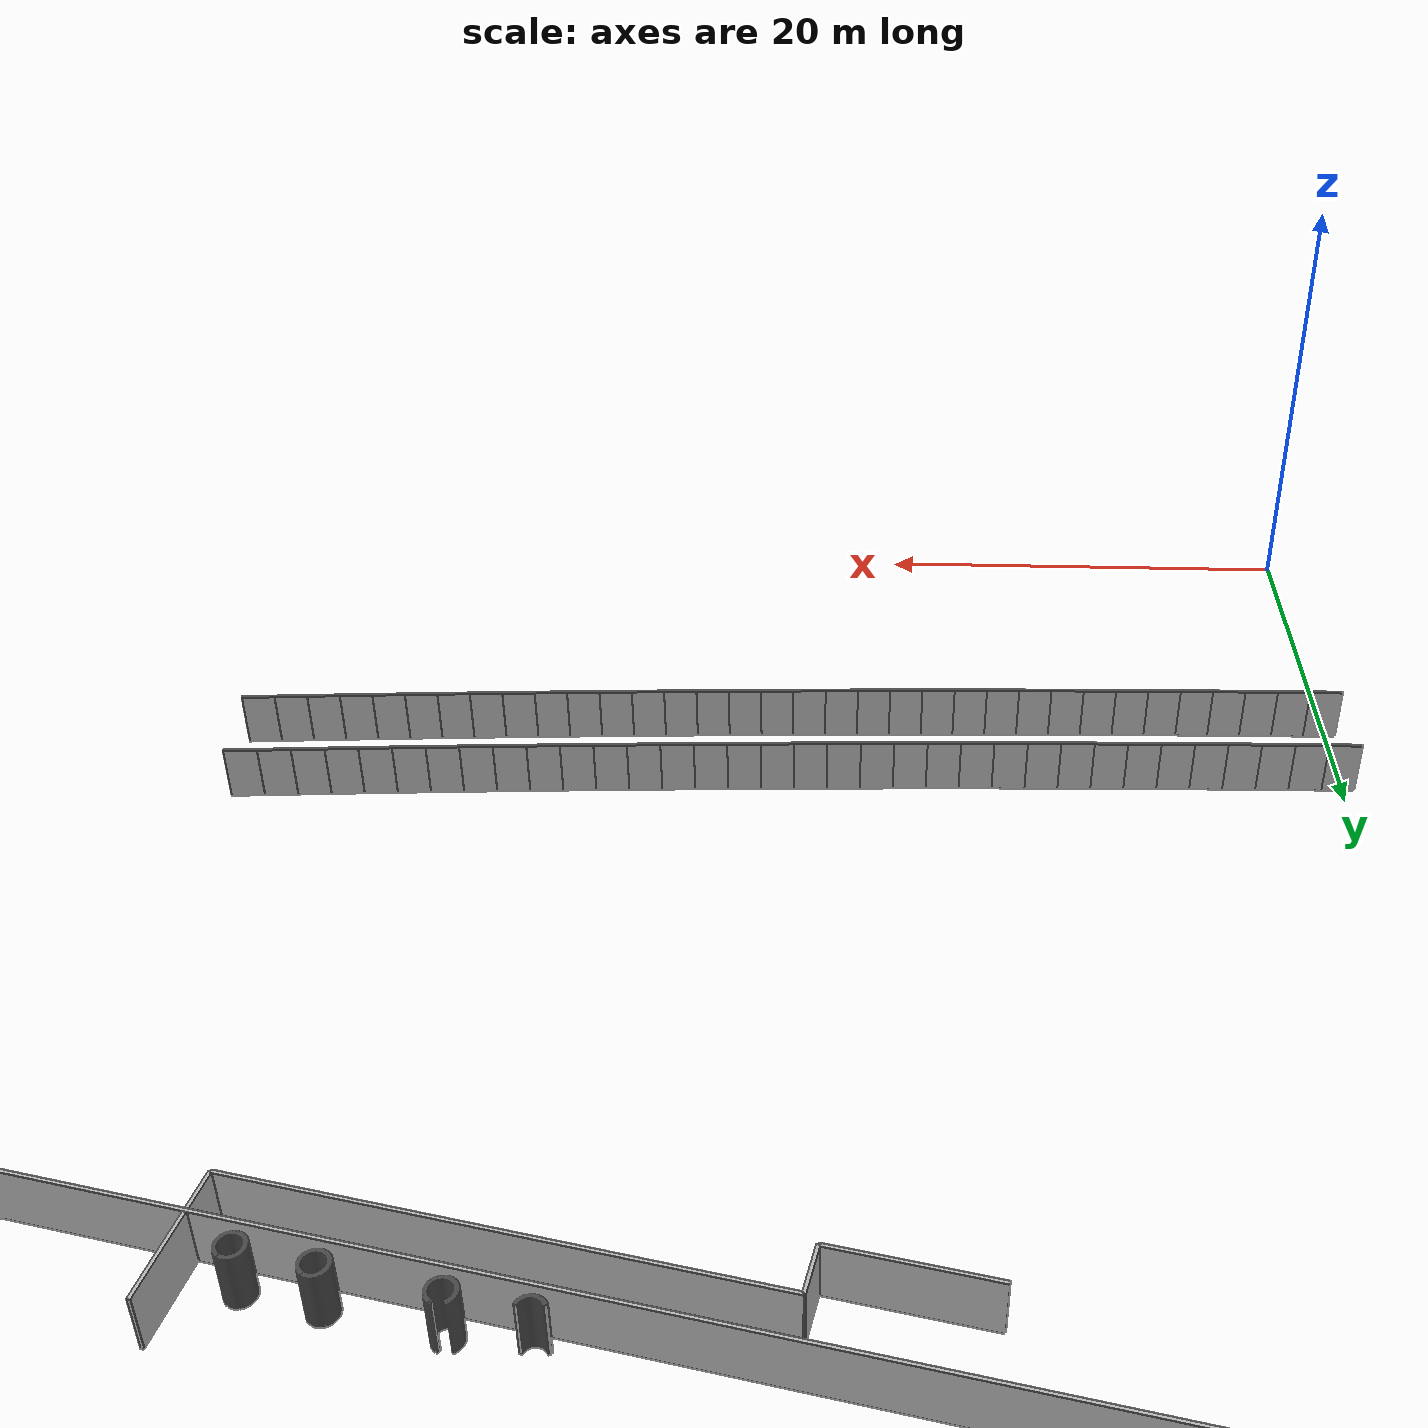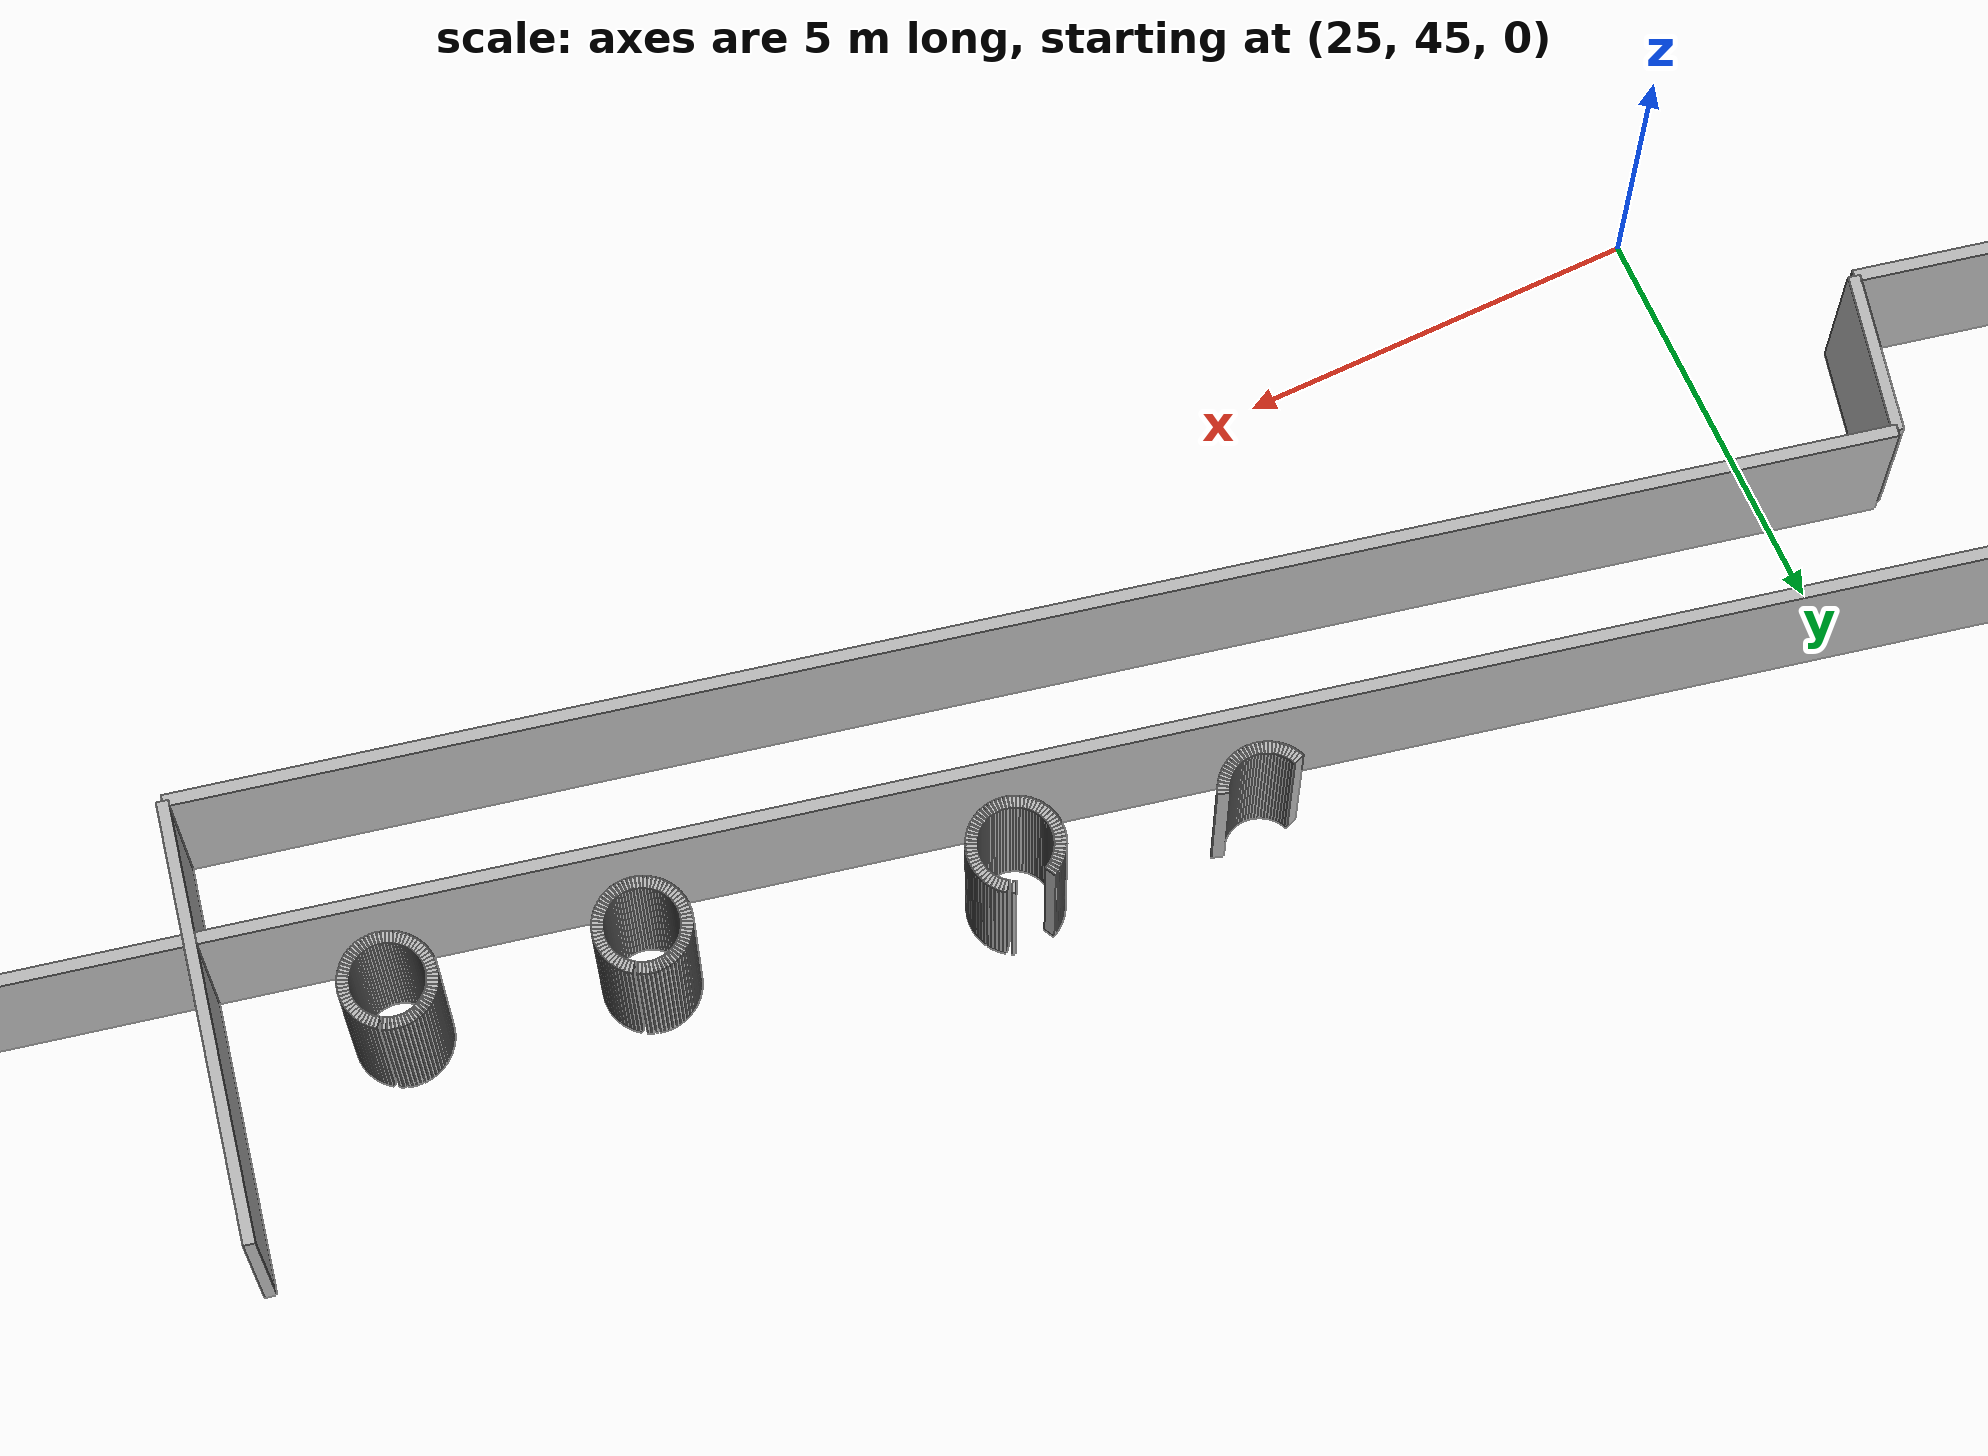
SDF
<?xml version="1.0" ?>
<sdf version="1.6">
  <model name="sps_2603">
    <pose frame="">0 0 0 0 -0 0</pose>
    <static>1</static>
    <self_collide>0</self_collide>
    <allow_auto_disable>0</allow_auto_disable>
    <link name="Wall696">
      <kinematic>0</kinematic>
      <gravity>1</gravity>
      <self_collide>0</self_collide>
      <collision name="collision">
        <geometry>
          <box>
            <size>0.0454008 0.15 2.5</size>
          </box>
        </geometry>
        <pose frame="">0 0 0 0 -0 0</pose>
      </collision>
      <visual name="visual">
        <geometry>
          <box>
            <size>0.0454008 0.15 2.5</size>
          </box>
        </geometry>
        <pose frame="">0 0 0 0 -0 0</pose>
        <cast_shadows>1</cast_shadows>
        <transparency>0.0</transparency>
      </visual>
      <pose frame="">42.9055 48.3673 1.25 0 0 -0.654794</pose>
    </link>
    <link name="Wall697">
      <kinematic>0</kinematic>
      <gravity>1</gravity>
      <self_collide>0</self_collide>
      <collision name="collision">
        <geometry>
          <box>
            <size>0.0452735 0.15 2.5</size>
          </box>
        </geometry>
        <pose frame="">0 0 0 0 -0 0</pose>
      </collision>
      <visual name="visual">
        <geometry>
          <box>
            <size>0.0452735 0.15 2.5</size>
          </box>
        </geometry>
        <pose frame="">0 0 0 0 -0 0</pose>
        <cast_shadows>1</cast_shadows>
        <transparency>0.0</transparency>
      </visual>
      <pose frame="">42.9402 48.3382 1.25 0 0 -0.741533</pose>
    </link>
    <link name="Wall698">
      <kinematic>0</kinematic>
      <gravity>1</gravity>
      <self_collide>0</self_collide>
      <collision name="collision">
        <geometry>
          <box>
            <size>0.0454087 0.15 2.5</size>
          </box>
        </geometry>
        <pose frame="">0 0 0 0 -0 0</pose>
      </collision>
      <visual name="visual">
        <geometry>
          <box>
            <size>0.0454087 0.15 2.5</size>
          </box>
        </geometry>
        <pose frame="">0 0 0 0 -0 0</pose>
        <cast_shadows>1</cast_shadows>
        <transparency>0.0</transparency>
      </visual>
      <pose frame="">42.9722 48.3061 1.25 0 0 -0.831987</pose>
    </link>
    <link name="Wall699">
      <kinematic>0</kinematic>
      <gravity>1</gravity>
      <self_collide>0</self_collide>
      <collision name="collision">
        <geometry>
          <box>
            <size>0.0453637 0.15 2.5</size>
          </box>
        </geometry>
        <pose frame="">0 0 0 0 -0 0</pose>
      </collision>
      <visual name="visual">
        <geometry>
          <box>
            <size>0.0453637 0.15 2.5</size>
          </box>
        </geometry>
        <pose frame="">0 0 0 0 -0 0</pose>
        <cast_shadows>1</cast_shadows>
        <transparency>0.0</transparency>
      </visual>
      <pose frame="">43.0012 48.2713 1.25 0 0 -0.91707</pose>
    </link>
    <link name="Wall700">
      <kinematic>0</kinematic>
      <gravity>1</gravity>
      <self_collide>0</self_collide>
      <collision name="collision">
        <geometry>
          <box>
            <size>0.045342 0.15 2.5</size>
          </box>
        </geometry>
        <pose frame="">0 0 0 0 -0 0</pose>
      </collision>
      <visual name="visual">
        <geometry>
          <box>
            <size>0.045342 0.15 2.5</size>
          </box>
        </geometry>
        <pose frame="">0 0 0 0 -0 0</pose>
        <cast_shadows>1</cast_shadows>
        <transparency>0.0</transparency>
      </visual>
      <pose frame="">43.0272 48.2342 1.25 0 0 -1.00221</pose>
    </link>
    <link name="Wall701">
      <kinematic>0</kinematic>
      <gravity>1</gravity>
      <self_collide>0</self_collide>
      <collision name="collision">
        <geometry>
          <box>
            <size>0.0453724 0.15 2.5</size>
          </box>
        </geometry>
        <pose frame="">0 0 0 0 -0 0</pose>
      </collision>
      <visual name="visual">
        <geometry>
          <box>
            <size>0.0453724 0.15 2.5</size>
          </box>
        </geometry>
        <pose frame="">0 0 0 0 -0 0</pose>
        <cast_shadows>1</cast_shadows>
        <transparency>0.0</transparency>
      </visual>
      <pose frame="">43.0499 48.195 1.25 0 0 -1.0897</pose>
    </link>
    <link name="Wall702">
      <kinematic>0</kinematic>
      <gravity>1</gravity>
      <self_collide>0</self_collide>
      <collision name="collision">
        <geometry>
          <box>
            <size>0.0453827 0.15 2.5</size>
          </box>
        </geometry>
        <pose frame="">0 0 0 0 -0 0</pose>
      </collision>
      <visual name="visual">
        <geometry>
          <box>
            <size>0.0453827 0.15 2.5</size>
          </box>
        </geometry>
        <pose frame="">0 0 0 0 -0 0</pose>
        <cast_shadows>1</cast_shadows>
        <transparency>0.0</transparency>
      </visual>
      <pose frame="">43.0691 48.1539 1.25 0 0 -1.1818</pose>
    </link>
    <link name="Wall703">
      <kinematic>0</kinematic>
      <gravity>1</gravity>
      <self_collide>0</self_collide>
      <collision name="collision">
        <geometry>
          <box>
            <size>0.0453611 0.15 2.5</size>
          </box>
        </geometry>
        <pose frame="">0 0 0 0 -0 0</pose>
      </collision>
      <visual name="visual">
        <geometry>
          <box>
            <size>0.0453611 0.15 2.5</size>
          </box>
        </geometry>
        <pose frame="">0 0 0 0 -0 0</pose>
        <cast_shadows>1</cast_shadows>
        <transparency>0.0</transparency>
      </visual>
      <pose frame="">43.0846 48.1113 1.25 0 0 -1.26181</pose>
    </link>
    <link name="Wall704">
      <kinematic>0</kinematic>
      <gravity>1</gravity>
      <self_collide>0</self_collide>
      <collision name="collision">
        <geometry>
          <box>
            <size>0.0452165 0.15 2.5</size>
          </box>
        </geometry>
        <pose frame="">0 0 0 0 -0 0</pose>
      </collision>
      <visual name="visual">
        <geometry>
          <box>
            <size>0.0452165 0.15 2.5</size>
          </box>
        </geometry>
        <pose frame="">0 0 0 0 -0 0</pose>
        <cast_shadows>1</cast_shadows>
        <transparency>0.0</transparency>
      </visual>
      <pose frame="">43.0962 48.0676 1.25 0 0 -1.35725</pose>
    </link>
    <link name="Wall705">
      <kinematic>0</kinematic>
      <gravity>1</gravity>
      <self_collide>0</self_collide>
      <collision name="collision">
        <geometry>
          <box>
            <size>0.0453869 0.15 2.5</size>
          </box>
        </geometry>
        <pose frame="">0 0 0 0 -0 0</pose>
      </collision>
      <visual name="visual">
        <geometry>
          <box>
            <size>0.0453869 0.15 2.5</size>
          </box>
        </geometry>
        <pose frame="">0 0 0 0 -0 0</pose>
        <cast_shadows>1</cast_shadows>
        <transparency>0.0</transparency>
      </visual>
      <pose frame="">43.1041 48.023 1.25 0 0 -1.43727</pose>
    </link>
    <link name="Wall706">
      <kinematic>0</kinematic>
      <gravity>1</gravity>
      <self_collide>0</self_collide>
      <collision name="collision">
        <geometry>
          <box>
            <size>0.0454521 0.15 2.5</size>
          </box>
        </geometry>
        <pose frame="">0 0 0 0 -0 0</pose>
      </collision>
      <visual name="visual">
        <geometry>
          <box>
            <size>0.0454521 0.15 2.5</size>
          </box>
        </geometry>
        <pose frame="">0 0 0 0 -0 0</pose>
        <cast_shadows>1</cast_shadows>
        <transparency>0.0</transparency>
      </visual>
      <pose frame="">43.1081 47.9778 1.25 0 0 -1.52781</pose>
    </link>
    <link name="Wall707">
      <kinematic>0</kinematic>
      <gravity>1</gravity>
      <self_collide>0</self_collide>
      <collision name="collision">
        <geometry>
          <box>
            <size>0.0452692 0.15 2.5</size>
          </box>
        </geometry>
        <pose frame="">0 0 0 0 -0 0</pose>
      </collision>
      <visual name="visual">
        <geometry>
          <box>
            <size>0.0452692 0.15 2.5</size>
          </box>
        </geometry>
        <pose frame="">0 0 0 0 -0 0</pose>
        <cast_shadows>1</cast_shadows>
        <transparency>0.0</transparency>
      </visual>
      <pose frame="">43.1081 47.9325 1.25 0 0 -1.61395</pose>
    </link>
    <link name="Wall708">
      <kinematic>0</kinematic>
      <gravity>1</gravity>
      <self_collide>0</self_collide>
      <collision name="collision">
        <geometry>
          <box>
            <size>0.0453869 0.15 2.5</size>
          </box>
        </geometry>
        <pose frame="">0 0 0 0 -0 0</pose>
      </collision>
      <visual name="visual">
        <geometry>
          <box>
            <size>0.0453869 0.15 2.5</size>
          </box>
        </geometry>
        <pose frame="">0 0 0 0 -0 0</pose>
        <cast_shadows>1</cast_shadows>
        <transparency>0.0</transparency>
      </visual>
      <pose frame="">43.1041 47.8874 1.25 0 0 -1.70433</pose>
    </link>
    <link name="Wall709">
      <kinematic>0</kinematic>
      <gravity>1</gravity>
      <self_collide>0</self_collide>
      <collision name="collision">
        <geometry>
          <box>
            <size>0.0454345 0.15 2.5</size>
          </box>
        </geometry>
        <pose frame="">0 0 0 0 -0 0</pose>
      </collision>
      <visual name="visual">
        <geometry>
          <box>
            <size>0.0454345 0.15 2.5</size>
          </box>
        </geometry>
        <pose frame="">0 0 0 0 -0 0</pose>
        <cast_shadows>1</cast_shadows>
        <transparency>0.0</transparency>
      </visual>
      <pose frame="">43.0962 47.8427 1.25 0 0 -1.78743</pose>
    </link>
    <link name="Wall710">
      <kinematic>0</kinematic>
      <gravity>1</gravity>
      <self_collide>0</self_collide>
      <collision name="collision">
        <geometry>
          <box>
            <size>0.0453057 0.15 2.5</size>
          </box>
        </geometry>
        <pose frame="">0 0 0 0 -0 0</pose>
      </collision>
      <visual name="visual">
        <geometry>
          <box>
            <size>0.0453057 0.15 2.5</size>
          </box>
        </geometry>
        <pose frame="">0 0 0 0 -0 0</pose>
        <cast_shadows>1</cast_shadows>
        <transparency>0.0</transparency>
      </visual>
      <pose frame="">43.0845 47.7989 1.25 0 0 -1.87593</pose>
    </link>
    <link name="Wall711">
      <kinematic>0</kinematic>
      <gravity>1</gravity>
      <self_collide>0</self_collide>
      <collision name="collision">
        <geometry>
          <box>
            <size>0.0454525 0.15 2.5</size>
          </box>
        </geometry>
        <pose frame="">0 0 0 0 -0 0</pose>
      </collision>
      <visual name="visual">
        <geometry>
          <box>
            <size>0.0454525 0.15 2.5</size>
          </box>
        </geometry>
        <pose frame="">0 0 0 0 -0 0</pose>
        <cast_shadows>1</cast_shadows>
        <transparency>0.0</transparency>
      </visual>
      <pose frame="">43.069 47.7563 1.25 0 0 -1.96352</pose>
    </link>
    <link name="Wall712">
      <kinematic>0</kinematic>
      <gravity>1</gravity>
      <self_collide>0</self_collide>
      <collision name="collision">
        <geometry>
          <box>
            <size>0.0453724 0.15 2.5</size>
          </box>
        </geometry>
        <pose frame="">0 0 0 0 -0 0</pose>
      </collision>
      <visual name="visual">
        <geometry>
          <box>
            <size>0.0453724 0.15 2.5</size>
          </box>
        </geometry>
        <pose frame="">0 0 0 0 -0 0</pose>
        <cast_shadows>1</cast_shadows>
        <transparency>0.0</transparency>
      </visual>
      <pose frame="">43.0498 47.7152 1.25 0 0 -2.05189</pose>
    </link>
    <link name="Wall713">
      <kinematic>0</kinematic>
      <gravity>1</gravity>
      <self_collide>0</self_collide>
      <collision name="collision">
        <geometry>
          <box>
            <size>0.045342 0.15 2.5</size>
          </box>
        </geometry>
        <pose frame="">0 0 0 0 -0 0</pose>
      </collision>
      <visual name="visual">
        <geometry>
          <box>
            <size>0.045342 0.15 2.5</size>
          </box>
        </geometry>
        <pose frame="">0 0 0 0 -0 0</pose>
        <cast_shadows>1</cast_shadows>
        <transparency>0.0</transparency>
      </visual>
      <pose frame="">43.0271 47.676 1.25 0 0 -2.13938</pose>
    </link>
    <link name="Wall714">
      <kinematic>0</kinematic>
      <gravity>1</gravity>
      <self_collide>0</self_collide>
      <collision name="collision">
        <geometry>
          <box>
            <size>0.0453637 0.15 2.5</size>
          </box>
        </geometry>
        <pose frame="">0 0 0 0 -0 0</pose>
      </collision>
      <visual name="visual">
        <geometry>
          <box>
            <size>0.0453637 0.15 2.5</size>
          </box>
        </geometry>
        <pose frame="">0 0 0 0 -0 0</pose>
        <cast_shadows>1</cast_shadows>
        <transparency>0.0</transparency>
      </visual>
      <pose frame="">43.0011 47.6389 1.25 0 0 -2.22452</pose>
    </link>
    <link name="Wall715">
      <kinematic>0</kinematic>
      <gravity>1</gravity>
      <self_collide>0</self_collide>
      <collision name="collision">
        <geometry>
          <box>
            <size>0.0453148 0.15 2.5</size>
          </box>
        </geometry>
        <pose frame="">0 0 0 0 -0 0</pose>
      </collision>
      <visual name="visual">
        <geometry>
          <box>
            <size>0.0453148 0.15 2.5</size>
          </box>
        </geometry>
        <pose frame="">0 0 0 0 -0 0</pose>
        <cast_shadows>1</cast_shadows>
        <transparency>0.0</transparency>
      </visual>
      <pose frame="">42.9719 47.6042 1.25 0 0 -2.31332</pose>
    </link>
    <link name="Wall716">
      <kinematic>0</kinematic>
      <gravity>1</gravity>
      <self_collide>0</self_collide>
      <collision name="collision">
        <geometry>
          <box>
            <size>0.0453974 0.15 2.5</size>
          </box>
        </geometry>
        <pose frame="">0 0 0 0 -0 0</pose>
      </collision>
      <visual name="visual">
        <geometry>
          <box>
            <size>0.0453974 0.15 2.5</size>
          </box>
        </geometry>
        <pose frame="">0 0 0 0 -0 0</pose>
        <cast_shadows>1</cast_shadows>
        <transparency>0.0</transparency>
      </visual>
      <pose frame="">42.9399 47.5721 1.25 0 0 -2.39709</pose>
    </link>
    <link name="Wall717">
      <kinematic>0</kinematic>
      <gravity>1</gravity>
      <self_collide>0</self_collide>
      <collision name="collision">
        <geometry>
          <box>
            <size>0.0454008 0.15 2.5</size>
          </box>
        </geometry>
        <pose frame="">0 0 0 0 -0 0</pose>
      </collision>
      <visual name="visual">
        <geometry>
          <box>
            <size>0.0454008 0.15 2.5</size>
          </box>
        </geometry>
        <pose frame="">0 0 0 0 -0 0</pose>
        <cast_shadows>1</cast_shadows>
        <transparency>0.0</transparency>
      </visual>
      <pose frame="">42.9052 47.5429 1.25 0 0 -2.4868</pose>
    </link>
    <link name="Wall718">
      <kinematic>0</kinematic>
      <gravity>1</gravity>
      <self_collide>0</self_collide>
      <collision name="collision">
        <geometry>
          <box>
            <size>0.0453659 0.15 2.5</size>
          </box>
        </geometry>
        <pose frame="">0 0 0 0 -0 0</pose>
      </collision>
      <visual name="visual">
        <geometry>
          <box>
            <size>0.0453659 0.15 2.5</size>
          </box>
        </geometry>
        <pose frame="">0 0 0 0 -0 0</pose>
        <cast_shadows>1</cast_shadows>
        <transparency>0.0</transparency>
      </visual>
      <pose frame="">42.868 47.517 1.25 0 0 -2.57971</pose>
    </link>
    <link name="Wall719">
      <kinematic>0</kinematic>
      <gravity>1</gravity>
      <self_collide>0</self_collide>
      <collision name="collision">
        <geometry>
          <box>
            <size>0.0453183 0.15 2.5</size>
          </box>
        </geometry>
        <pose frame="">0 0 0 0 -0 0</pose>
      </collision>
      <visual name="visual">
        <geometry>
          <box>
            <size>0.0453183 0.15 2.5</size>
          </box>
        </geometry>
        <pose frame="">0 0 0 0 -0 0</pose>
        <cast_shadows>1</cast_shadows>
        <transparency>0.0</transparency>
      </visual>
      <pose frame="">42.8288 47.4944 1.25 0 0 -2.65987</pose>
    </link>
    <link name="Wall720">
      <kinematic>0</kinematic>
      <gravity>1</gravity>
      <self_collide>0</self_collide>
      <collision name="collision">
        <geometry>
          <box>
            <size>0.0454525 0.15 2.5</size>
          </box>
        </geometry>
        <pose frame="">0 0 0 0 -0 0</pose>
      </collision>
      <visual name="visual">
        <geometry>
          <box>
            <size>0.0454525 0.15 2.5</size>
          </box>
        </geometry>
        <pose frame="">0 0 0 0 -0 0</pose>
        <cast_shadows>1</cast_shadows>
        <transparency>0.0</transparency>
      </visual>
      <pose frame="">42.7877 47.4752 1.25 0 0 -2.74887</pose>
    </link>
    <link name="Wall721">
      <kinematic>0</kinematic>
      <gravity>1</gravity>
      <self_collide>0</self_collide>
      <collision name="collision">
        <geometry>
          <box>
            <size>0.0453057 0.15 2.5</size>
          </box>
        </geometry>
        <pose frame="">0 0 0 0 -0 0</pose>
      </collision>
      <visual name="visual">
        <geometry>
          <box>
            <size>0.0453057 0.15 2.5</size>
          </box>
        </geometry>
        <pose frame="">0 0 0 0 -0 0</pose>
        <cast_shadows>1</cast_shadows>
        <transparency>0.0</transparency>
      </visual>
      <pose frame="">42.7451 47.4597 1.25 0 0 -2.83646</pose>
    </link>
    <link name="Wall722">
      <kinematic>0</kinematic>
      <gravity>1</gravity>
      <self_collide>0</self_collide>
      <collision name="collision">
        <geometry>
          <box>
            <size>0.0452689 0.15 2.5</size>
          </box>
        </geometry>
        <pose frame="">0 0 0 0 -0 0</pose>
      </collision>
      <visual name="visual">
        <geometry>
          <box>
            <size>0.0452689 0.15 2.5</size>
          </box>
        </geometry>
        <pose frame="">0 0 0 0 -0 0</pose>
        <cast_shadows>1</cast_shadows>
        <transparency>0.0</transparency>
      </visual>
      <pose frame="">42.7014 47.448 1.25 0 0 -2.92278</pose>
    </link>
    <link name="Wall723">
      <kinematic>0</kinematic>
      <gravity>1</gravity>
      <self_collide>0</self_collide>
      <collision name="collision">
        <geometry>
          <box>
            <size>0.0454156 0.15 2.5</size>
          </box>
        </geometry>
        <pose frame="">0 0 0 0 -0 0</pose>
      </collision>
      <visual name="visual">
        <geometry>
          <box>
            <size>0.0454156 0.15 2.5</size>
          </box>
        </geometry>
        <pose frame="">0 0 0 0 -0 0</pose>
        <cast_shadows>1</cast_shadows>
        <transparency>0.0</transparency>
      </visual>
      <pose frame="">42.6568 47.4402 1.25 0 0 -3.01357</pose>
    </link>
    <link name="Wall724">
      <kinematic>0</kinematic>
      <gravity>1</gravity>
      <self_collide>0</self_collide>
      <collision name="collision">
        <geometry>
          <box>
            <size>0.0454521 0.15 2.5</size>
          </box>
        </geometry>
        <pose frame="">0 0 0 0 -0 0</pose>
      </collision>
      <visual name="visual">
        <geometry>
          <box>
            <size>0.0454521 0.15 2.5</size>
          </box>
        </geometry>
        <pose frame="">0 0 0 0 -0 0</pose>
        <cast_shadows>1</cast_shadows>
        <transparency>0.0</transparency>
      </visual>
      <pose frame="">42.6115 47.4363 1.25 0 0 -3.09861</pose>
    </link>
    <link name="Wall725">
      <kinematic>0</kinematic>
      <gravity>1</gravity>
      <self_collide>0</self_collide>
      <collision name="collision">
        <geometry>
          <box>
            <size>0.0452082 0.15 2.5</size>
          </box>
        </geometry>
        <pose frame="">0 0 0 0 -0 0</pose>
      </collision>
      <visual name="visual">
        <geometry>
          <box>
            <size>0.0452082 0.15 2.5</size>
          </box>
        </geometry>
        <pose frame="">0 0 0 0 -0 0</pose>
        <cast_shadows>1</cast_shadows>
        <transparency>0.0</transparency>
      </visual>
      <pose frame="">42.5662 47.4363 1.25 0 -0 3.09838</pose>
    </link>
    <link name="Wall726">
      <kinematic>0</kinematic>
      <gravity>1</gravity>
      <self_collide>0</self_collide>
      <collision name="collision">
        <geometry>
          <box>
            <size>0.0453551 0.15 2.5</size>
          </box>
        </geometry>
        <pose frame="">0 0 0 0 -0 0</pose>
      </collision>
      <visual name="visual">
        <geometry>
          <box>
            <size>0.0453551 0.15 2.5</size>
          </box>
        </geometry>
        <pose frame="">0 0 0 0 -0 0</pose>
        <cast_shadows>1</cast_shadows>
        <transparency>0.0</transparency>
      </visual>
      <pose frame="">42.5212 47.4402 1.25 0 -0 3.0134</pose>
    </link>
    <link name="Wall727">
      <kinematic>0</kinematic>
      <gravity>1</gravity>
      <self_collide>0</self_collide>
      <collision name="collision">
        <geometry>
          <box>
            <size>0.0455471 0.15 2.5</size>
          </box>
        </geometry>
        <pose frame="">0 0 0 0 -0 0</pose>
      </collision>
      <visual name="visual">
        <geometry>
          <box>
            <size>0.0455471 0.15 2.5</size>
          </box>
        </geometry>
        <pose frame="">0 0 0 0 -0 0</pose>
        <cast_shadows>1</cast_shadows>
        <transparency>0.0</transparency>
      </visual>
      <pose frame="">42.4765 47.4481 1.25 0 -0 2.92002</pose>
    </link>
    <link name="Wall728">
      <kinematic>0</kinematic>
      <gravity>1</gravity>
      <self_collide>0</self_collide>
      <collision name="collision">
        <geometry>
          <box>
            <size>0.0453057 0.15 2.5</size>
          </box>
        </geometry>
        <pose frame="">0 0 0 0 -0 0</pose>
      </collision>
      <visual name="visual">
        <geometry>
          <box>
            <size>0.0453057 0.15 2.5</size>
          </box>
        </geometry>
        <pose frame="">0 0 0 0 -0 0</pose>
        <cast_shadows>1</cast_shadows>
        <transparency>0.0</transparency>
      </visual>
      <pose frame="">42.4326 47.4599 1.25 0 -0 2.83646</pose>
    </link>
    <link name="Wall729">
      <kinematic>0</kinematic>
      <gravity>1</gravity>
      <self_collide>0</self_collide>
      <collision name="collision">
        <geometry>
          <box>
            <size>0.0454525 0.15 2.5</size>
          </box>
        </geometry>
        <pose frame="">0 0 0 0 -0 0</pose>
      </collision>
      <visual name="visual">
        <geometry>
          <box>
            <size>0.0454525 0.15 2.5</size>
          </box>
        </geometry>
        <pose frame="">0 0 0 0 -0 0</pose>
        <cast_shadows>1</cast_shadows>
        <transparency>0.0</transparency>
      </visual>
      <pose frame="">42.39 47.4754 1.25 0 -0 2.74887</pose>
    </link>
    <link name="Wall730">
      <kinematic>0</kinematic>
      <gravity>1</gravity>
      <self_collide>0</self_collide>
      <collision name="collision">
        <geometry>
          <box>
            <size>0.0452338 0.15 2.5</size>
          </box>
        </geometry>
        <pose frame="">0 0 0 0 -0 0</pose>
      </collision>
      <visual name="visual">
        <geometry>
          <box>
            <size>0.0452338 0.15 2.5</size>
          </box>
        </geometry>
        <pose frame="">0 0 0 0 -0 0</pose>
        <cast_shadows>1</cast_shadows>
        <transparency>0.0</transparency>
      </visual>
      <pose frame="">42.349 47.4945 1.25 0 -0 2.66346</pose>
    </link>
    <link name="Wall731">
      <kinematic>0</kinematic>
      <gravity>1</gravity>
      <self_collide>0</self_collide>
      <collision name="collision">
        <geometry>
          <box>
            <size>0.045342 0.15 2.5</size>
          </box>
        </geometry>
        <pose frame="">0 0 0 0 -0 0</pose>
      </collision>
      <visual name="visual">
        <geometry>
          <box>
            <size>0.045342 0.15 2.5</size>
          </box>
        </geometry>
        <pose frame="">0 0 0 0 -0 0</pose>
        <cast_shadows>1</cast_shadows>
        <transparency>0.0</transparency>
      </visual>
      <pose frame="">42.3098 47.5171 1.25 0 -0 2.57301</pose>
    </link>
    <link name="Wall732">
      <kinematic>0</kinematic>
      <gravity>1</gravity>
      <self_collide>0</self_collide>
      <collision name="collision">
        <geometry>
          <box>
            <size>0.0454753 0.15 2.5</size>
          </box>
        </geometry>
        <pose frame="">0 0 0 0 -0 0</pose>
      </collision>
      <visual name="visual">
        <geometry>
          <box>
            <size>0.0454753 0.15 2.5</size>
          </box>
        </geometry>
        <pose frame="">0 0 0 0 -0 0</pose>
        <cast_shadows>1</cast_shadows>
        <transparency>0.0</transparency>
      </visual>
      <pose frame="">42.2727 47.5432 1.25 0 -0 2.48467</pose>
    </link>
    <link name="Wall733">
      <kinematic>0</kinematic>
      <gravity>1</gravity>
      <self_collide>0</self_collide>
      <collision name="collision">
        <geometry>
          <box>
            <size>0.0453148 0.15 2.5</size>
          </box>
        </geometry>
        <pose frame="">0 0 0 0 -0 0</pose>
      </collision>
      <visual name="visual">
        <geometry>
          <box>
            <size>0.0453148 0.15 2.5</size>
          </box>
        </geometry>
        <pose frame="">0 0 0 0 -0 0</pose>
        <cast_shadows>1</cast_shadows>
        <transparency>0.0</transparency>
      </visual>
      <pose frame="">42.238 47.5724 1.25 0 -0 2.39907</pose>
    </link>
    <link name="Wall734">
      <kinematic>0</kinematic>
      <gravity>1</gravity>
      <self_collide>0</self_collide>
      <collision name="collision">
        <geometry>
          <box>
            <size>0.0453148 0.15 2.5</size>
          </box>
        </geometry>
        <pose frame="">0 0 0 0 -0 0</pose>
      </collision>
      <visual name="visual">
        <geometry>
          <box>
            <size>0.0453148 0.15 2.5</size>
          </box>
        </geometry>
        <pose frame="">0 0 0 0 -0 0</pose>
        <cast_shadows>1</cast_shadows>
        <transparency>0.0</transparency>
      </visual>
      <pose frame="">42.206 47.6044 1.25 0 -0 2.31332</pose>
    </link>
    <link name="Wall735">
      <kinematic>0</kinematic>
      <gravity>1</gravity>
      <self_collide>0</self_collide>
      <collision name="collision">
        <geometry>
          <box>
            <size>0.0453637 0.15 2.5</size>
          </box>
        </geometry>
        <pose frame="">0 0 0 0 -0 0</pose>
      </collision>
      <visual name="visual">
        <geometry>
          <box>
            <size>0.0453637 0.15 2.5</size>
          </box>
        </geometry>
        <pose frame="">0 0 0 0 -0 0</pose>
        <cast_shadows>1</cast_shadows>
        <transparency>0.0</transparency>
      </visual>
      <pose frame="">42.1768 47.6391 1.25 0 -0 2.22452</pose>
    </link>
    <link name="Wall736">
      <kinematic>0</kinematic>
      <gravity>1</gravity>
      <self_collide>0</self_collide>
      <collision name="collision">
        <geometry>
          <box>
            <size>0.0452906 0.15 2.5</size>
          </box>
        </geometry>
        <pose frame="">0 0 0 0 -0 0</pose>
      </collision>
      <visual name="visual">
        <geometry>
          <box>
            <size>0.0452906 0.15 2.5</size>
          </box>
        </geometry>
        <pose frame="">0 0 0 0 -0 0</pose>
        <cast_shadows>1</cast_shadows>
        <transparency>0.0</transparency>
      </visual>
      <pose frame="">42.1508 47.6762 1.25 0 -0 2.14011</pose>
    </link>
    <link name="Wall737">
      <kinematic>0</kinematic>
      <gravity>1</gravity>
      <self_collide>0</self_collide>
      <collision name="collision">
        <geometry>
          <box>
            <size>0.0455348 0.15 2.5</size>
          </box>
        </geometry>
        <pose frame="">0 0 0 0 -0 0</pose>
      </collision>
      <visual name="visual">
        <geometry>
          <box>
            <size>0.0455348 0.15 2.5</size>
          </box>
        </geometry>
        <pose frame="">0 0 0 0 -0 0</pose>
        <cast_shadows>1</cast_shadows>
        <transparency>0.0</transparency>
      </visual>
      <pose frame="">42.1281 47.7155 1.25 0 -0 2.05003</pose>
    </link>
    <link name="Wall738">
      <kinematic>0</kinematic>
      <gravity>1</gravity>
      <self_collide>0</self_collide>
      <collision name="collision">
        <geometry>
          <box>
            <size>0.0452834 0.15 2.5</size>
          </box>
        </geometry>
        <pose frame="">0 0 0 0 -0 0</pose>
      </collision>
      <visual name="visual">
        <geometry>
          <box>
            <size>0.0452834 0.15 2.5</size>
          </box>
        </geometry>
        <pose frame="">0 0 0 0 -0 0</pose>
        <cast_shadows>1</cast_shadows>
        <transparency>0.0</transparency>
      </visual>
      <pose frame="">42.1089 47.7566 1.25 0 -0 1.96507</pose>
    </link>
    <link name="Wall739">
      <kinematic>0</kinematic>
      <gravity>1</gravity>
      <self_collide>0</self_collide>
      <collision name="collision">
        <geometry>
          <box>
            <size>0.0454804 0.15 2.5</size>
          </box>
        </geometry>
        <pose frame="">0 0 0 0 -0 0</pose>
      </collision>
      <visual name="visual">
        <geometry>
          <box>
            <size>0.0454804 0.15 2.5</size>
          </box>
        </geometry>
        <pose frame="">0 0 0 0 -0 0</pose>
        <cast_shadows>1</cast_shadows>
        <transparency>0.0</transparency>
      </visual>
      <pose frame="">42.0934 47.7992 1.25 0 -0 1.87472</pose>
    </link>
    <link name="Wall740">
      <kinematic>0</kinematic>
      <gravity>1</gravity>
      <self_collide>0</self_collide>
      <collision name="collision">
        <geometry>
          <box>
            <size>0.0452557 0.15 2.5</size>
          </box>
        </geometry>
        <pose frame="">0 0 0 0 -0 0</pose>
      </collision>
      <visual name="visual">
        <geometry>
          <box>
            <size>0.0452557 0.15 2.5</size>
          </box>
        </geometry>
        <pose frame="">0 0 0 0 -0 0</pose>
        <cast_shadows>1</cast_shadows>
        <transparency>0.0</transparency>
      </visual>
      <pose frame="">42.0817 47.843 1.25 0 -0 1.78829</pose>
    </link>
    <link name="Wall741">
      <kinematic>0</kinematic>
      <gravity>1</gravity>
      <self_collide>0</self_collide>
      <collision name="collision">
        <geometry>
          <box>
            <size>0.0454156 0.15 2.5</size>
          </box>
        </geometry>
        <pose frame="">0 0 0 0 -0 0</pose>
      </collision>
      <visual name="visual">
        <geometry>
          <box>
            <size>0.0454156 0.15 2.5</size>
          </box>
        </geometry>
        <pose frame="">0 0 0 0 -0 0</pose>
        <cast_shadows>1</cast_shadows>
        <transparency>0.0</transparency>
      </visual>
      <pose frame="">42.074 47.8876 1.25 0 -0 1.69882</pose>
    </link>
    <link name="Wall742">
      <kinematic>0</kinematic>
      <gravity>1</gravity>
      <self_collide>0</self_collide>
      <collision name="collision">
        <geometry>
          <box>
            <size>0.0452109 0.15 2.5</size>
          </box>
        </geometry>
        <pose frame="">0 0 0 0 -0 0</pose>
      </collision>
      <visual name="visual">
        <geometry>
          <box>
            <size>0.0452109 0.15 2.5</size>
          </box>
        </geometry>
        <pose frame="">0 0 0 0 -0 0</pose>
        <cast_shadows>1</cast_shadows>
        <transparency>0.0</transparency>
      </visual>
      <pose frame="">42.0701 47.9327 1.25 0 -0 1.61536</pose>
    </link>
    <link name="Wall743">
      <kinematic>0</kinematic>
      <gravity>1</gravity>
      <self_collide>0</self_collide>
      <collision name="collision">
        <geometry>
          <box>
            <size>0.0454548 0.15 2.5</size>
          </box>
        </geometry>
        <pose frame="">0 0 0 0 -0 0</pose>
      </collision>
      <visual name="visual">
        <geometry>
          <box>
            <size>0.0454548 0.15 2.5</size>
          </box>
        </geometry>
        <pose frame="">0 0 0 0 -0 0</pose>
        <cast_shadows>1</cast_shadows>
        <transparency>0.0</transparency>
      </visual>
      <pose frame="">42.0701 47.978 1.25 0 -0 1.52647</pose>
    </link>
    <link name="Wall744">
      <kinematic>0</kinematic>
      <gravity>1</gravity>
      <self_collide>0</self_collide>
      <collision name="collision">
        <geometry>
          <box>
            <size>0.0453788 0.15 2.5</size>
          </box>
        </geometry>
        <pose frame="">0 0 0 0 -0 0</pose>
      </collision>
      <visual name="visual">
        <geometry>
          <box>
            <size>0.0453788 0.15 2.5</size>
          </box>
        </geometry>
        <pose frame="">0 0 0 0 -0 0</pose>
        <cast_shadows>1</cast_shadows>
        <transparency>0.0</transparency>
      </visual>
      <pose frame="">42.0741 48.0232 1.25 0 -0 1.4386</pose>
    </link>
    <link name="Wall745">
      <kinematic>0</kinematic>
      <gravity>1</gravity>
      <self_collide>0</self_collide>
      <collision name="collision">
        <geometry>
          <box>
            <size>0.0453285 0.15 2.5</size>
          </box>
        </geometry>
        <pose frame="">0 0 0 0 -0 0</pose>
      </collision>
      <visual name="visual">
        <geometry>
          <box>
            <size>0.0453285 0.15 2.5</size>
          </box>
        </geometry>
        <pose frame="">0 0 0 0 -0 0</pose>
        <cast_shadows>1</cast_shadows>
        <transparency>0.0</transparency>
      </visual>
      <pose frame="">42.082 48.0678 1.25 0 -0 1.35227</pose>
    </link>
    <link name="Wall746">
      <kinematic>0</kinematic>
      <gravity>1</gravity>
      <self_collide>0</self_collide>
      <collision name="collision">
        <geometry>
          <box>
            <size>0.0454804 0.15 2.5</size>
          </box>
        </geometry>
        <pose frame="">0 0 0 0 -0 0</pose>
      </collision>
      <visual name="visual">
        <geometry>
          <box>
            <size>0.0454804 0.15 2.5</size>
          </box>
        </geometry>
        <pose frame="">0 0 0 0 -0 0</pose>
        <cast_shadows>1</cast_shadows>
        <transparency>0.0</transparency>
      </visual>
      <pose frame="">42.0937 48.1116 1.25 0 -0 1.26687</pose>
    </link>
    <link name="Wall747">
      <kinematic>0</kinematic>
      <gravity>1</gravity>
      <self_collide>0</self_collide>
      <collision name="collision">
        <geometry>
          <box>
            <size>0.0452271 0.15 2.5</size>
          </box>
        </geometry>
        <pose frame="">0 0 0 0 -0 0</pose>
      </collision>
      <visual name="visual">
        <geometry>
          <box>
            <size>0.0452271 0.15 2.5</size>
          </box>
        </geometry>
        <pose frame="">0 0 0 0 -0 0</pose>
        <cast_shadows>1</cast_shadows>
        <transparency>0.0</transparency>
      </visual>
      <pose frame="">42.1092 48.1542 1.25 0 -0 1.17601</pose>
    </link>
    <link name="Wall748">
      <kinematic>0</kinematic>
      <gravity>1</gravity>
      <self_collide>0</self_collide>
      <collision name="collision">
        <geometry>
          <box>
            <size>0.0454228 0.15 2.5</size>
          </box>
        </geometry>
        <pose frame="">0 0 0 0 -0 0</pose>
      </collision>
      <visual name="visual">
        <geometry>
          <box>
            <size>0.0454228 0.15 2.5</size>
          </box>
        </geometry>
        <pose frame="">0 0 0 0 -0 0</pose>
        <cast_shadows>1</cast_shadows>
        <transparency>0.0</transparency>
      </visual>
      <pose frame="">42.1283 48.1953 1.25 0 -0 1.09633</pose>
    </link>
    <link name="Wall749">
      <kinematic>0</kinematic>
      <gravity>1</gravity>
      <self_collide>0</self_collide>
      <collision name="collision">
        <geometry>
          <box>
            <size>0.0454409 0.15 2.5</size>
          </box>
        </geometry>
        <pose frame="">0 0 0 0 -0 0</pose>
      </collision>
      <visual name="visual">
        <geometry>
          <box>
            <size>0.0454409 0.15 2.5</size>
          </box>
        </geometry>
        <pose frame="">0 0 0 0 -0 0</pose>
        <cast_shadows>1</cast_shadows>
        <transparency>0.0</transparency>
      </visual>
      <pose frame="">42.1509 48.2346 1.25 0 -0 0.998813</pose>
    </link>
    <link name="Wall750">
      <kinematic>0</kinematic>
      <gravity>1</gravity>
      <self_collide>0</self_collide>
      <collision name="collision">
        <geometry>
          <box>
            <size>0.0454008 0.15 2.5</size>
          </box>
        </geometry>
        <pose frame="">0 0 0 0 -0 0</pose>
      </collision>
      <visual name="visual">
        <geometry>
          <box>
            <size>0.0454008 0.15 2.5</size>
          </box>
        </geometry>
        <pose frame="">0 0 0 0 -0 0</pose>
        <cast_shadows>1</cast_shadows>
        <transparency>0.0</transparency>
      </visual>
      <pose frame="">42.1771 48.2717 1.25 0 -0 0.916002</pose>
    </link>
    <link name="Wall751">
      <kinematic>0</kinematic>
      <gravity>1</gravity>
      <self_collide>0</self_collide>
      <collision name="collision">
        <geometry>
          <box>
            <size>0.0452735 0.15 2.5</size>
          </box>
        </geometry>
        <pose frame="">0 0 0 0 -0 0</pose>
      </collision>
      <visual name="visual">
        <geometry>
          <box>
            <size>0.0452735 0.15 2.5</size>
          </box>
        </geometry>
        <pose frame="">0 0 0 0 -0 0</pose>
        <cast_shadows>1</cast_shadows>
        <transparency>0.0</transparency>
      </visual>
      <pose frame="">42.2062 48.3064 1.25 0 -0 0.829263</pose>
    </link>
    <link name="Wall752">
      <kinematic>0</kinematic>
      <gravity>1</gravity>
      <self_collide>0</self_collide>
      <collision name="collision">
        <geometry>
          <box>
            <size>0.0453148 0.15 2.5</size>
          </box>
        </geometry>
        <pose frame="">0 0 0 0 -0 0</pose>
      </collision>
      <visual name="visual">
        <geometry>
          <box>
            <size>0.0453148 0.15 2.5</size>
          </box>
        </geometry>
        <pose frame="">0 0 0 0 -0 0</pose>
        <cast_shadows>1</cast_shadows>
        <transparency>0.0</transparency>
      </visual>
      <pose frame="">42.2382 48.3384 1.25 0 -0 0.742526</pose>
    </link>
    <link name="Wall753">
      <kinematic>0</kinematic>
      <gravity>1</gravity>
      <self_collide>0</self_collide>
      <collision name="collision">
        <geometry>
          <box>
            <size>0.0453637 0.15 2.5</size>
          </box>
        </geometry>
        <pose frame="">0 0 0 0 -0 0</pose>
      </collision>
      <visual name="visual">
        <geometry>
          <box>
            <size>0.0453637 0.15 2.5</size>
          </box>
        </geometry>
        <pose frame="">0 0 0 0 -0 0</pose>
        <cast_shadows>1</cast_shadows>
        <transparency>0.0</transparency>
      </visual>
      <pose frame="">42.2728 48.3675 1.25 0 -0 0.653727</pose>
    </link>
    <link name="Wall754">
      <kinematic>0</kinematic>
      <gravity>1</gravity>
      <self_collide>0</self_collide>
      <collision name="collision">
        <geometry>
          <box>
            <size>0.0454964 0.15 2.5</size>
          </box>
        </geometry>
        <pose frame="">0 0 0 0 -0 0</pose>
      </collision>
      <visual name="visual">
        <geometry>
          <box>
            <size>0.0454964 0.15 2.5</size>
          </box>
        </geometry>
        <pose frame="">0 0 0 0 -0 0</pose>
        <cast_shadows>1</cast_shadows>
        <transparency>0.0</transparency>
      </visual>
      <pose frame="">42.3101 48.3935 1.25 0 -0 0.566421</pose>
    </link>
    <link name="Wall755">
      <kinematic>0</kinematic>
      <gravity>1</gravity>
      <self_collide>0</self_collide>
      <collision name="collision">
        <geometry>
          <box>
            <size>0.04526 0.15 2.5</size>
          </box>
        </geometry>
        <pose frame="">0 0 0 0 -0 0</pose>
      </collision>
      <visual name="visual">
        <geometry>
          <box>
            <size>0.04526 0.15 2.5</size>
          </box>
        </geometry>
        <pose frame="">0 0 0 0 -0 0</pose>
        <cast_shadows>1</cast_shadows>
        <transparency>0.0</transparency>
      </visual>
      <pose frame="">42.3494 48.4161 1.25 0 -0 0.476313</pose>
    </link>
    <link name="Wall756">
      <kinematic>0</kinematic>
      <gravity>1</gravity>
      <self_collide>0</self_collide>
      <collision name="collision">
        <geometry>
          <box>
            <size>0.0453069 0.15 2.5</size>
          </box>
        </geometry>
        <pose frame="">0 0 0 0 -0 0</pose>
      </collision>
      <visual name="visual">
        <geometry>
          <box>
            <size>0.0453069 0.15 2.5</size>
          </box>
        </geometry>
        <pose frame="">0 0 0 0 -0 0</pose>
        <cast_shadows>1</cast_shadows>
        <transparency>0.0</transparency>
      </visual>
      <pose frame="">42.3904 48.4352 1.25 0 -0 0.395517</pose>
    </link>
    <link name="Wall757">
      <kinematic>0</kinematic>
      <gravity>1</gravity>
      <self_collide>0</self_collide>
      <collision name="collision">
        <geometry>
          <box>
            <size>0.0454622 0.15 2.5</size>
          </box>
        </geometry>
        <pose frame="">0 0 0 0 -0 0</pose>
      </collision>
      <visual name="visual">
        <geometry>
          <box>
            <size>0.0454622 0.15 2.5</size>
          </box>
        </geometry>
        <pose frame="">0 0 0 0 -0 0</pose>
        <cast_shadows>1</cast_shadows>
        <transparency>0.0</transparency>
      </visual>
      <pose frame="">42.433 48.4507 1.25 0 -0 0.302645</pose>
    </link>
    <link name="Wall758">
      <kinematic>0</kinematic>
      <gravity>1</gravity>
      <self_collide>0</self_collide>
      <collision name="collision">
        <geometry>
          <box>
            <size>0.0452689 0.15 2.5</size>
          </box>
        </geometry>
        <pose frame="">0 0 0 0 -0 0</pose>
      </collision>
      <visual name="visual">
        <geometry>
          <box>
            <size>0.0452689 0.15 2.5</size>
          </box>
        </geometry>
        <pose frame="">0 0 0 0 -0 0</pose>
        <cast_shadows>1</cast_shadows>
        <transparency>0.0</transparency>
      </visual>
      <pose frame="">42.4768 48.4624 1.25 0 -0 0.218815</pose>
    </link>
    <link name="Wall759">
      <kinematic>0</kinematic>
      <gravity>1</gravity>
      <self_collide>0</self_collide>
      <collision name="collision">
        <geometry>
          <box>
            <size>0.0453788 0.15 2.5</size>
          </box>
        </geometry>
        <pose frame="">0 0 0 0 -0 0</pose>
      </collision>
      <visual name="visual">
        <geometry>
          <box>
            <size>0.0453788 0.15 2.5</size>
          </box>
        </geometry>
        <pose frame="">0 0 0 0 -0 0</pose>
        <cast_shadows>1</cast_shadows>
        <transparency>0.0</transparency>
      </visual>
      <pose frame="">42.5214 48.4703 1.25 0 -0 0.132196</pose>
    </link>
    <link name="Wall760">
      <kinematic>0</kinematic>
      <gravity>1</gravity>
      <self_collide>0</self_collide>
      <collision name="collision">
        <geometry>
          <box>
            <size>0.0454548 0.15 2.5</size>
          </box>
        </geometry>
        <pose frame="">0 0 0 0 -0 0</pose>
      </collision>
      <visual name="visual">
        <geometry>
          <box>
            <size>0.0454548 0.15 2.5</size>
          </box>
        </geometry>
        <pose frame="">0 0 0 0 -0 0</pose>
        <cast_shadows>1</cast_shadows>
        <transparency>0.0</transparency>
      </visual>
      <pose frame="">42.5666 48.4743 1.25 0 -0 0.0443258</pose>
    </link>
    <link name="Wall761">
      <kinematic>0</kinematic>
      <gravity>1</gravity>
      <self_collide>0</self_collide>
      <collision name="collision">
        <geometry>
          <box>
            <size>0.0452719 0.15 2.5</size>
          </box>
        </geometry>
        <pose frame="">0 0 0 0 -0 0</pose>
      </collision>
      <visual name="visual">
        <geometry>
          <box>
            <size>0.0452719 0.15 2.5</size>
          </box>
        </geometry>
        <pose frame="">0 0 0 0 -0 0</pose>
        <cast_shadows>1</cast_shadows>
        <transparency>0.0</transparency>
      </visual>
      <pose frame="">42.6119 48.4743 1.25 0 0 -0.044505</pose>
    </link>
    <link name="Wall762">
      <kinematic>0</kinematic>
      <gravity>1</gravity>
      <self_collide>0</self_collide>
      <collision name="collision">
        <geometry>
          <box>
            <size>0.0453788 0.15 2.5</size>
          </box>
        </geometry>
        <pose frame="">0 0 0 0 -0 0</pose>
      </collision>
      <visual name="visual">
        <geometry>
          <box>
            <size>0.0453788 0.15 2.5</size>
          </box>
        </geometry>
        <pose frame="">0 0 0 0 -0 0</pose>
        <cast_shadows>1</cast_shadows>
        <transparency>0.0</transparency>
      </visual>
      <pose frame="">42.657 48.4703 1.25 0 0 -0.132196</pose>
    </link>
    <link name="Wall763">
      <kinematic>0</kinematic>
      <gravity>1</gravity>
      <self_collide>0</self_collide>
      <collision name="collision">
        <geometry>
          <box>
            <size>0.0454476 0.15 2.5</size>
          </box>
        </geometry>
        <pose frame="">0 0 0 0 -0 0</pose>
      </collision>
      <visual name="visual">
        <geometry>
          <box>
            <size>0.0454476 0.15 2.5</size>
          </box>
        </geometry>
        <pose frame="">0 0 0 0 -0 0</pose>
        <cast_shadows>1</cast_shadows>
        <transparency>0.0</transparency>
      </visual>
      <pose frame="">42.7017 48.4624 1.25 0 0 -0.217941</pose>
    </link>
    <link name="Wall764">
      <kinematic>0</kinematic>
      <gravity>1</gravity>
      <self_collide>0</self_collide>
      <collision name="collision">
        <geometry>
          <box>
            <size>0.0452874 0.15 2.5</size>
          </box>
        </geometry>
        <pose frame="">0 0 0 0 -0 0</pose>
      </collision>
      <visual name="visual">
        <geometry>
          <box>
            <size>0.0452874 0.15 2.5</size>
          </box>
        </geometry>
        <pose frame="">0 0 0 0 -0 0</pose>
        <cast_shadows>1</cast_shadows>
        <transparency>0.0</transparency>
      </visual>
      <pose frame="">42.7454 48.4507 1.25 0 0 -0.30385</pose>
    </link>
    <link name="Wall765">
      <kinematic>0</kinematic>
      <gravity>1</gravity>
      <self_collide>0</self_collide>
      <collision name="collision">
        <geometry>
          <box>
            <size>0.0453069 0.15 2.5</size>
          </box>
        </geometry>
        <pose frame="">0 0 0 0 -0 0</pose>
      </collision>
      <visual name="visual">
        <geometry>
          <box>
            <size>0.0453069 0.15 2.5</size>
          </box>
        </geometry>
        <pose frame="">0 0 0 0 -0 0</pose>
        <cast_shadows>1</cast_shadows>
        <transparency>0.0</transparency>
      </visual>
      <pose frame="">42.788 48.4352 1.25 0 0 -0.395517</pose>
    </link>
    <link name="Wall766">
      <kinematic>0</kinematic>
      <gravity>1</gravity>
      <self_collide>0</self_collide>
      <collision name="collision">
        <geometry>
          <box>
            <size>0.0455348 0.15 2.5</size>
          </box>
        </geometry>
        <pose frame="">0 0 0 0 -0 0</pose>
      </collision>
      <visual name="visual">
        <geometry>
          <box>
            <size>0.0455348 0.15 2.5</size>
          </box>
        </geometry>
        <pose frame="">0 0 0 0 -0 0</pose>
        <cast_shadows>1</cast_shadows>
        <transparency>0.0</transparency>
      </visual>
      <pose frame="">42.8291 48.416 1.25 0 0 -0.479234</pose>
    </link>
    <link name="Wall980">
      <kinematic>0</kinematic>
      <gravity>1</gravity>
      <self_collide>0</self_collide>
      <collision name="collision">
        <geometry>
          <box>
            <size>5.43506 0.15 2.5</size>
          </box>
        </geometry>
        <pose frame="">0 0 0 0 -0 0</pose>
      </collision>
      <visual name="visual">
        <geometry>
          <box>
            <size>5.43506 0.15 2.5</size>
          </box>
        </geometry>
        <pose frame="">0 0 0 0 -0 0</pose>
        <cast_shadows>1</cast_shadows>
        <transparency>0.0</transparency>
      </visual>
      <pose frame="">44.6872 47.5127 1.25 0 0 -1.78505</pose>
    </link>
    <link name="Wall981">
      <kinematic>0</kinematic>
      <gravity>1</gravity>
      <self_collide>0</self_collide>
      <collision name="collision">
        <geometry>
          <box>
            <size>20.9004 0.15 2.5</size>
          </box>
        </geometry>
        <pose frame="">0 0 0 0 -0 0</pose>
      </collision>
      <visual name="visual">
        <geometry>
          <box>
            <size>20.9004 0.15 2.5</size>
          </box>
        </geometry>
        <pose frame="">0 0 0 0 -0 0</pose>
        <cast_shadows>1</cast_shadows>
        <transparency>0.0</transparency>
      </visual>
      <pose frame="">33.8982 47.0791 1.25 0 -0 2.92735</pose>
    </link>
    <link name="Wall982">
      <kinematic>0</kinematic>
      <gravity>1</gravity>
      <self_collide>0</self_collide>
      <collision name="collision">
        <geometry>
          <box>
            <size>2.01466 0.15 2.5</size>
          </box>
        </geometry>
        <pose frame="">0 0 0 0 -0 0</pose>
      </collision>
      <visual name="visual">
        <geometry>
          <box>
            <size>2.01466 0.15 2.5</size>
          </box>
        </geometry>
        <pose frame="">0 0 0 0 -0 0</pose>
        <cast_shadows>1</cast_shadows>
        <transparency>0.0</transparency>
      </visual>
      <pose frame="">23.4727 48.3166 1.25 0 0 -1.78498</pose>
    </link>
    <link name="Wall983">
      <kinematic>0</kinematic>
      <gravity>1</gravity>
      <self_collide>0</self_collide>
      <collision name="collision">
        <geometry>
          <box>
            <size>6.36018 0.15 2.5</size>
          </box>
        </geometry>
        <pose frame="">0 0 0 0 -0 0</pose>
      </collision>
      <visual name="visual">
        <geometry>
          <box>
            <size>6.36018 0.15 2.5</size>
          </box>
        </geometry>
        <pose frame="">0 0 0 0 -0 0</pose>
        <cast_shadows>1</cast_shadows>
        <transparency>0.0</transparency>
      </visual>
      <pose frame="">20.1512 48.0084 1.25 0 -0 2.92736</pose>
    </link>
    <link name="Wall1004">
      <kinematic>0</kinematic>
      <gravity>1</gravity>
      <self_collide>0</self_collide>
      <collision name="collision">
        <geometry>
          <box>
            <size>0.0453524 0.15 2.5</size>
          </box>
        </geometry>
        <pose frame="">0 0 0 0 -0 0</pose>
      </collision>
      <visual name="visual">
        <geometry>
          <box>
            <size>0.0453524 0.15 2.5</size>
          </box>
        </geometry>
        <pose frame="">0 0 0 0 -0 0</pose>
        <cast_shadows>1</cast_shadows>
        <transparency>0.0</transparency>
      </visual>
      <pose frame="">39.9741 49.0053 1.25 0 0 -0.655614</pose>
    </link>
    <link name="Wall1005">
      <kinematic>0</kinematic>
      <gravity>1</gravity>
      <self_collide>0</self_collide>
      <collision name="collision">
        <geometry>
          <box>
            <size>0.0454423 0.15 2.5</size>
          </box>
        </geometry>
        <pose frame="">0 0 0 0 -0 0</pose>
      </collision>
      <visual name="visual">
        <geometry>
          <box>
            <size>0.0454423 0.15 2.5</size>
          </box>
        </geometry>
        <pose frame="">0 0 0 0 -0 0</pose>
        <cast_shadows>1</cast_shadows>
        <transparency>0.0</transparency>
      </visual>
      <pose frame="">40.0088 48.9761 1.25 0 0 -0.743597</pose>
    </link>
    <link name="Wall1006">
      <kinematic>0</kinematic>
      <gravity>1</gravity>
      <self_collide>0</self_collide>
      <collision name="collision">
        <geometry>
          <box>
            <size>0.0452735 0.15 2.5</size>
          </box>
        </geometry>
        <pose frame="">0 0 0 0 -0 0</pose>
      </collision>
      <visual name="visual">
        <geometry>
          <box>
            <size>0.0452735 0.15 2.5</size>
          </box>
        </geometry>
        <pose frame="">0 0 0 0 -0 0</pose>
        <cast_shadows>1</cast_shadows>
        <transparency>0.0</transparency>
      </visual>
      <pose frame="">40.0408 48.944 1.25 0 0 -0.829263</pose>
    </link>
    <link name="Wall1007">
      <kinematic>0</kinematic>
      <gravity>1</gravity>
      <self_collide>0</self_collide>
      <collision name="collision">
        <geometry>
          <box>
            <size>0.0453637 0.15 2.5</size>
          </box>
        </geometry>
        <pose frame="">0 0 0 0 -0 0</pose>
      </collision>
      <visual name="visual">
        <geometry>
          <box>
            <size>0.0453637 0.15 2.5</size>
          </box>
        </geometry>
        <pose frame="">0 0 0 0 -0 0</pose>
        <cast_shadows>1</cast_shadows>
        <transparency>0.0</transparency>
      </visual>
      <pose frame="">40.0698 48.9093 1.25 0 0 -0.91707</pose>
    </link>
    <link name="Wall1008">
      <kinematic>0</kinematic>
      <gravity>1</gravity>
      <self_collide>0</self_collide>
      <collision name="collision">
        <geometry>
          <box>
            <size>0.045342 0.15 2.5</size>
          </box>
        </geometry>
        <pose frame="">0 0 0 0 -0 0</pose>
      </collision>
      <visual name="visual">
        <geometry>
          <box>
            <size>0.045342 0.15 2.5</size>
          </box>
        </geometry>
        <pose frame="">0 0 0 0 -0 0</pose>
        <cast_shadows>1</cast_shadows>
        <transparency>0.0</transparency>
      </visual>
      <pose frame="">40.0958 48.8722 1.25 0 0 -1.00221</pose>
    </link>
    <link name="Wall1009">
      <kinematic>0</kinematic>
      <gravity>1</gravity>
      <self_collide>0</self_collide>
      <collision name="collision">
        <geometry>
          <box>
            <size>0.0453724 0.15 2.5</size>
          </box>
        </geometry>
        <pose frame="">0 0 0 0 -0 0</pose>
      </collision>
      <visual name="visual">
        <geometry>
          <box>
            <size>0.0453724 0.15 2.5</size>
          </box>
        </geometry>
        <pose frame="">0 0 0 0 -0 0</pose>
        <cast_shadows>1</cast_shadows>
        <transparency>0.0</transparency>
      </visual>
      <pose frame="">40.1186 48.833 1.25 0 0 -1.0897</pose>
    </link>
    <link name="Wall1010">
      <kinematic>0</kinematic>
      <gravity>1</gravity>
      <self_collide>0</self_collide>
      <collision name="collision">
        <geometry>
          <box>
            <size>0.0454525 0.15 2.5</size>
          </box>
        </geometry>
        <pose frame="">0 0 0 0 -0 0</pose>
      </collision>
      <visual name="visual">
        <geometry>
          <box>
            <size>0.0454525 0.15 2.5</size>
          </box>
        </geometry>
        <pose frame="">0 0 0 0 -0 0</pose>
        <cast_shadows>1</cast_shadows>
        <transparency>0.0</transparency>
      </visual>
      <pose frame="">40.1377 48.7919 1.25 0 0 -1.17807</pose>
    </link>
    <link name="Wall1011">
      <kinematic>0</kinematic>
      <gravity>1</gravity>
      <self_collide>0</self_collide>
      <collision name="collision">
        <geometry>
          <box>
            <size>0.0453057 0.15 2.5</size>
          </box>
        </geometry>
        <pose frame="">0 0 0 0 -0 0</pose>
      </collision>
      <visual name="visual">
        <geometry>
          <box>
            <size>0.0453057 0.15 2.5</size>
          </box>
        </geometry>
        <pose frame="">0 0 0 0 -0 0</pose>
        <cast_shadows>1</cast_shadows>
        <transparency>0.0</transparency>
      </visual>
      <pose frame="">40.1533 48.7493 1.25 0 0 -1.26566</pose>
    </link>
    <link name="Wall1012">
      <kinematic>0</kinematic>
      <gravity>1</gravity>
      <self_collide>0</self_collide>
      <collision name="collision">
        <geometry>
          <box>
            <size>0.0454476 0.15 2.5</size>
          </box>
        </geometry>
        <pose frame="">0 0 0 0 -0 0</pose>
      </collision>
      <visual name="visual">
        <geometry>
          <box>
            <size>0.0454476 0.15 2.5</size>
          </box>
        </geometry>
        <pose frame="">0 0 0 0 -0 0</pose>
        <cast_shadows>1</cast_shadows>
        <transparency>0.0</transparency>
      </visual>
      <pose frame="">40.165 48.7055 1.25 0 0 -1.35286</pose>
    </link>
    <link name="Wall1013">
      <kinematic>0</kinematic>
      <gravity>1</gravity>
      <self_collide>0</self_collide>
      <collision name="collision">
        <geometry>
          <box>
            <size>0.0453551 0.15 2.5</size>
          </box>
        </geometry>
        <pose frame="">0 0 0 0 -0 0</pose>
      </collision>
      <visual name="visual">
        <geometry>
          <box>
            <size>0.0453551 0.15 2.5</size>
          </box>
        </geometry>
        <pose frame="">0 0 0 0 -0 0</pose>
        <cast_shadows>1</cast_shadows>
        <transparency>0.0</transparency>
      </visual>
      <pose frame="">40.1728 48.6608 1.25 0 0 -1.4426</pose>
    </link>
    <link name="Wall1014">
      <kinematic>0</kinematic>
      <gravity>1</gravity>
      <self_collide>0</self_collide>
      <collision name="collision">
        <geometry>
          <box>
            <size>0.0452692 0.15 2.5</size>
          </box>
        </geometry>
        <pose frame="">0 0 0 0 -0 0</pose>
      </collision>
      <visual name="visual">
        <geometry>
          <box>
            <size>0.0452692 0.15 2.5</size>
          </box>
        </geometry>
        <pose frame="">0 0 0 0 -0 0</pose>
        <cast_shadows>1</cast_shadows>
        <transparency>0.0</transparency>
      </visual>
      <pose frame="">40.1767 48.6157 1.25 0 0 -1.52764</pose>
    </link>
    <link name="Wall1015">
      <kinematic>0</kinematic>
      <gravity>1</gravity>
      <self_collide>0</self_collide>
      <collision name="collision">
        <geometry>
          <box>
            <size>0.0454521 0.15 2.5</size>
          </box>
        </geometry>
        <pose frame="">0 0 0 0 -0 0</pose>
      </collision>
      <visual name="visual">
        <geometry>
          <box>
            <size>0.0454521 0.15 2.5</size>
          </box>
        </geometry>
        <pose frame="">0 0 0 0 -0 0</pose>
        <cast_shadows>1</cast_shadows>
        <transparency>0.0</transparency>
      </visual>
      <pose frame="">40.1767 48.5704 1.25 0 0 -1.61378</pose>
    </link>
    <link name="Wall1016">
      <kinematic>0</kinematic>
      <gravity>1</gravity>
      <self_collide>0</self_collide>
      <collision name="collision">
        <geometry>
          <box>
            <size>0.0453869 0.15 2.5</size>
          </box>
        </geometry>
        <pose frame="">0 0 0 0 -0 0</pose>
      </collision>
      <visual name="visual">
        <geometry>
          <box>
            <size>0.0453869 0.15 2.5</size>
          </box>
        </geometry>
        <pose frame="">0 0 0 0 -0 0</pose>
        <cast_shadows>1</cast_shadows>
        <transparency>0.0</transparency>
      </visual>
      <pose frame="">40.1727 48.5252 1.25 0 0 -1.70433</pose>
    </link>
    <link name="Wall1017">
      <kinematic>0</kinematic>
      <gravity>1</gravity>
      <self_collide>0</self_collide>
      <collision name="collision">
        <geometry>
          <box>
            <size>0.0452557 0.15 2.5</size>
          </box>
        </geometry>
        <pose frame="">0 0 0 0 -0 0</pose>
      </collision>
      <visual name="visual">
        <geometry>
          <box>
            <size>0.0452557 0.15 2.5</size>
          </box>
        </geometry>
        <pose frame="">0 0 0 0 -0 0</pose>
        <cast_shadows>1</cast_shadows>
        <transparency>0.0</transparency>
      </visual>
      <pose frame="">40.1648 48.4806 1.25 0 0 -1.78829</pose>
    </link>
    <link name="Wall1018">
      <kinematic>0</kinematic>
      <gravity>1</gravity>
      <self_collide>0</self_collide>
      <collision name="collision">
        <geometry>
          <box>
            <size>0.0454804 0.15 2.5</size>
          </box>
        </geometry>
        <pose frame="">0 0 0 0 -0 0</pose>
      </collision>
      <visual name="visual">
        <geometry>
          <box>
            <size>0.0454804 0.15 2.5</size>
          </box>
        </geometry>
        <pose frame="">0 0 0 0 -0 0</pose>
        <cast_shadows>1</cast_shadows>
        <transparency>0.0</transparency>
      </visual>
      <pose frame="">40.1531 48.4368 1.25 0 0 -1.87472</pose>
    </link>
    <link name="Wall1019">
      <kinematic>0</kinematic>
      <gravity>1</gravity>
      <self_collide>0</self_collide>
      <collision name="collision">
        <geometry>
          <box>
            <size>0.0452834 0.15 2.5</size>
          </box>
        </geometry>
        <pose frame="">0 0 0 0 -0 0</pose>
      </collision>
      <visual name="visual">
        <geometry>
          <box>
            <size>0.0452834 0.15 2.5</size>
          </box>
        </geometry>
        <pose frame="">0 0 0 0 -0 0</pose>
        <cast_shadows>1</cast_shadows>
        <transparency>0.0</transparency>
      </visual>
      <pose frame="">40.1376 48.3942 1.25 0 0 -1.96507</pose>
    </link>
    <link name="Wall1020">
      <kinematic>0</kinematic>
      <gravity>1</gravity>
      <self_collide>0</self_collide>
      <collision name="collision">
        <geometry>
          <box>
            <size>0.0453724 0.15 2.5</size>
          </box>
        </geometry>
        <pose frame="">0 0 0 0 -0 0</pose>
      </collision>
      <visual name="visual">
        <geometry>
          <box>
            <size>0.0453724 0.15 2.5</size>
          </box>
        </geometry>
        <pose frame="">0 0 0 0 -0 0</pose>
        <cast_shadows>1</cast_shadows>
        <transparency>0.0</transparency>
      </visual>
      <pose frame="">40.1184 48.3532 1.25 0 0 -2.05189</pose>
    </link>
    <link name="Wall1021">
      <kinematic>0</kinematic>
      <gravity>1</gravity>
      <self_collide>0</self_collide>
      <collision name="collision">
        <geometry>
          <box>
            <size>0.0454964 0.15 2.5</size>
          </box>
        </geometry>
        <pose frame="">0 0 0 0 -0 0</pose>
      </collision>
      <visual name="visual">
        <geometry>
          <box>
            <size>0.0454964 0.15 2.5</size>
          </box>
        </geometry>
        <pose frame="">0 0 0 0 -0 0</pose>
        <cast_shadows>1</cast_shadows>
        <transparency>0.0</transparency>
      </visual>
      <pose frame="">40.0957 48.3139 1.25 0 0 -2.13722</pose>
    </link>
    <link name="Wall1022">
      <kinematic>0</kinematic>
      <gravity>1</gravity>
      <self_collide>0</self_collide>
      <collision name="collision">
        <geometry>
          <box>
            <size>0.0453637 0.15 2.5</size>
          </box>
        </geometry>
        <pose frame="">0 0 0 0 -0 0</pose>
      </collision>
      <visual name="visual">
        <geometry>
          <box>
            <size>0.0453637 0.15 2.5</size>
          </box>
        </geometry>
        <pose frame="">0 0 0 0 -0 0</pose>
        <cast_shadows>1</cast_shadows>
        <transparency>0.0</transparency>
      </visual>
      <pose frame="">40.0697 48.2767 1.25 0 0 -2.22452</pose>
    </link>
    <link name="Wall1023">
      <kinematic>0</kinematic>
      <gravity>1</gravity>
      <self_collide>0</self_collide>
      <collision name="collision">
        <geometry>
          <box>
            <size>0.0453148 0.15 2.5</size>
          </box>
        </geometry>
        <pose frame="">0 0 0 0 -0 0</pose>
      </collision>
      <visual name="visual">
        <geometry>
          <box>
            <size>0.0453148 0.15 2.5</size>
          </box>
        </geometry>
        <pose frame="">0 0 0 0 -0 0</pose>
        <cast_shadows>1</cast_shadows>
        <transparency>0.0</transparency>
      </visual>
      <pose frame="">40.0405 48.242 1.25 0 0 -2.31332</pose>
    </link>
    <link name="Wall1024">
      <kinematic>0</kinematic>
      <gravity>1</gravity>
      <self_collide>0</self_collide>
      <collision name="collision">
        <geometry>
          <box>
            <size>0.0452735 0.15 2.5</size>
          </box>
        </geometry>
        <pose frame="">0 0 0 0 -0 0</pose>
      </collision>
      <visual name="visual">
        <geometry>
          <box>
            <size>0.0452735 0.15 2.5</size>
          </box>
        </geometry>
        <pose frame="">0 0 0 0 -0 0</pose>
        <cast_shadows>1</cast_shadows>
        <transparency>0.0</transparency>
      </visual>
      <pose frame="">40.0085 48.21 1.25 0 0 -2.40006</pose>
    </link>
    <link name="Wall1025">
      <kinematic>0</kinematic>
      <gravity>1</gravity>
      <self_collide>0</self_collide>
      <collision name="collision">
        <geometry>
          <box>
            <size>0.0454008 0.15 2.5</size>
          </box>
        </geometry>
        <pose frame="">0 0 0 0 -0 0</pose>
      </collision>
      <visual name="visual">
        <geometry>
          <box>
            <size>0.0454008 0.15 2.5</size>
          </box>
        </geometry>
        <pose frame="">0 0 0 0 -0 0</pose>
        <cast_shadows>1</cast_shadows>
        <transparency>0.0</transparency>
      </visual>
      <pose frame="">39.9738 48.1809 1.25 0 0 -2.4868</pose>
    </link>
    <link name="Wall1026">
      <kinematic>0</kinematic>
      <gravity>1</gravity>
      <self_collide>0</self_collide>
      <collision name="collision">
        <geometry>
          <box>
            <size>0.0454637 0.15 2.5</size>
          </box>
        </geometry>
        <pose frame="">0 0 0 0 -0 0</pose>
      </collision>
      <visual name="visual">
        <geometry>
          <box>
            <size>0.0454637 0.15 2.5</size>
          </box>
        </geometry>
        <pose frame="">0 0 0 0 -0 0</pose>
        <cast_shadows>1</cast_shadows>
        <transparency>0.0</transparency>
      </visual>
      <pose frame="">39.9366 48.1549 1.25 0 0 -2.5763</pose>
    </link>
    <link name="Wall1027">
      <kinematic>0</kinematic>
      <gravity>1</gravity>
      <self_collide>0</self_collide>
      <collision name="collision">
        <geometry>
          <box>
            <size>0.0452338 0.15 2.5</size>
          </box>
        </geometry>
        <pose frame="">0 0 0 0 -0 0</pose>
      </collision>
      <visual name="visual">
        <geometry>
          <box>
            <size>0.0452338 0.15 2.5</size>
          </box>
        </geometry>
        <pose frame="">0 0 0 0 -0 0</pose>
        <cast_shadows>1</cast_shadows>
        <transparency>0.0</transparency>
      </visual>
      <pose frame="">39.8974 48.1323 1.25 0 0 -2.66346</pose>
    </link>
    <link name="Wall1028">
      <kinematic>0</kinematic>
      <gravity>1</gravity>
      <self_collide>0</self_collide>
      <collision name="collision">
        <geometry>
          <box>
            <size>0.0455089 0.15 2.5</size>
          </box>
        </geometry>
        <pose frame="">0 0 0 0 -0 0</pose>
      </collision>
      <visual name="visual">
        <geometry>
          <box>
            <size>0.0455089 0.15 2.5</size>
          </box>
        </geometry>
        <pose frame="">0 0 0 0 -0 0</pose>
        <cast_shadows>1</cast_shadows>
        <transparency>0.0</transparency>
      </visual>
      <pose frame="">39.8563 48.1132 1.25 0 0 -2.74938</pose>
    </link>
    <link name="Wall1029">
      <kinematic>0</kinematic>
      <gravity>1</gravity>
      <self_collide>0</self_collide>
      <collision name="collision">
        <geometry>
          <box>
            <size>0.0452475 0.15 2.5</size>
          </box>
        </geometry>
        <pose frame="">0 0 0 0 -0 0</pose>
      </collision>
      <visual name="visual">
        <geometry>
          <box>
            <size>0.0452475 0.15 2.5</size>
          </box>
        </geometry>
        <pose frame="">0 0 0 0 -0 0</pose>
        <cast_shadows>1</cast_shadows>
        <transparency>0.0</transparency>
      </visual>
      <pose frame="">39.8137 48.0977 1.25 0 0 -2.83605</pose>
    </link>
    <link name="Wall1030">
      <kinematic>0</kinematic>
      <gravity>1</gravity>
      <self_collide>0</self_collide>
      <collision name="collision">
        <geometry>
          <box>
            <size>0.0452689 0.15 2.5</size>
          </box>
        </geometry>
        <pose frame="">0 0 0 0 -0 0</pose>
      </collision>
      <visual name="visual">
        <geometry>
          <box>
            <size>0.0452689 0.15 2.5</size>
          </box>
        </geometry>
        <pose frame="">0 0 0 0 -0 0</pose>
        <cast_shadows>1</cast_shadows>
        <transparency>0.0</transparency>
      </visual>
      <pose frame="">39.77 48.086 1.25 0 0 -2.92278</pose>
    </link>
    <link name="Wall1031">
      <kinematic>0</kinematic>
      <gravity>1</gravity>
      <self_collide>0</self_collide>
      <collision name="collision">
        <geometry>
          <box>
            <size>0.0454394 0.15 2.5</size>
          </box>
        </geometry>
        <pose frame="">0 0 0 0 -0 0</pose>
      </collision>
      <visual name="visual">
        <geometry>
          <box>
            <size>0.0454394 0.15 2.5</size>
          </box>
        </geometry>
        <pose frame="">0 0 0 0 -0 0</pose>
        <cast_shadows>1</cast_shadows>
        <transparency>0.0</transparency>
      </visual>
      <pose frame="">39.7254 48.0781 1.25 0 0 -3.00957</pose>
    </link>
    <link name="Wall1032">
      <kinematic>0</kinematic>
      <gravity>1</gravity>
      <self_collide>0</self_collide>
      <collision name="collision">
        <geometry>
          <box>
            <size>0.0454548 0.15 2.5</size>
          </box>
        </geometry>
        <pose frame="">0 0 0 0 -0 0</pose>
      </collision>
      <visual name="visual">
        <geometry>
          <box>
            <size>0.0454548 0.15 2.5</size>
          </box>
        </geometry>
        <pose frame="">0 0 0 0 -0 0</pose>
        <cast_shadows>1</cast_shadows>
        <transparency>0.0</transparency>
      </visual>
      <pose frame="">39.6801 48.0741 1.25 0 0 -3.09727</pose>
    </link>
    <link name="Wall1033">
      <kinematic>0</kinematic>
      <gravity>1</gravity>
      <self_collide>0</self_collide>
      <collision name="collision">
        <geometry>
          <box>
            <size>0.0452109 0.15 2.5</size>
          </box>
        </geometry>
        <pose frame="">0 0 0 0 -0 0</pose>
      </collision>
      <visual name="visual">
        <geometry>
          <box>
            <size>0.0452109 0.15 2.5</size>
          </box>
        </geometry>
        <pose frame="">0 0 0 0 -0 0</pose>
        <cast_shadows>1</cast_shadows>
        <transparency>0.0</transparency>
      </visual>
      <pose frame="">39.6348 48.0741 1.25 0 -0 3.09703</pose>
    </link>
    <link name="Wall1034">
      <kinematic>0</kinematic>
      <gravity>1</gravity>
      <self_collide>0</self_collide>
      <collision name="collision">
        <geometry>
          <box>
            <size>0.0453788 0.15 2.5</size>
          </box>
        </geometry>
        <pose frame="">0 0 0 0 -0 0</pose>
      </collision>
      <visual name="visual">
        <geometry>
          <box>
            <size>0.0453788 0.15 2.5</size>
          </box>
        </geometry>
        <pose frame="">0 0 0 0 -0 0</pose>
        <cast_shadows>1</cast_shadows>
        <transparency>0.0</transparency>
      </visual>
      <pose frame="">39.5898 48.0781 1.25 0 -0 3.0094</pose>
    </link>
    <link name="Wall1035">
      <kinematic>0</kinematic>
      <gravity>1</gravity>
      <self_collide>0</self_collide>
      <collision name="collision">
        <geometry>
          <box>
            <size>0.0455072 0.15 2.5</size>
          </box>
        </geometry>
        <pose frame="">0 0 0 0 -0 0</pose>
      </collision>
      <visual name="visual">
        <geometry>
          <box>
            <size>0.0455072 0.15 2.5</size>
          </box>
        </geometry>
        <pose frame="">0 0 0 0 -0 0</pose>
        <cast_shadows>1</cast_shadows>
        <transparency>0.0</transparency>
      </visual>
      <pose frame="">39.5451 48.086 1.25 0 -0 2.92394</pose>
    </link>
    <link name="Wall1036">
      <kinematic>0</kinematic>
      <gravity>1</gravity>
      <self_collide>0</self_collide>
      <collision name="collision">
        <geometry>
          <box>
            <size>0.0453057 0.15 2.5</size>
          </box>
        </geometry>
        <pose frame="">0 0 0 0 -0 0</pose>
      </collision>
      <visual name="visual">
        <geometry>
          <box>
            <size>0.0453057 0.15 2.5</size>
          </box>
        </geometry>
        <pose frame="">0 0 0 0 -0 0</pose>
        <cast_shadows>1</cast_shadows>
        <transparency>0.0</transparency>
      </visual>
      <pose frame="">39.5012 48.0977 1.25 0 -0 2.83646</pose>
    </link>
    <link name="Wall1037">
      <kinematic>0</kinematic>
      <gravity>1</gravity>
      <self_collide>0</self_collide>
      <collision name="collision">
        <geometry>
          <box>
            <size>0.0454525 0.15 2.5</size>
          </box>
        </geometry>
        <pose frame="">0 0 0 0 -0 0</pose>
      </collision>
      <visual name="visual">
        <geometry>
          <box>
            <size>0.0454525 0.15 2.5</size>
          </box>
        </geometry>
        <pose frame="">0 0 0 0 -0 0</pose>
        <cast_shadows>1</cast_shadows>
        <transparency>0.0</transparency>
      </visual>
      <pose frame="">39.4586 48.1132 1.25 0 -0 2.74887</pose>
    </link>
    <link name="Wall1038">
      <kinematic>0</kinematic>
      <gravity>1</gravity>
      <self_collide>0</self_collide>
      <collision name="collision">
        <geometry>
          <box>
            <size>0.0453183 0.15 2.5</size>
          </box>
        </geometry>
        <pose frame="">0 0 0 0 -0 0</pose>
      </collision>
      <visual name="visual">
        <geometry>
          <box>
            <size>0.0453183 0.15 2.5</size>
          </box>
        </geometry>
        <pose frame="">0 0 0 0 -0 0</pose>
        <cast_shadows>1</cast_shadows>
        <transparency>0.0</transparency>
      </visual>
      <pose frame="">39.4176 48.1324 1.25 0 -0 2.65987</pose>
    </link>
    <link name="Wall1039">
      <kinematic>0</kinematic>
      <gravity>1</gravity>
      <self_collide>0</self_collide>
      <collision name="collision">
        <geometry>
          <box>
            <size>0.045342 0.15 2.5</size>
          </box>
        </geometry>
        <pose frame="">0 0 0 0 -0 0</pose>
      </collision>
      <visual name="visual">
        <geometry>
          <box>
            <size>0.045342 0.15 2.5</size>
          </box>
        </geometry>
        <pose frame="">0 0 0 0 -0 0</pose>
        <cast_shadows>1</cast_shadows>
        <transparency>0.0</transparency>
      </visual>
      <pose frame="">39.3784 48.1551 1.25 0 -0 2.57301</pose>
    </link>
    <link name="Wall1040">
      <kinematic>0</kinematic>
      <gravity>1</gravity>
      <self_collide>0</self_collide>
      <collision name="collision">
        <geometry>
          <box>
            <size>0.0453637 0.15 2.5</size>
          </box>
        </geometry>
        <pose frame="">0 0 0 0 -0 0</pose>
      </collision>
      <visual name="visual">
        <geometry>
          <box>
            <size>0.0453637 0.15 2.5</size>
          </box>
        </geometry>
        <pose frame="">0 0 0 0 -0 0</pose>
        <cast_shadows>1</cast_shadows>
        <transparency>0.0</transparency>
      </visual>
      <pose frame="">39.3413 48.1811 1.25 0 -0 2.48787</pose>
    </link>
    <link name="Wall1041">
      <kinematic>0</kinematic>
      <gravity>1</gravity>
      <self_collide>0</self_collide>
      <collision name="collision">
        <geometry>
          <box>
            <size>0.0452735 0.15 2.5</size>
          </box>
        </geometry>
        <pose frame="">0 0 0 0 -0 0</pose>
      </collision>
      <visual name="visual">
        <geometry>
          <box>
            <size>0.0452735 0.15 2.5</size>
          </box>
        </geometry>
        <pose frame="">0 0 0 0 -0 0</pose>
        <cast_shadows>1</cast_shadows>
        <transparency>0.0</transparency>
      </visual>
      <pose frame="">39.3066 48.2102 1.25 0 -0 2.40006</pose>
    </link>
    <link name="Wall1042">
      <kinematic>0</kinematic>
      <gravity>1</gravity>
      <self_collide>0</self_collide>
      <collision name="collision">
        <geometry>
          <box>
            <size>0.0454949 0.15 2.5</size>
          </box>
        </geometry>
        <pose frame="">0 0 0 0 -0 0</pose>
      </collision>
      <visual name="visual">
        <geometry>
          <box>
            <size>0.0454949 0.15 2.5</size>
          </box>
        </geometry>
        <pose frame="">0 0 0 0 -0 0</pose>
        <cast_shadows>1</cast_shadows>
        <transparency>0.0</transparency>
      </visual>
      <pose frame="">39.2746 48.2423 1.25 0 -0 2.30969</pose>
    </link>
    <link name="Wall1043">
      <kinematic>0</kinematic>
      <gravity>1</gravity>
      <self_collide>0</self_collide>
      <collision name="collision">
        <geometry>
          <box>
            <size>0.0451701 0.15 2.5</size>
          </box>
        </geometry>
        <pose frame="">0 0 0 0 -0 0</pose>
      </collision>
      <visual name="visual">
        <geometry>
          <box>
            <size>0.0451701 0.15 2.5</size>
          </box>
        </geometry>
        <pose frame="">0 0 0 0 -0 0</pose>
        <cast_shadows>1</cast_shadows>
        <transparency>0.0</transparency>
      </visual>
      <pose frame="">39.2454 48.277 1.25 0 -0 2.22781</pose>
    </link>
    <link name="Wall1044">
      <kinematic>0</kinematic>
      <gravity>1</gravity>
      <self_collide>0</self_collide>
      <collision name="collision">
        <geometry>
          <box>
            <size>0.0454964 0.15 2.5</size>
          </box>
        </geometry>
        <pose frame="">0 0 0 0 -0 0</pose>
      </collision>
      <visual name="visual">
        <geometry>
          <box>
            <size>0.0454964 0.15 2.5</size>
          </box>
        </geometry>
        <pose frame="">0 0 0 0 -0 0</pose>
        <cast_shadows>1</cast_shadows>
        <transparency>0.0</transparency>
      </visual>
      <pose frame="">39.2194 48.3141 1.25 0 -0 2.13722</pose>
    </link>
    <link name="Wall1045">
      <kinematic>0</kinematic>
      <gravity>1</gravity>
      <self_collide>0</self_collide>
      <collision name="collision">
        <geometry>
          <box>
            <size>0.0453724 0.15 2.5</size>
          </box>
        </geometry>
        <pose frame="">0 0 0 0 -0 0</pose>
      </collision>
      <visual name="visual">
        <geometry>
          <box>
            <size>0.0453724 0.15 2.5</size>
          </box>
        </geometry>
        <pose frame="">0 0 0 0 -0 0</pose>
        <cast_shadows>1</cast_shadows>
        <transparency>0.0</transparency>
      </visual>
      <pose frame="">39.1967 48.3534 1.25 0 -0 2.05189</pose>
    </link>
    <link name="Wall1046">
      <kinematic>0</kinematic>
      <gravity>1</gravity>
      <self_collide>0</self_collide>
      <collision name="collision">
        <geometry>
          <box>
            <size>0.0453827 0.15 2.5</size>
          </box>
        </geometry>
        <pose frame="">0 0 0 0 -0 0</pose>
      </collision>
      <visual name="visual">
        <geometry>
          <box>
            <size>0.0453827 0.15 2.5</size>
          </box>
        </geometry>
        <pose frame="">0 0 0 0 -0 0</pose>
        <cast_shadows>1</cast_shadows>
        <transparency>0.0</transparency>
      </visual>
      <pose frame="">39.1776 48.3945 1.25 0 -0 1.95979</pose>
    </link>
    <link name="Wall1047">
      <kinematic>0</kinematic>
      <gravity>1</gravity>
      <self_collide>0</self_collide>
      <collision name="collision">
        <geometry>
          <box>
            <size>0.0453611 0.15 2.5</size>
          </box>
        </geometry>
        <pose frame="">0 0 0 0 -0 0</pose>
      </collision>
      <visual name="visual">
        <geometry>
          <box>
            <size>0.0453611 0.15 2.5</size>
          </box>
        </geometry>
        <pose frame="">0 0 0 0 -0 0</pose>
        <cast_shadows>1</cast_shadows>
        <transparency>0.0</transparency>
      </visual>
      <pose frame="">39.1621 48.4371 1.25 0 -0 1.87978</pose>
    </link>
    <link name="Wall1048">
      <kinematic>0</kinematic>
      <gravity>1</gravity>
      <self_collide>0</self_collide>
      <collision name="collision">
        <geometry>
          <box>
            <size>0.0454345 0.15 2.5</size>
          </box>
        </geometry>
        <pose frame="">0 0 0 0 -0 0</pose>
      </collision>
      <visual name="visual">
        <geometry>
          <box>
            <size>0.0454345 0.15 2.5</size>
          </box>
        </geometry>
        <pose frame="">0 0 0 0 -0 0</pose>
        <cast_shadows>1</cast_shadows>
        <transparency>0.0</transparency>
      </visual>
      <pose frame="">39.1504 48.4809 1.25 0 -0 1.78743</pose>
    </link>
    <link name="Wall1049">
      <kinematic>0</kinematic>
      <gravity>1</gravity>
      <self_collide>0</self_collide>
      <collision name="collision">
        <geometry>
          <box>
            <size>0.0451735 0.15 2.5</size>
          </box>
        </geometry>
        <pose frame="">0 0 0 0 -0 0</pose>
      </collision>
      <visual name="visual">
        <geometry>
          <box>
            <size>0.0451735 0.15 2.5</size>
          </box>
        </geometry>
        <pose frame="">0 0 0 0 -0 0</pose>
        <cast_shadows>1</cast_shadows>
        <transparency>0.0</transparency>
      </visual>
      <pose frame="">39.1426 48.5255 1.25 0 -0 1.69951</pose>
    </link>
    <link name="Wall1050">
      <kinematic>0</kinematic>
      <gravity>1</gravity>
      <self_collide>0</self_collide>
      <collision name="collision">
        <geometry>
          <box>
            <size>0.0454548 0.15 2.5</size>
          </box>
        </geometry>
        <pose frame="">0 0 0 0 -0 0</pose>
      </collision>
      <visual name="visual">
        <geometry>
          <box>
            <size>0.0454548 0.15 2.5</size>
          </box>
        </geometry>
        <pose frame="">0 0 0 0 -0 0</pose>
        <cast_shadows>1</cast_shadows>
        <transparency>0.0</transparency>
      </visual>
      <pose frame="">39.1387 48.5706 1.25 0 -0 1.61512</pose>
    </link>
    <link name="Wall1051">
      <kinematic>0</kinematic>
      <gravity>1</gravity>
      <self_collide>0</self_collide>
      <collision name="collision">
        <geometry>
          <box>
            <size>0.0454548 0.15 2.5</size>
          </box>
        </geometry>
        <pose frame="">0 0 0 0 -0 0</pose>
      </collision>
      <visual name="visual">
        <geometry>
          <box>
            <size>0.0454548 0.15 2.5</size>
          </box>
        </geometry>
        <pose frame="">0 0 0 0 -0 0</pose>
        <cast_shadows>1</cast_shadows>
        <transparency>0.0</transparency>
      </visual>
      <pose frame="">39.1387 48.616 1.25 0 -0 1.52647</pose>
    </link>
    <link name="Wall1052">
      <kinematic>0</kinematic>
      <gravity>1</gravity>
      <self_collide>0</self_collide>
      <collision name="collision">
        <geometry>
          <box>
            <size>0.0453788 0.15 2.5</size>
          </box>
        </geometry>
        <pose frame="">0 0 0 0 -0 0</pose>
      </collision>
      <visual name="visual">
        <geometry>
          <box>
            <size>0.0453788 0.15 2.5</size>
          </box>
        </geometry>
        <pose frame="">0 0 0 0 -0 0</pose>
        <cast_shadows>1</cast_shadows>
        <transparency>0.0</transparency>
      </visual>
      <pose frame="">39.1427 48.6612 1.25 0 -0 1.4386</pose>
    </link>
    <link name="Wall1053">
      <kinematic>0</kinematic>
      <gravity>1</gravity>
      <self_collide>0</self_collide>
      <collision name="collision">
        <geometry>
          <box>
            <size>0.0453285 0.15 2.5</size>
          </box>
        </geometry>
        <pose frame="">0 0 0 0 -0 0</pose>
      </collision>
      <visual name="visual">
        <geometry>
          <box>
            <size>0.0453285 0.15 2.5</size>
          </box>
        </geometry>
        <pose frame="">0 0 0 0 -0 0</pose>
        <cast_shadows>1</cast_shadows>
        <transparency>0.0</transparency>
      </visual>
      <pose frame="">39.1506 48.7058 1.25 0 -0 1.35227</pose>
    </link>
    <link name="Wall1054">
      <kinematic>0</kinematic>
      <gravity>1</gravity>
      <self_collide>0</self_collide>
      <collision name="collision">
        <geometry>
          <box>
            <size>0.0452292 0.15 2.5</size>
          </box>
        </geometry>
        <pose frame="">0 0 0 0 -0 0</pose>
      </collision>
      <visual name="visual">
        <geometry>
          <box>
            <size>0.0452292 0.15 2.5</size>
          </box>
        </geometry>
        <pose frame="">0 0 0 0 -0 0</pose>
        <cast_shadows>1</cast_shadows>
        <transparency>0.0</transparency>
      </visual>
      <pose frame="">39.1623 48.7495 1.25 0 -0 1.26654</pose>
    </link>
    <link name="Wall1055">
      <kinematic>0</kinematic>
      <gravity>1</gravity>
      <self_collide>0</self_collide>
      <collision name="collision">
        <geometry>
          <box>
            <size>0.0454759 0.15 2.5</size>
          </box>
        </geometry>
        <pose frame="">0 0 0 0 -0 0</pose>
      </collision>
      <visual name="visual">
        <geometry>
          <box>
            <size>0.0454759 0.15 2.5</size>
          </box>
        </geometry>
        <pose frame="">0 0 0 0 -0 0</pose>
        <cast_shadows>1</cast_shadows>
        <transparency>0.0</transparency>
      </visual>
      <pose frame="">39.1778 48.7921 1.25 0 -0 1.17683</pose>
    </link>
    <link name="Wall1056">
      <kinematic>0</kinematic>
      <gravity>1</gravity>
      <self_collide>0</self_collide>
      <collision name="collision">
        <geometry>
          <box>
            <size>0.0453724 0.15 2.5</size>
          </box>
        </geometry>
        <pose frame="">0 0 0 0 -0 0</pose>
      </collision>
      <visual name="visual">
        <geometry>
          <box>
            <size>0.0453724 0.15 2.5</size>
          </box>
        </geometry>
        <pose frame="">0 0 0 0 -0 0</pose>
        <cast_shadows>1</cast_shadows>
        <transparency>0.0</transparency>
      </visual>
      <pose frame="">39.197 48.8332 1.25 0 -0 1.0897</pose>
    </link>
    <link name="Wall1057">
      <kinematic>0</kinematic>
      <gravity>1</gravity>
      <self_collide>0</self_collide>
      <collision name="collision">
        <geometry>
          <box>
            <size>0.0453092 0.15 2.5</size>
          </box>
        </geometry>
        <pose frame="">0 0 0 0 -0 0</pose>
      </collision>
      <visual name="visual">
        <geometry>
          <box>
            <size>0.0453092 0.15 2.5</size>
          </box>
        </geometry>
        <pose frame="">0 0 0 0 -0 0</pose>
        <cast_shadows>1</cast_shadows>
        <transparency>0.0</transparency>
      </visual>
      <pose frame="">39.2197 48.8724 1.25 0 -0 1.00334</pose>
    </link>
    <link name="Wall1058">
      <kinematic>0</kinematic>
      <gravity>1</gravity>
      <self_collide>0</self_collide>
      <collision name="collision">
        <geometry>
          <box>
            <size>0.0454008 0.15 2.5</size>
          </box>
        </geometry>
        <pose frame="">0 0 0 0 -0 0</pose>
      </collision>
      <visual name="visual">
        <geometry>
          <box>
            <size>0.0454008 0.15 2.5</size>
          </box>
        </geometry>
        <pose frame="">0 0 0 0 -0 0</pose>
        <cast_shadows>1</cast_shadows>
        <transparency>0.0</transparency>
      </visual>
      <pose frame="">39.2457 48.9095 1.25 0 -0 0.916002</pose>
    </link>
    <link name="Wall1059">
      <kinematic>0</kinematic>
      <gravity>1</gravity>
      <self_collide>0</self_collide>
      <collision name="collision">
        <geometry>
          <box>
            <size>0.0452735 0.15 2.5</size>
          </box>
        </geometry>
        <pose frame="">0 0 0 0 -0 0</pose>
      </collision>
      <visual name="visual">
        <geometry>
          <box>
            <size>0.0452735 0.15 2.5</size>
          </box>
        </geometry>
        <pose frame="">0 0 0 0 -0 0</pose>
        <cast_shadows>1</cast_shadows>
        <transparency>0.0</transparency>
      </visual>
      <pose frame="">39.2748 48.9442 1.25 0 -0 0.829263</pose>
    </link>
    <link name="Wall1060">
      <kinematic>0</kinematic>
      <gravity>1</gravity>
      <self_collide>0</self_collide>
      <collision name="collision">
        <geometry>
          <box>
            <size>0.0452735 0.15 2.5</size>
          </box>
        </geometry>
        <pose frame="">0 0 0 0 -0 0</pose>
      </collision>
      <visual name="visual">
        <geometry>
          <box>
            <size>0.0452735 0.15 2.5</size>
          </box>
        </geometry>
        <pose frame="">0 0 0 0 -0 0</pose>
        <cast_shadows>1</cast_shadows>
        <transparency>0.0</transparency>
      </visual>
      <pose frame="">39.3068 48.9762 1.25 0 -0 0.741533</pose>
    </link>
    <link name="Wall1061">
      <kinematic>0</kinematic>
      <gravity>1</gravity>
      <self_collide>0</self_collide>
      <collision name="collision">
        <geometry>
          <box>
            <size>0.0455126 0.15 2.5</size>
          </box>
        </geometry>
        <pose frame="">0 0 0 0 -0 0</pose>
      </collision>
      <visual name="visual">
        <geometry>
          <box>
            <size>0.0455126 0.15 2.5</size>
          </box>
        </geometry>
        <pose frame="">0 0 0 0 -0 0</pose>
        <cast_shadows>1</cast_shadows>
        <transparency>0.0</transparency>
      </visual>
      <pose frame="">39.3415 49.0054 1.25 0 -0 0.657985</pose>
    </link>
    <link name="Wall1062">
      <kinematic>0</kinematic>
      <gravity>1</gravity>
      <self_collide>0</self_collide>
      <collision name="collision">
        <geometry>
          <box>
            <size>0.0453659 0.15 2.5</size>
          </box>
        </geometry>
        <pose frame="">0 0 0 0 -0 0</pose>
      </collision>
      <visual name="visual">
        <geometry>
          <box>
            <size>0.0453659 0.15 2.5</size>
          </box>
        </geometry>
        <pose frame="">0 0 0 0 -0 0</pose>
        <cast_shadows>1</cast_shadows>
        <transparency>0.0</transparency>
      </visual>
      <pose frame="">39.3787 49.0314 1.25 0 -0 0.561879</pose>
    </link>
    <link name="Wall1063">
      <kinematic>0</kinematic>
      <gravity>1</gravity>
      <self_collide>0</self_collide>
      <collision name="collision">
        <geometry>
          <box>
            <size>0.0453724 0.15 2.5</size>
          </box>
        </geometry>
        <pose frame="">0 0 0 0 -0 0</pose>
      </collision>
      <visual name="visual">
        <geometry>
          <box>
            <size>0.0453724 0.15 2.5</size>
          </box>
        </geometry>
        <pose frame="">0 0 0 0 -0 0</pose>
        <cast_shadows>1</cast_shadows>
        <transparency>0.0</transparency>
      </visual>
      <pose frame="">39.418 49.054 1.25 0 -0 0.481095</pose>
    </link>
    <link name="Wall1064">
      <kinematic>0</kinematic>
      <gravity>1</gravity>
      <self_collide>0</self_collide>
      <collision name="collision">
        <geometry>
          <box>
            <size>0.0452834 0.15 2.5</size>
          </box>
        </geometry>
        <pose frame="">0 0 0 0 -0 0</pose>
      </collision>
      <visual name="visual">
        <geometry>
          <box>
            <size>0.0452834 0.15 2.5</size>
          </box>
        </geometry>
        <pose frame="">0 0 0 0 -0 0</pose>
        <cast_shadows>1</cast_shadows>
        <transparency>0.0</transparency>
      </visual>
      <pose frame="">39.459 49.0732 1.25 0 -0 0.394273</pose>
    </link>
    <link name="Wall1065">
      <kinematic>0</kinematic>
      <gravity>1</gravity>
      <self_collide>0</self_collide>
      <collision name="collision">
        <geometry>
          <box>
            <size>0.0454804 0.15 2.5</size>
          </box>
        </geometry>
        <pose frame="">0 0 0 0 -0 0</pose>
      </collision>
      <visual name="visual">
        <geometry>
          <box>
            <size>0.0454804 0.15 2.5</size>
          </box>
        </geometry>
        <pose frame="">0 0 0 0 -0 0</pose>
        <cast_shadows>1</cast_shadows>
        <transparency>0.0</transparency>
      </visual>
      <pose frame="">39.5016 49.0887 1.25 0 -0 0.303926</pose>
    </link>
    <link name="Wall1066">
      <kinematic>0</kinematic>
      <gravity>1</gravity>
      <self_collide>0</self_collide>
      <collision name="collision">
        <geometry>
          <box>
            <size>0.0452689 0.15 2.5</size>
          </box>
        </geometry>
        <pose frame="">0 0 0 0 -0 0</pose>
      </collision>
      <visual name="visual">
        <geometry>
          <box>
            <size>0.0452689 0.15 2.5</size>
          </box>
        </geometry>
        <pose frame="">0 0 0 0 -0 0</pose>
        <cast_shadows>1</cast_shadows>
        <transparency>0.0</transparency>
      </visual>
      <pose frame="">39.5454 49.1004 1.25 0 -0 0.218815</pose>
    </link>
    <link name="Wall1067">
      <kinematic>0</kinematic>
      <gravity>1</gravity>
      <self_collide>0</self_collide>
      <collision name="collision">
        <geometry>
          <box>
            <size>0.0453788 0.15 2.5</size>
          </box>
        </geometry>
        <pose frame="">0 0 0 0 -0 0</pose>
      </collision>
      <visual name="visual">
        <geometry>
          <box>
            <size>0.0453788 0.15 2.5</size>
          </box>
        </geometry>
        <pose frame="">0 0 0 0 -0 0</pose>
        <cast_shadows>1</cast_shadows>
        <transparency>0.0</transparency>
      </visual>
      <pose frame="">39.59 49.1083 1.25 0 -0 0.132196</pose>
    </link>
    <link name="Wall1068">
      <kinematic>0</kinematic>
      <gravity>1</gravity>
      <self_collide>0</self_collide>
      <collision name="collision">
        <geometry>
          <box>
            <size>0.0454471 0.15 2.5</size>
          </box>
        </geometry>
        <pose frame="">0 0 0 0 -0 0</pose>
      </collision>
      <visual name="visual">
        <geometry>
          <box>
            <size>0.0454471 0.15 2.5</size>
          </box>
        </geometry>
        <pose frame="">0 0 0 0 -0 0</pose>
        <cast_shadows>1</cast_shadows>
        <transparency>0.0</transparency>
      </visual>
      <pose frame="">39.6352 49.1122 1.25 0 -0 0.0403007</pose>
    </link>
    <link name="Wall1069">
      <kinematic>0</kinematic>
      <gravity>1</gravity>
      <self_collide>0</self_collide>
      <collision name="collision">
        <geometry>
          <box>
            <size>0.0452719 0.15 2.5</size>
          </box>
        </geometry>
        <pose frame="">0 0 0 0 -0 0</pose>
      </collision>
      <visual name="visual">
        <geometry>
          <box>
            <size>0.0452719 0.15 2.5</size>
          </box>
        </geometry>
        <pose frame="">0 0 0 0 -0 0</pose>
        <cast_shadows>1</cast_shadows>
        <transparency>0.0</transparency>
      </visual>
      <pose frame="">39.6805 49.1121 1.25 0 0 -0.044505</pose>
    </link>
    <link name="Wall1070">
      <kinematic>0</kinematic>
      <gravity>1</gravity>
      <self_collide>0</self_collide>
      <collision name="collision">
        <geometry>
          <box>
            <size>0.0453551 0.15 2.5</size>
          </box>
        </geometry>
        <pose frame="">0 0 0 0 -0 0</pose>
      </collision>
      <visual name="visual">
        <geometry>
          <box>
            <size>0.0453551 0.15 2.5</size>
          </box>
        </geometry>
        <pose frame="">0 0 0 0 -0 0</pose>
        <cast_shadows>1</cast_shadows>
        <transparency>0.0</transparency>
      </visual>
      <pose frame="">39.7256 49.1082 1.25 0 0 -0.128194</pose>
    </link>
    <link name="Wall1071">
      <kinematic>0</kinematic>
      <gravity>1</gravity>
      <self_collide>0</self_collide>
      <collision name="collision">
        <geometry>
          <box>
            <size>0.0454476 0.15 2.5</size>
          </box>
        </geometry>
        <pose frame="">0 0 0 0 -0 0</pose>
      </collision>
      <visual name="visual">
        <geometry>
          <box>
            <size>0.0454476 0.15 2.5</size>
          </box>
        </geometry>
        <pose frame="">0 0 0 0 -0 0</pose>
        <cast_shadows>1</cast_shadows>
        <transparency>0.0</transparency>
      </visual>
      <pose frame="">39.7703 49.1004 1.25 0 0 -0.217941</pose>
    </link>
    <link name="Wall1072">
      <kinematic>0</kinematic>
      <gravity>1</gravity>
      <self_collide>0</self_collide>
      <collision name="collision">
        <geometry>
          <box>
            <size>0.0453611 0.15 2.5</size>
          </box>
        </geometry>
        <pose frame="">0 0 0 0 -0 0</pose>
      </collision>
      <visual name="visual">
        <geometry>
          <box>
            <size>0.0453611 0.15 2.5</size>
          </box>
        </geometry>
        <pose frame="">0 0 0 0 -0 0</pose>
        <cast_shadows>1</cast_shadows>
        <transparency>0.0</transparency>
      </visual>
      <pose frame="">39.814 49.0886 1.25 0 0 -0.308985</pose>
    </link>
    <link name="Wall1073">
      <kinematic>0</kinematic>
      <gravity>1</gravity>
      <self_collide>0</self_collide>
      <collision name="collision">
        <geometry>
          <box>
            <size>0.0453827 0.15 2.5</size>
          </box>
        </geometry>
        <pose frame="">0 0 0 0 -0 0</pose>
      </collision>
      <visual name="visual">
        <geometry>
          <box>
            <size>0.0453827 0.15 2.5</size>
          </box>
        </geometry>
        <pose frame="">0 0 0 0 -0 0</pose>
        <cast_shadows>1</cast_shadows>
        <transparency>0.0</transparency>
      </visual>
      <pose frame="">39.8567 49.0731 1.25 0 0 -0.388998</pose>
    </link>
    <link name="Wall1074">
      <kinematic>0</kinematic>
      <gravity>1</gravity>
      <self_collide>0</self_collide>
      <collision name="collision">
        <geometry>
          <box>
            <size>0.0453724 0.15 2.5</size>
          </box>
        </geometry>
        <pose frame="">0 0 0 0 -0 0</pose>
      </collision>
      <visual name="visual">
        <geometry>
          <box>
            <size>0.0453724 0.15 2.5</size>
          </box>
        </geometry>
        <pose frame="">0 0 0 0 -0 0</pose>
        <cast_shadows>1</cast_shadows>
        <transparency>0.0</transparency>
      </visual>
      <pose frame="">39.8978 49.054 1.25 0 0 -0.481095</pose>
    </link>
    <link name="Wall2060">
      <kinematic>0</kinematic>
      <gravity>1</gravity>
      <self_collide>0</self_collide>
      <collision name="collision">
        <geometry>
          <box>
            <size>0.0452834 0.15 2.5</size>
          </box>
        </geometry>
        <pose frame="">0 0 0 0 -0 0</pose>
      </collision>
      <visual name="visual">
        <geometry>
          <box>
            <size>0.0452834 0.15 2.5</size>
          </box>
        </geometry>
        <pose frame="">0 0 0 0 -0 0</pose>
        <cast_shadows>1</cast_shadows>
        <transparency>0.0</transparency>
      </visual>
      <pose frame="">32.868 49.9762 1.25 0 0 -1.96507</pose>
    </link>
    <link name="Wall2061">
      <kinematic>0</kinematic>
      <gravity>1</gravity>
      <self_collide>0</self_collide>
      <collision name="collision">
        <geometry>
          <box>
            <size>0.0455348 0.15 2.5</size>
          </box>
        </geometry>
        <pose frame="">0 0 0 0 -0 0</pose>
      </collision>
      <visual name="visual">
        <geometry>
          <box>
            <size>0.0455348 0.15 2.5</size>
          </box>
        </geometry>
        <pose frame="">0 0 0 0 -0 0</pose>
        <cast_shadows>1</cast_shadows>
        <transparency>0.0</transparency>
      </visual>
      <pose frame="">32.8488 49.9351 1.25 0 0 -2.05003</pose>
    </link>
    <link name="Wall2062">
      <kinematic>0</kinematic>
      <gravity>1</gravity>
      <self_collide>0</self_collide>
      <collision name="collision">
        <geometry>
          <box>
            <size>0.0452906 0.15 2.5</size>
          </box>
        </geometry>
        <pose frame="">0 0 0 0 -0 0</pose>
      </collision>
      <visual name="visual">
        <geometry>
          <box>
            <size>0.0452906 0.15 2.5</size>
          </box>
        </geometry>
        <pose frame="">0 0 0 0 -0 0</pose>
        <cast_shadows>1</cast_shadows>
        <transparency>0.0</transparency>
      </visual>
      <pose frame="">32.8261 49.8958 1.25 0 0 -2.14011</pose>
    </link>
    <link name="Wall2063">
      <kinematic>0</kinematic>
      <gravity>1</gravity>
      <self_collide>0</self_collide>
      <collision name="collision">
        <geometry>
          <box>
            <size>0.0453637 0.15 2.5</size>
          </box>
        </geometry>
        <pose frame="">0 0 0 0 -0 0</pose>
      </collision>
      <visual name="visual">
        <geometry>
          <box>
            <size>0.0453637 0.15 2.5</size>
          </box>
        </geometry>
        <pose frame="">0 0 0 0 -0 0</pose>
        <cast_shadows>1</cast_shadows>
        <transparency>0.0</transparency>
      </visual>
      <pose frame="">32.8001 49.8587 1.25 0 0 -2.22452</pose>
    </link>
    <link name="Wall2064">
      <kinematic>0</kinematic>
      <gravity>1</gravity>
      <self_collide>0</self_collide>
      <collision name="collision">
        <geometry>
          <box>
            <size>0.0453598 0.15 2.5</size>
          </box>
        </geometry>
        <pose frame="">0 0 0 0 -0 0</pose>
      </collision>
      <visual name="visual">
        <geometry>
          <box>
            <size>0.0453598 0.15 2.5</size>
          </box>
        </geometry>
        <pose frame="">0 0 0 0 -0 0</pose>
        <cast_shadows>1</cast_shadows>
        <transparency>0.0</transparency>
      </visual>
      <pose frame="">32.771 49.824 1.25 0 0 -2.31241</pose>
    </link>
    <link name="Wall2065">
      <kinematic>0</kinematic>
      <gravity>1</gravity>
      <self_collide>0</self_collide>
      <collision name="collision">
        <geometry>
          <box>
            <size>0.0454087 0.15 2.5</size>
          </box>
        </geometry>
        <pose frame="">0 0 0 0 -0 0</pose>
      </collision>
      <visual name="visual">
        <geometry>
          <box>
            <size>0.0454087 0.15 2.5</size>
          </box>
        </geometry>
        <pose frame="">0 0 0 0 -0 0</pose>
        <cast_shadows>1</cast_shadows>
        <transparency>0.0</transparency>
      </visual>
      <pose frame="">32.7389 49.792 1.25 0 0 -2.40278</pose>
    </link>
    <link name="Wall2066">
      <kinematic>0</kinematic>
      <gravity>1</gravity>
      <self_collide>0</self_collide>
      <collision name="collision">
        <geometry>
          <box>
            <size>0.0453637 0.15 2.5</size>
          </box>
        </geometry>
        <pose frame="">0 0 0 0 -0 0</pose>
      </collision>
      <visual name="visual">
        <geometry>
          <box>
            <size>0.0453637 0.15 2.5</size>
          </box>
        </geometry>
        <pose frame="">0 0 0 0 -0 0</pose>
        <cast_shadows>1</cast_shadows>
        <transparency>0.0</transparency>
      </visual>
      <pose frame="">32.7041 49.7629 1.25 0 0 -2.48787</pose>
    </link>
    <link name="Wall2067">
      <kinematic>0</kinematic>
      <gravity>1</gravity>
      <self_collide>0</self_collide>
      <collision name="collision">
        <geometry>
          <box>
            <size>0.045342 0.15 2.5</size>
          </box>
        </geometry>
        <pose frame="">0 0 0 0 -0 0</pose>
      </collision>
      <visual name="visual">
        <geometry>
          <box>
            <size>0.045342 0.15 2.5</size>
          </box>
        </geometry>
        <pose frame="">0 0 0 0 -0 0</pose>
        <cast_shadows>1</cast_shadows>
        <transparency>0.0</transparency>
      </visual>
      <pose frame="">32.667 49.7369 1.25 0 0 -2.57301</pose>
    </link>
    <link name="Wall2068">
      <kinematic>0</kinematic>
      <gravity>1</gravity>
      <self_collide>0</self_collide>
      <collision name="collision">
        <geometry>
          <box>
            <size>0.0453724 0.15 2.5</size>
          </box>
        </geometry>
        <pose frame="">0 0 0 0 -0 0</pose>
      </collision>
      <visual name="visual">
        <geometry>
          <box>
            <size>0.0453724 0.15 2.5</size>
          </box>
        </geometry>
        <pose frame="">0 0 0 0 -0 0</pose>
        <cast_shadows>1</cast_shadows>
        <transparency>0.0</transparency>
      </visual>
      <pose frame="">32.6277 49.7142 1.25 0 0 -2.6605</pose>
    </link>
    <link name="Wall2069">
      <kinematic>0</kinematic>
      <gravity>1</gravity>
      <self_collide>0</self_collide>
      <collision name="collision">
        <geometry>
          <box>
            <size>0.0453827 0.15 2.5</size>
          </box>
        </geometry>
        <pose frame="">0 0 0 0 -0 0</pose>
      </collision>
      <visual name="visual">
        <geometry>
          <box>
            <size>0.0453827 0.15 2.5</size>
          </box>
        </geometry>
        <pose frame="">0 0 0 0 -0 0</pose>
        <cast_shadows>1</cast_shadows>
        <transparency>0.0</transparency>
      </visual>
      <pose frame="">32.5866 49.6951 1.25 0 0 -2.75259</pose>
    </link>
    <link name="Wall2070">
      <kinematic>0</kinematic>
      <gravity>1</gravity>
      <self_collide>0</self_collide>
      <collision name="collision">
        <geometry>
          <box>
            <size>0.0452475 0.15 2.5</size>
          </box>
        </geometry>
        <pose frame="">0 0 0 0 -0 0</pose>
      </collision>
      <visual name="visual">
        <geometry>
          <box>
            <size>0.0452475 0.15 2.5</size>
          </box>
        </geometry>
        <pose frame="">0 0 0 0 -0 0</pose>
        <cast_shadows>1</cast_shadows>
        <transparency>0.0</transparency>
      </visual>
      <pose frame="">32.5441 49.6797 1.25 0 0 -2.83605</pose>
    </link>
    <link name="Wall2071">
      <kinematic>0</kinematic>
      <gravity>1</gravity>
      <self_collide>0</self_collide>
      <collision name="collision">
        <geometry>
          <box>
            <size>0.0453551 0.15 2.5</size>
          </box>
        </geometry>
        <pose frame="">0 0 0 0 -0 0</pose>
      </collision>
      <visual name="visual">
        <geometry>
          <box>
            <size>0.0453551 0.15 2.5</size>
          </box>
        </geometry>
        <pose frame="">0 0 0 0 -0 0</pose>
        <cast_shadows>1</cast_shadows>
        <transparency>0.0</transparency>
      </visual>
      <pose frame="">32.5004 49.6679 1.25 0 0 -2.92044</pose>
    </link>
    <link name="Wall2072">
      <kinematic>0</kinematic>
      <gravity>1</gravity>
      <self_collide>0</self_collide>
      <collision name="collision">
        <geometry>
          <box>
            <size>0.0453551 0.15 2.5</size>
          </box>
        </geometry>
        <pose frame="">0 0 0 0 -0 0</pose>
      </collision>
      <visual name="visual">
        <geometry>
          <box>
            <size>0.0453551 0.15 2.5</size>
          </box>
        </geometry>
        <pose frame="">0 0 0 0 -0 0</pose>
        <cast_shadows>1</cast_shadows>
        <transparency>0.0</transparency>
      </visual>
      <pose frame="">32.4557 49.66 1.25 0 0 -3.0134</pose>
    </link>
    <link name="Wall2073">
      <kinematic>0</kinematic>
      <gravity>1</gravity>
      <self_collide>0</self_collide>
      <collision name="collision">
        <geometry>
          <box>
            <size>0.0454548 0.15 2.5</size>
          </box>
        </geometry>
        <pose frame="">0 0 0 0 -0 0</pose>
      </collision>
      <visual name="visual">
        <geometry>
          <box>
            <size>0.0454548 0.15 2.5</size>
          </box>
        </geometry>
        <pose frame="">0 0 0 0 -0 0</pose>
        <cast_shadows>1</cast_shadows>
        <transparency>0.0</transparency>
      </visual>
      <pose frame="">32.4105 49.6561 1.25 0 0 -3.09727</pose>
    </link>
    <link name="Wall2074">
      <kinematic>0</kinematic>
      <gravity>1</gravity>
      <self_collide>0</self_collide>
      <collision name="collision">
        <geometry>
          <box>
            <size>0.0454548 0.15 2.5</size>
          </box>
        </geometry>
        <pose frame="">0 0 0 0 -0 0</pose>
      </collision>
      <visual name="visual">
        <geometry>
          <box>
            <size>0.0454548 0.15 2.5</size>
          </box>
        </geometry>
        <pose frame="">0 0 0 0 -0 0</pose>
        <cast_shadows>1</cast_shadows>
        <transparency>0.0</transparency>
      </visual>
      <pose frame="">32.3651 49.6561 1.25 0 -0 3.09727</pose>
    </link>
    <link name="Wall2075">
      <kinematic>0</kinematic>
      <gravity>1</gravity>
      <self_collide>0</self_collide>
      <collision name="collision">
        <geometry>
          <box>
            <size>0.0451973 0.15 2.5</size>
          </box>
        </geometry>
        <pose frame="">0 0 0 0 -0 0</pose>
      </collision>
      <visual name="visual">
        <geometry>
          <box>
            <size>0.0451973 0.15 2.5</size>
          </box>
        </geometry>
        <pose frame="">0 0 0 0 -0 0</pose>
        <cast_shadows>1</cast_shadows>
        <transparency>0.0</transparency>
      </visual>
      <pose frame="">32.32 49.6601 1.25 0 -0 3.00886</pose>
    </link>
    <link name="Wall2076">
      <kinematic>0</kinematic>
      <gravity>1</gravity>
      <self_collide>0</self_collide>
      <collision name="collision">
        <geometry>
          <box>
            <size>0.0454345 0.15 2.5</size>
          </box>
        </geometry>
        <pose frame="">0 0 0 0 -0 0</pose>
      </collision>
      <visual name="visual">
        <geometry>
          <box>
            <size>0.0454345 0.15 2.5</size>
          </box>
        </geometry>
        <pose frame="">0 0 0 0 -0 0</pose>
        <cast_shadows>1</cast_shadows>
        <transparency>0.0</transparency>
      </visual>
      <pose frame="">32.2754 49.668 1.25 0 -0 2.92496</pose>
    </link>
    <link name="Wall2077">
      <kinematic>0</kinematic>
      <gravity>1</gravity>
      <self_collide>0</self_collide>
      <collision name="collision">
        <geometry>
          <box>
            <size>0.0453057 0.15 2.5</size>
          </box>
        </geometry>
        <pose frame="">0 0 0 0 -0 0</pose>
      </collision>
      <visual name="visual">
        <geometry>
          <box>
            <size>0.0453057 0.15 2.5</size>
          </box>
        </geometry>
        <pose frame="">0 0 0 0 -0 0</pose>
        <cast_shadows>1</cast_shadows>
        <transparency>0.0</transparency>
      </visual>
      <pose frame="">32.2317 49.6797 1.25 0 -0 2.83646</pose>
    </link>
    <link name="Wall2078">
      <kinematic>0</kinematic>
      <gravity>1</gravity>
      <self_collide>0</self_collide>
      <collision name="collision">
        <geometry>
          <box>
            <size>0.0454525 0.15 2.5</size>
          </box>
        </geometry>
        <pose frame="">0 0 0 0 -0 0</pose>
      </collision>
      <visual name="visual">
        <geometry>
          <box>
            <size>0.0454525 0.15 2.5</size>
          </box>
        </geometry>
        <pose frame="">0 0 0 0 -0 0</pose>
        <cast_shadows>1</cast_shadows>
        <transparency>0.0</transparency>
      </visual>
      <pose frame="">32.189 49.6952 1.25 0 -0 2.74887</pose>
    </link>
    <link name="Wall2079">
      <kinematic>0</kinematic>
      <gravity>1</gravity>
      <self_collide>0</self_collide>
      <collision name="collision">
        <geometry>
          <box>
            <size>0.0453724 0.15 2.5</size>
          </box>
        </geometry>
        <pose frame="">0 0 0 0 -0 0</pose>
      </collision>
      <visual name="visual">
        <geometry>
          <box>
            <size>0.0453724 0.15 2.5</size>
          </box>
        </geometry>
        <pose frame="">0 0 0 0 -0 0</pose>
        <cast_shadows>1</cast_shadows>
        <transparency>0.0</transparency>
      </visual>
      <pose frame="">32.1479 49.7144 1.25 0 -0 2.6605</pose>
    </link>
    <link name="Wall2080">
      <kinematic>0</kinematic>
      <gravity>1</gravity>
      <self_collide>0</self_collide>
      <collision name="collision">
        <geometry>
          <box>
            <size>0.0452906 0.15 2.5</size>
          </box>
        </geometry>
        <pose frame="">0 0 0 0 -0 0</pose>
      </collision>
      <visual name="visual">
        <geometry>
          <box>
            <size>0.0452906 0.15 2.5</size>
          </box>
        </geometry>
        <pose frame="">0 0 0 0 -0 0</pose>
        <cast_shadows>1</cast_shadows>
        <transparency>0.0</transparency>
      </visual>
      <pose frame="">32.1088 49.7371 1.25 0 -0 2.57228</pose>
    </link>
    <link name="Wall2081">
      <kinematic>0</kinematic>
      <gravity>1</gravity>
      <self_collide>0</self_collide>
      <collision name="collision">
        <geometry>
          <box>
            <size>0.0453637 0.15 2.5</size>
          </box>
        </geometry>
        <pose frame="">0 0 0 0 -0 0</pose>
      </collision>
      <visual name="visual">
        <geometry>
          <box>
            <size>0.0453637 0.15 2.5</size>
          </box>
        </geometry>
        <pose frame="">0 0 0 0 -0 0</pose>
        <cast_shadows>1</cast_shadows>
        <transparency>0.0</transparency>
      </visual>
      <pose frame="">32.0717 49.7631 1.25 0 -0 2.48787</pose>
    </link>
    <link name="Wall2082">
      <kinematic>0</kinematic>
      <gravity>1</gravity>
      <self_collide>0</self_collide>
      <collision name="collision">
        <geometry>
          <box>
            <size>0.0453148 0.15 2.5</size>
          </box>
        </geometry>
        <pose frame="">0 0 0 0 -0 0</pose>
      </collision>
      <visual name="visual">
        <geometry>
          <box>
            <size>0.0453148 0.15 2.5</size>
          </box>
        </geometry>
        <pose frame="">0 0 0 0 -0 0</pose>
        <cast_shadows>1</cast_shadows>
        <transparency>0.0</transparency>
      </visual>
      <pose frame="">32.037 49.7922 1.25 0 -0 2.39907</pose>
    </link>
    <link name="Wall2083">
      <kinematic>0</kinematic>
      <gravity>1</gravity>
      <self_collide>0</self_collide>
      <collision name="collision">
        <geometry>
          <box>
            <size>0.0453148 0.15 2.5</size>
          </box>
        </geometry>
        <pose frame="">0 0 0 0 -0 0</pose>
      </collision>
      <visual name="visual">
        <geometry>
          <box>
            <size>0.0453148 0.15 2.5</size>
          </box>
        </geometry>
        <pose frame="">0 0 0 0 -0 0</pose>
        <cast_shadows>1</cast_shadows>
        <transparency>0.0</transparency>
      </visual>
      <pose frame="">32.005 49.8242 1.25 0 -0 2.31332</pose>
    </link>
    <link name="Wall2084">
      <kinematic>0</kinematic>
      <gravity>1</gravity>
      <self_collide>0</self_collide>
      <collision name="collision">
        <geometry>
          <box>
            <size>0.0454753 0.15 2.5</size>
          </box>
        </geometry>
        <pose frame="">0 0 0 0 -0 0</pose>
      </collision>
      <visual name="visual">
        <geometry>
          <box>
            <size>0.0454753 0.15 2.5</size>
          </box>
        </geometry>
        <pose frame="">0 0 0 0 -0 0</pose>
        <cast_shadows>1</cast_shadows>
        <transparency>0.0</transparency>
      </visual>
      <pose frame="">31.9758 49.8589 1.25 0 -0 2.22772</pose>
    </link>
    <link name="Wall2085">
      <kinematic>0</kinematic>
      <gravity>1</gravity>
      <self_collide>0</self_collide>
      <collision name="collision">
        <geometry>
          <box>
            <size>0.0453984 0.15 2.5</size>
          </box>
        </geometry>
        <pose frame="">0 0 0 0 -0 0</pose>
      </collision>
      <visual name="visual">
        <geometry>
          <box>
            <size>0.0453984 0.15 2.5</size>
          </box>
        </geometry>
        <pose frame="">0 0 0 0 -0 0</pose>
        <cast_shadows>1</cast_shadows>
        <transparency>0.0</transparency>
      </visual>
      <pose frame="">31.9498 49.8961 1.25 0 -0 2.13381</pose>
    </link>
    <link name="Wall2086">
      <kinematic>0</kinematic>
      <gravity>1</gravity>
      <self_collide>0</self_collide>
      <collision name="collision">
        <geometry>
          <box>
            <size>0.0453724 0.15 2.5</size>
          </box>
        </geometry>
        <pose frame="">0 0 0 0 -0 0</pose>
      </collision>
      <visual name="visual">
        <geometry>
          <box>
            <size>0.0453724 0.15 2.5</size>
          </box>
        </geometry>
        <pose frame="">0 0 0 0 -0 0</pose>
        <cast_shadows>1</cast_shadows>
        <transparency>0.0</transparency>
      </visual>
      <pose frame="">31.9271 49.9354 1.25 0 -0 2.05189</pose>
    </link>
    <link name="Wall2087">
      <kinematic>0</kinematic>
      <gravity>1</gravity>
      <self_collide>0</self_collide>
      <collision name="collision">
        <geometry>
          <box>
            <size>0.0452271 0.15 2.5</size>
          </box>
        </geometry>
        <pose frame="">0 0 0 0 -0 0</pose>
      </collision>
      <visual name="visual">
        <geometry>
          <box>
            <size>0.0452271 0.15 2.5</size>
          </box>
        </geometry>
        <pose frame="">0 0 0 0 -0 0</pose>
        <cast_shadows>1</cast_shadows>
        <transparency>0.0</transparency>
      </visual>
      <pose frame="">31.908 49.9764 1.25 0 -0 1.96559</pose>
    </link>
    <link name="Wall2352">
      <kinematic>0</kinematic>
      <gravity>1</gravity>
      <self_collide>0</self_collide>
      <collision name="collision">
        <geometry>
          <box>
            <size>0.0453637 0.15 2.5</size>
          </box>
        </geometry>
        <pose frame="">0 0 0 0 -0 0</pose>
      </collision>
      <visual name="visual">
        <geometry>
          <box>
            <size>0.0453637 0.15 2.5</size>
          </box>
        </geometry>
        <pose frame="">0 0 0 0 -0 0</pose>
        <cast_shadows>1</cast_shadows>
        <transparency>0.0</transparency>
      </visual>
      <pose frame="">35.6447 49.9473 1.25 0 0 -0.653727</pose>
    </link>
    <link name="Wall2353">
      <kinematic>0</kinematic>
      <gravity>1</gravity>
      <self_collide>0</self_collide>
      <collision name="collision">
        <geometry>
          <box>
            <size>0.0452735 0.15 2.5</size>
          </box>
        </geometry>
        <pose frame="">0 0 0 0 -0 0</pose>
      </collision>
      <visual name="visual">
        <geometry>
          <box>
            <size>0.0452735 0.15 2.5</size>
          </box>
        </geometry>
        <pose frame="">0 0 0 0 -0 0</pose>
        <cast_shadows>1</cast_shadows>
        <transparency>0.0</transparency>
      </visual>
      <pose frame="">35.6794 49.9182 1.25 0 0 -0.741533</pose>
    </link>
    <link name="Wall2354">
      <kinematic>0</kinematic>
      <gravity>1</gravity>
      <self_collide>0</self_collide>
      <collision name="collision">
        <geometry>
          <box>
            <size>0.0453974 0.15 2.5</size>
          </box>
        </geometry>
        <pose frame="">0 0 0 0 -0 0</pose>
      </collision>
      <visual name="visual">
        <geometry>
          <box>
            <size>0.0453974 0.15 2.5</size>
          </box>
        </geometry>
        <pose frame="">0 0 0 0 -0 0</pose>
        <cast_shadows>1</cast_shadows>
        <transparency>0.0</transparency>
      </visual>
      <pose frame="">35.7114 49.8862 1.25 0 0 -0.826289</pose>
    </link>
    <link name="Wall2355">
      <kinematic>0</kinematic>
      <gravity>1</gravity>
      <self_collide>0</self_collide>
      <collision name="collision">
        <geometry>
          <box>
            <size>0.0454008 0.15 2.5</size>
          </box>
        </geometry>
        <pose frame="">0 0 0 0 -0 0</pose>
      </collision>
      <visual name="visual">
        <geometry>
          <box>
            <size>0.0454008 0.15 2.5</size>
          </box>
        </geometry>
        <pose frame="">0 0 0 0 -0 0</pose>
        <cast_shadows>1</cast_shadows>
        <transparency>0.0</transparency>
      </visual>
      <pose frame="">35.7407 49.8515 1.25 0 0 -0.916002</pose>
    </link>
    <link name="Wall2356">
      <kinematic>0</kinematic>
      <gravity>1</gravity>
      <self_collide>0</self_collide>
      <collision name="collision">
        <geometry>
          <box>
            <size>0.0454637 0.15 2.5</size>
          </box>
        </geometry>
        <pose frame="">0 0 0 0 -0 0</pose>
      </collision>
      <visual name="visual">
        <geometry>
          <box>
            <size>0.0454637 0.15 2.5</size>
          </box>
        </geometry>
        <pose frame="">0 0 0 0 -0 0</pose>
        <cast_shadows>1</cast_shadows>
        <transparency>0.0</transparency>
      </visual>
      <pose frame="">35.7667 49.8143 1.25 0 0 -1.00551</pose>
    </link>
    <link name="Wall2357">
      <kinematic>0</kinematic>
      <gravity>1</gravity>
      <self_collide>0</self_collide>
      <collision name="collision">
        <geometry>
          <box>
            <size>0.045288 0.15 2.5</size>
          </box>
        </geometry>
        <pose frame="">0 0 0 0 -0 0</pose>
      </collision>
      <visual name="visual">
        <geometry>
          <box>
            <size>0.045288 0.15 2.5</size>
          </box>
        </geometry>
        <pose frame="">0 0 0 0 -0 0</pose>
        <cast_shadows>1</cast_shadows>
        <transparency>0.0</transparency>
      </visual>
      <pose frame="">35.7892 49.775 1.25 0 0 -1.09329</pose>
    </link>
    <link name="Wall2358">
      <kinematic>0</kinematic>
      <gravity>1</gravity>
      <self_collide>0</self_collide>
      <collision name="collision">
        <geometry>
          <box>
            <size>0.0452834 0.15 2.5</size>
          </box>
        </geometry>
        <pose frame="">0 0 0 0 -0 0</pose>
      </collision>
      <visual name="visual">
        <geometry>
          <box>
            <size>0.0452834 0.15 2.5</size>
          </box>
        </geometry>
        <pose frame="">0 0 0 0 -0 0</pose>
        <cast_shadows>1</cast_shadows>
        <transparency>0.0</transparency>
      </visual>
      <pose frame="">35.8083 49.734 1.25 0 0 -1.17652</pose>
    </link>
    <link name="Wall2359">
      <kinematic>0</kinematic>
      <gravity>1</gravity>
      <self_collide>0</self_collide>
      <collision name="collision">
        <geometry>
          <box>
            <size>0.0454804 0.15 2.5</size>
          </box>
        </geometry>
        <pose frame="">0 0 0 0 -0 0</pose>
      </collision>
      <visual name="visual">
        <geometry>
          <box>
            <size>0.0454804 0.15 2.5</size>
          </box>
        </geometry>
        <pose frame="">0 0 0 0 -0 0</pose>
        <cast_shadows>1</cast_shadows>
        <transparency>0.0</transparency>
      </visual>
      <pose frame="">35.8238 49.6914 1.25 0 0 -1.26687</pose>
    </link>
    <link name="Wall2360">
      <kinematic>0</kinematic>
      <gravity>1</gravity>
      <self_collide>0</self_collide>
      <collision name="collision">
        <geometry>
          <box>
            <size>0.0452689 0.15 2.5</size>
          </box>
        </geometry>
        <pose frame="">0 0 0 0 -0 0</pose>
      </collision>
      <visual name="visual">
        <geometry>
          <box>
            <size>0.0452689 0.15 2.5</size>
          </box>
        </geometry>
        <pose frame="">0 0 0 0 -0 0</pose>
        <cast_shadows>1</cast_shadows>
        <transparency>0.0</transparency>
      </visual>
      <pose frame="">35.8356 49.6476 1.25 0 0 -1.35198</pose>
    </link>
    <link name="Wall2361">
      <kinematic>0</kinematic>
      <gravity>1</gravity>
      <self_collide>0</self_collide>
      <collision name="collision">
        <geometry>
          <box>
            <size>0.0453788 0.15 2.5</size>
          </box>
        </geometry>
        <pose frame="">0 0 0 0 -0 0</pose>
      </collision>
      <visual name="visual">
        <geometry>
          <box>
            <size>0.0453788 0.15 2.5</size>
          </box>
        </geometry>
        <pose frame="">0 0 0 0 -0 0</pose>
        <cast_shadows>1</cast_shadows>
        <transparency>0.0</transparency>
      </visual>
      <pose frame="">35.8435 49.603 1.25 0 0 -1.4386</pose>
    </link>
    <link name="Wall2362">
      <kinematic>0</kinematic>
      <gravity>1</gravity>
      <self_collide>0</self_collide>
      <collision name="collision">
        <geometry>
          <box>
            <size>0.0454446 0.15 2.5</size>
          </box>
        </geometry>
        <pose frame="">0 0 0 0 -0 0</pose>
      </collision>
      <visual name="visual">
        <geometry>
          <box>
            <size>0.0454446 0.15 2.5</size>
          </box>
        </geometry>
        <pose frame="">0 0 0 0 -0 0</pose>
        <cast_shadows>1</cast_shadows>
        <transparency>0.0</transparency>
      </visual>
      <pose frame="">35.8473 49.5578 1.25 0 0 -1.53184</pose>
    </link>
    <link name="Wall2363">
      <kinematic>0</kinematic>
      <gravity>1</gravity>
      <self_collide>0</self_collide>
      <collision name="collision">
        <geometry>
          <box>
            <size>0.0452692 0.15 2.5</size>
          </box>
        </geometry>
        <pose frame="">0 0 0 0 -0 0</pose>
      </collision>
      <visual name="visual">
        <geometry>
          <box>
            <size>0.0452692 0.15 2.5</size>
          </box>
        </geometry>
        <pose frame="">0 0 0 0 -0 0</pose>
        <cast_shadows>1</cast_shadows>
        <transparency>0.0</transparency>
      </visual>
      <pose frame="">35.8473 49.5125 1.25 0 0 -1.61395</pose>
    </link>
    <link name="Wall2364">
      <kinematic>0</kinematic>
      <gravity>1</gravity>
      <self_collide>0</self_collide>
      <collision name="collision">
        <geometry>
          <box>
            <size>0.0453551 0.15 2.5</size>
          </box>
        </geometry>
        <pose frame="">0 0 0 0 -0 0</pose>
      </collision>
      <visual name="visual">
        <geometry>
          <box>
            <size>0.0453551 0.15 2.5</size>
          </box>
        </geometry>
        <pose frame="">0 0 0 0 -0 0</pose>
        <cast_shadows>1</cast_shadows>
        <transparency>0.0</transparency>
      </visual>
      <pose frame="">35.8434 49.4674 1.25 0 0 -1.69899</pose>
    </link>
    <link name="Wall2365">
      <kinematic>0</kinematic>
      <gravity>1</gravity>
      <self_collide>0</self_collide>
      <collision name="collision">
        <geometry>
          <box>
            <size>0.0455072 0.15 2.5</size>
          </box>
        </geometry>
        <pose frame="">0 0 0 0 -0 0</pose>
      </collision>
      <visual name="visual">
        <geometry>
          <box>
            <size>0.0455072 0.15 2.5</size>
          </box>
        </geometry>
        <pose frame="">0 0 0 0 -0 0</pose>
        <cast_shadows>1</cast_shadows>
        <transparency>0.0</transparency>
      </visual>
      <pose frame="">35.8356 49.4227 1.25 0 0 -1.78845</pose>
    </link>
    <link name="Wall2366">
      <kinematic>0</kinematic>
      <gravity>1</gravity>
      <self_collide>0</self_collide>
      <collision name="collision">
        <geometry>
          <box>
            <size>0.0453029 0.15 2.5</size>
          </box>
        </geometry>
        <pose frame="">0 0 0 0 -0 0</pose>
      </collision>
      <visual name="visual">
        <geometry>
          <box>
            <size>0.0453029 0.15 2.5</size>
          </box>
        </geometry>
        <pose frame="">0 0 0 0 -0 0</pose>
        <cast_shadows>1</cast_shadows>
        <transparency>0.0</transparency>
      </visual>
      <pose frame="">35.8238 49.3789 1.25 0 0 -1.88019</pose>
    </link>
    <link name="Wall2367">
      <kinematic>0</kinematic>
      <gravity>1</gravity>
      <self_collide>0</self_collide>
      <collision name="collision">
        <geometry>
          <box>
            <size>0.0453827 0.15 2.5</size>
          </box>
        </geometry>
        <pose frame="">0 0 0 0 -0 0</pose>
      </collision>
      <visual name="visual">
        <geometry>
          <box>
            <size>0.0453827 0.15 2.5</size>
          </box>
        </geometry>
        <pose frame="">0 0 0 0 -0 0</pose>
        <cast_shadows>1</cast_shadows>
        <transparency>0.0</transparency>
      </visual>
      <pose frame="">35.8082 49.3363 1.25 0 0 -1.95979</pose>
    </link>
    <link name="Wall2368">
      <kinematic>0</kinematic>
      <gravity>1</gravity>
      <self_collide>0</self_collide>
      <collision name="collision">
        <geometry>
          <box>
            <size>0.0453724 0.15 2.5</size>
          </box>
        </geometry>
        <pose frame="">0 0 0 0 -0 0</pose>
      </collision>
      <visual name="visual">
        <geometry>
          <box>
            <size>0.0453724 0.15 2.5</size>
          </box>
        </geometry>
        <pose frame="">0 0 0 0 -0 0</pose>
        <cast_shadows>1</cast_shadows>
        <transparency>0.0</transparency>
      </visual>
      <pose frame="">35.7891 49.2952 1.25 0 0 -2.05189</pose>
    </link>
    <link name="Wall2369">
      <kinematic>0</kinematic>
      <gravity>1</gravity>
      <self_collide>0</self_collide>
      <collision name="collision">
        <geometry>
          <box>
            <size>0.045342 0.15 2.5</size>
          </box>
        </geometry>
        <pose frame="">0 0 0 0 -0 0</pose>
      </collision>
      <visual name="visual">
        <geometry>
          <box>
            <size>0.045342 0.15 2.5</size>
          </box>
        </geometry>
        <pose frame="">0 0 0 0 -0 0</pose>
        <cast_shadows>1</cast_shadows>
        <transparency>0.0</transparency>
      </visual>
      <pose frame="">35.7664 49.256 1.25 0 0 -2.13938</pose>
    </link>
    <link name="Wall2370">
      <kinematic>0</kinematic>
      <gravity>1</gravity>
      <self_collide>0</self_collide>
      <collision name="collision">
        <geometry>
          <box>
            <size>0.0453637 0.15 2.5</size>
          </box>
        </geometry>
        <pose frame="">0 0 0 0 -0 0</pose>
      </collision>
      <visual name="visual">
        <geometry>
          <box>
            <size>0.0453637 0.15 2.5</size>
          </box>
        </geometry>
        <pose frame="">0 0 0 0 -0 0</pose>
        <cast_shadows>1</cast_shadows>
        <transparency>0.0</transparency>
      </visual>
      <pose frame="">35.7404 49.2189 1.25 0 0 -2.22452</pose>
    </link>
    <link name="Wall2371">
      <kinematic>0</kinematic>
      <gravity>1</gravity>
      <self_collide>0</self_collide>
      <collision name="collision">
        <geometry>
          <box>
            <size>0.0453974 0.15 2.5</size>
          </box>
        </geometry>
        <pose frame="">0 0 0 0 -0 0</pose>
      </collision>
      <visual name="visual">
        <geometry>
          <box>
            <size>0.0453974 0.15 2.5</size>
          </box>
        </geometry>
        <pose frame="">0 0 0 0 -0 0</pose>
        <cast_shadows>1</cast_shadows>
        <transparency>0.0</transparency>
      </visual>
      <pose frame="">35.7113 49.1842 1.25 0 0 -2.3153</pose>
    </link>
    <link name="Wall2372">
      <kinematic>0</kinematic>
      <gravity>1</gravity>
      <self_collide>0</self_collide>
      <collision name="collision">
        <geometry>
          <box>
            <size>0.0453186 0.15 2.5</size>
          </box>
        </geometry>
        <pose frame="">0 0 0 0 -0 0</pose>
      </collision>
      <visual name="visual">
        <geometry>
          <box>
            <size>0.0453186 0.15 2.5</size>
          </box>
        </geometry>
        <pose frame="">0 0 0 0 -0 0</pose>
        <cast_shadows>1</cast_shadows>
        <transparency>0.0</transparency>
      </visual>
      <pose frame="">35.6792 49.1522 1.25 0 0 -2.40097</pose>
    </link>
    <link name="Wall2373">
      <kinematic>0</kinematic>
      <gravity>1</gravity>
      <self_collide>0</self_collide>
      <collision name="collision">
        <geometry>
          <box>
            <size>0.0454008 0.15 2.5</size>
          </box>
        </geometry>
        <pose frame="">0 0 0 0 -0 0</pose>
      </collision>
      <visual name="visual">
        <geometry>
          <box>
            <size>0.0454008 0.15 2.5</size>
          </box>
        </geometry>
        <pose frame="">0 0 0 0 -0 0</pose>
        <cast_shadows>1</cast_shadows>
        <transparency>0.0</transparency>
      </visual>
      <pose frame="">35.6444 49.1231 1.25 0 0 -2.4868</pose>
    </link>
    <link name="Wall2374">
      <kinematic>0</kinematic>
      <gravity>1</gravity>
      <self_collide>0</self_collide>
      <collision name="collision">
        <geometry>
          <box>
            <size>0.0452577 0.15 2.5</size>
          </box>
        </geometry>
        <pose frame="">0 0 0 0 -0 0</pose>
      </collision>
      <visual name="visual">
        <geometry>
          <box>
            <size>0.0452577 0.15 2.5</size>
          </box>
        </geometry>
        <pose frame="">0 0 0 0 -0 0</pose>
        <cast_shadows>1</cast_shadows>
        <transparency>0.0</transparency>
      </visual>
      <pose frame="">35.6074 49.0971 1.25 0 0 -2.57342</pose>
    </link>
    <link name="Wall2375">
      <kinematic>0</kinematic>
      <gravity>1</gravity>
      <self_collide>0</self_collide>
      <collision name="collision">
        <geometry>
          <box>
            <size>0.0453724 0.15 2.5</size>
          </box>
        </geometry>
        <pose frame="">0 0 0 0 -0 0</pose>
      </collision>
      <visual name="visual">
        <geometry>
          <box>
            <size>0.0453724 0.15 2.5</size>
          </box>
        </geometry>
        <pose frame="">0 0 0 0 -0 0</pose>
        <cast_shadows>1</cast_shadows>
        <transparency>0.0</transparency>
      </visual>
      <pose frame="">35.5682 49.0744 1.25 0 0 -2.6605</pose>
    </link>
    <link name="Wall2376">
      <kinematic>0</kinematic>
      <gravity>1</gravity>
      <self_collide>0</self_collide>
      <collision name="collision">
        <geometry>
          <box>
            <size>0.0454525 0.15 2.5</size>
          </box>
        </geometry>
        <pose frame="">0 0 0 0 -0 0</pose>
      </collision>
      <visual name="visual">
        <geometry>
          <box>
            <size>0.0454525 0.15 2.5</size>
          </box>
        </geometry>
        <pose frame="">0 0 0 0 -0 0</pose>
        <cast_shadows>1</cast_shadows>
        <transparency>0.0</transparency>
      </visual>
      <pose frame="">35.5271 49.0552 1.25 0 0 -2.74887</pose>
    </link>
    <link name="Wall2377">
      <kinematic>0</kinematic>
      <gravity>1</gravity>
      <self_collide>0</self_collide>
      <collision name="collision">
        <geometry>
          <box>
            <size>0.0453057 0.15 2.5</size>
          </box>
        </geometry>
        <pose frame="">0 0 0 0 -0 0</pose>
      </collision>
      <visual name="visual">
        <geometry>
          <box>
            <size>0.0453057 0.15 2.5</size>
          </box>
        </geometry>
        <pose frame="">0 0 0 0 -0 0</pose>
        <cast_shadows>1</cast_shadows>
        <transparency>0.0</transparency>
      </visual>
      <pose frame="">35.4845 49.0397 1.25 0 0 -2.83646</pose>
    </link>
    <link name="Wall2378">
      <kinematic>0</kinematic>
      <gravity>1</gravity>
      <self_collide>0</self_collide>
      <collision name="collision">
        <geometry>
          <box>
            <size>0.0454476 0.15 2.5</size>
          </box>
        </geometry>
        <pose frame="">0 0 0 0 -0 0</pose>
      </collision>
      <visual name="visual">
        <geometry>
          <box>
            <size>0.0454476 0.15 2.5</size>
          </box>
        </geometry>
        <pose frame="">0 0 0 0 -0 0</pose>
        <cast_shadows>1</cast_shadows>
        <transparency>0.0</transparency>
      </visual>
      <pose frame="">35.4407 49.028 1.25 0 0 -2.92365</pose>
    </link>
    <link name="Wall2379">
      <kinematic>0</kinematic>
      <gravity>1</gravity>
      <self_collide>0</self_collide>
      <collision name="collision">
        <geometry>
          <box>
            <size>0.0454156 0.15 2.5</size>
          </box>
        </geometry>
        <pose frame="">0 0 0 0 -0 0</pose>
      </collision>
      <visual name="visual">
        <geometry>
          <box>
            <size>0.0454156 0.15 2.5</size>
          </box>
        </geometry>
        <pose frame="">0 0 0 0 -0 0</pose>
        <cast_shadows>1</cast_shadows>
        <transparency>0.0</transparency>
      </visual>
      <pose frame="">35.396 49.0202 1.25 0 0 -3.01357</pose>
    </link>
    <link name="Wall2380">
      <kinematic>0</kinematic>
      <gravity>1</gravity>
      <self_collide>0</self_collide>
      <collision name="collision">
        <geometry>
          <box>
            <size>0.0452109 0.15 2.5</size>
          </box>
        </geometry>
        <pose frame="">0 0 0 0 -0 0</pose>
      </collision>
      <visual name="visual">
        <geometry>
          <box>
            <size>0.0452109 0.15 2.5</size>
          </box>
        </geometry>
        <pose frame="">0 0 0 0 -0 0</pose>
        <cast_shadows>1</cast_shadows>
        <transparency>0.0</transparency>
      </visual>
      <pose frame="">35.3509 49.0163 1.25 0 0 -3.09703</pose>
    </link>
    <link name="Wall2381">
      <kinematic>0</kinematic>
      <gravity>1</gravity>
      <self_collide>0</self_collide>
      <collision name="collision">
        <geometry>
          <box>
            <size>0.0454548 0.15 2.5</size>
          </box>
        </geometry>
        <pose frame="">0 0 0 0 -0 0</pose>
      </collision>
      <visual name="visual">
        <geometry>
          <box>
            <size>0.0454548 0.15 2.5</size>
          </box>
        </geometry>
        <pose frame="">0 0 0 0 -0 0</pose>
        <cast_shadows>1</cast_shadows>
        <transparency>0.0</transparency>
      </visual>
      <pose frame="">35.3056 49.0163 1.25 0 -0 3.09727</pose>
    </link>
    <link name="Wall2382">
      <kinematic>0</kinematic>
      <gravity>1</gravity>
      <self_collide>0</self_collide>
      <collision name="collision">
        <geometry>
          <box>
            <size>0.0453788 0.15 2.5</size>
          </box>
        </geometry>
        <pose frame="">0 0 0 0 -0 0</pose>
      </collision>
      <visual name="visual">
        <geometry>
          <box>
            <size>0.0453788 0.15 2.5</size>
          </box>
        </geometry>
        <pose frame="">0 0 0 0 -0 0</pose>
        <cast_shadows>1</cast_shadows>
        <transparency>0.0</transparency>
      </visual>
      <pose frame="">35.2604 49.0203 1.25 0 -0 3.0094</pose>
    </link>
    <link name="Wall2383">
      <kinematic>0</kinematic>
      <gravity>1</gravity>
      <self_collide>0</self_collide>
      <collision name="collision">
        <geometry>
          <box>
            <size>0.0453285 0.15 2.5</size>
          </box>
        </geometry>
        <pose frame="">0 0 0 0 -0 0</pose>
      </collision>
      <visual name="visual">
        <geometry>
          <box>
            <size>0.0453285 0.15 2.5</size>
          </box>
        </geometry>
        <pose frame="">0 0 0 0 -0 0</pose>
        <cast_shadows>1</cast_shadows>
        <transparency>0.0</transparency>
      </visual>
      <pose frame="">35.2158 49.0282 1.25 0 -0 2.92307</pose>
    </link>
    <link name="Wall2384">
      <kinematic>0</kinematic>
      <gravity>1</gravity>
      <self_collide>0</self_collide>
      <collision name="collision">
        <geometry>
          <box>
            <size>0.0454804 0.15 2.5</size>
          </box>
        </geometry>
        <pose frame="">0 0 0 0 -0 0</pose>
      </collision>
      <visual name="visual">
        <geometry>
          <box>
            <size>0.0454804 0.15 2.5</size>
          </box>
        </geometry>
        <pose frame="">0 0 0 0 -0 0</pose>
        <cast_shadows>1</cast_shadows>
        <transparency>0.0</transparency>
      </visual>
      <pose frame="">35.1719 49.0399 1.25 0 -0 2.83767</pose>
    </link>
    <link name="Wall2385">
      <kinematic>0</kinematic>
      <gravity>1</gravity>
      <self_collide>0</self_collide>
      <collision name="collision">
        <geometry>
          <box>
            <size>0.0452271 0.15 2.5</size>
          </box>
        </geometry>
        <pose frame="">0 0 0 0 -0 0</pose>
      </collision>
      <visual name="visual">
        <geometry>
          <box>
            <size>0.0452271 0.15 2.5</size>
          </box>
        </geometry>
        <pose frame="">0 0 0 0 -0 0</pose>
        <cast_shadows>1</cast_shadows>
        <transparency>0.0</transparency>
      </visual>
      <pose frame="">35.1294 49.0554 1.25 0 -0 2.7468</pose>
    </link>
    <link name="Wall2386">
      <kinematic>0</kinematic>
      <gravity>1</gravity>
      <self_collide>0</self_collide>
      <collision name="collision">
        <geometry>
          <box>
            <size>0.0453724 0.15 2.5</size>
          </box>
        </geometry>
        <pose frame="">0 0 0 0 -0 0</pose>
      </collision>
      <visual name="visual">
        <geometry>
          <box>
            <size>0.0453724 0.15 2.5</size>
          </box>
        </geometry>
        <pose frame="">0 0 0 0 -0 0</pose>
        <cast_shadows>1</cast_shadows>
        <transparency>0.0</transparency>
      </visual>
      <pose frame="">35.0884 49.0746 1.25 0 -0 2.6605</pose>
    </link>
    <link name="Wall2387">
      <kinematic>0</kinematic>
      <gravity>1</gravity>
      <self_collide>0</self_collide>
      <collision name="collision">
        <geometry>
          <box>
            <size>0.045342 0.15 2.5</size>
          </box>
        </geometry>
        <pose frame="">0 0 0 0 -0 0</pose>
      </collision>
      <visual name="visual">
        <geometry>
          <box>
            <size>0.045342 0.15 2.5</size>
          </box>
        </geometry>
        <pose frame="">0 0 0 0 -0 0</pose>
        <cast_shadows>1</cast_shadows>
        <transparency>0.0</transparency>
      </visual>
      <pose frame="">35.0492 49.0973 1.25 0 -0 2.57301</pose>
    </link>
    <link name="Wall2388">
      <kinematic>0</kinematic>
      <gravity>1</gravity>
      <self_collide>0</self_collide>
      <collision name="collision">
        <geometry>
          <box>
            <size>0.0453637 0.15 2.5</size>
          </box>
        </geometry>
        <pose frame="">0 0 0 0 -0 0</pose>
      </collision>
      <visual name="visual">
        <geometry>
          <box>
            <size>0.0453637 0.15 2.5</size>
          </box>
        </geometry>
        <pose frame="">0 0 0 0 -0 0</pose>
        <cast_shadows>1</cast_shadows>
        <transparency>0.0</transparency>
      </visual>
      <pose frame="">35.012 49.1233 1.25 0 -0 2.48787</pose>
    </link>
    <link name="Wall2389">
      <kinematic>0</kinematic>
      <gravity>1</gravity>
      <self_collide>0</self_collide>
      <collision name="collision">
        <geometry>
          <box>
            <size>0.0454087 0.15 2.5</size>
          </box>
        </geometry>
        <pose frame="">0 0 0 0 -0 0</pose>
      </collision>
      <visual name="visual">
        <geometry>
          <box>
            <size>0.0454087 0.15 2.5</size>
          </box>
        </geometry>
        <pose frame="">0 0 0 0 -0 0</pose>
        <cast_shadows>1</cast_shadows>
        <transparency>0.0</transparency>
      </visual>
      <pose frame="">34.9773 49.1524 1.25 0 -0 2.40278</pose>
    </link>
    <link name="Wall2390">
      <kinematic>0</kinematic>
      <gravity>1</gravity>
      <self_collide>0</self_collide>
      <collision name="collision">
        <geometry>
          <box>
            <size>0.0453148 0.15 2.5</size>
          </box>
        </geometry>
        <pose frame="">0 0 0 0 -0 0</pose>
      </collision>
      <visual name="visual">
        <geometry>
          <box>
            <size>0.0453148 0.15 2.5</size>
          </box>
        </geometry>
        <pose frame="">0 0 0 0 -0 0</pose>
        <cast_shadows>1</cast_shadows>
        <transparency>0.0</transparency>
      </visual>
      <pose frame="">34.9452 49.1844 1.25 0 -0 2.31332</pose>
    </link>
    <link name="Wall2391">
      <kinematic>0</kinematic>
      <gravity>1</gravity>
      <self_collide>0</self_collide>
      <collision name="collision">
        <geometry>
          <box>
            <size>0.0453637 0.15 2.5</size>
          </box>
        </geometry>
        <pose frame="">0 0 0 0 -0 0</pose>
      </collision>
      <visual name="visual">
        <geometry>
          <box>
            <size>0.0453637 0.15 2.5</size>
          </box>
        </geometry>
        <pose frame="">0 0 0 0 -0 0</pose>
        <cast_shadows>1</cast_shadows>
        <transparency>0.0</transparency>
      </visual>
      <pose frame="">34.916 49.2191 1.25 0 -0 2.22452</pose>
    </link>
    <link name="Wall2392">
      <kinematic>0</kinematic>
      <gravity>1</gravity>
      <self_collide>0</self_collide>
      <collision name="collision">
        <geometry>
          <box>
            <size>0.0454964 0.15 2.5</size>
          </box>
        </geometry>
        <pose frame="">0 0 0 0 -0 0</pose>
      </collision>
      <visual name="visual">
        <geometry>
          <box>
            <size>0.0454964 0.15 2.5</size>
          </box>
        </geometry>
        <pose frame="">0 0 0 0 -0 0</pose>
        <cast_shadows>1</cast_shadows>
        <transparency>0.0</transparency>
      </visual>
      <pose frame="">34.89 49.2563 1.25 0 -0 2.13722</pose>
    </link>
    <link name="Wall2393">
      <kinematic>0</kinematic>
      <gravity>1</gravity>
      <self_collide>0</self_collide>
      <collision name="collision">
        <geometry>
          <box>
            <size>0.04526 0.15 2.5</size>
          </box>
        </geometry>
        <pose frame="">0 0 0 0 -0 0</pose>
      </collision>
      <visual name="visual">
        <geometry>
          <box>
            <size>0.04526 0.15 2.5</size>
          </box>
        </geometry>
        <pose frame="">0 0 0 0 -0 0</pose>
        <cast_shadows>1</cast_shadows>
        <transparency>0.0</transparency>
      </visual>
      <pose frame="">34.8675 49.2956 1.25 0 -0 2.04711</pose>
    </link>
    <link name="Wall2394">
      <kinematic>0</kinematic>
      <gravity>1</gravity>
      <self_collide>0</self_collide>
      <collision name="collision">
        <geometry>
          <box>
            <size>0.0454525 0.15 2.5</size>
          </box>
        </geometry>
        <pose frame="">0 0 0 0 -0 0</pose>
      </collision>
      <visual name="visual">
        <geometry>
          <box>
            <size>0.0454525 0.15 2.5</size>
          </box>
        </geometry>
        <pose frame="">0 0 0 0 -0 0</pose>
        <cast_shadows>1</cast_shadows>
        <transparency>0.0</transparency>
      </visual>
      <pose frame="">34.8484 49.3367 1.25 0 -0 1.96352</pose>
    </link>
    <link name="Wall2395">
      <kinematic>0</kinematic>
      <gravity>1</gravity>
      <self_collide>0</self_collide>
      <collision name="collision">
        <geometry>
          <box>
            <size>0.0453057 0.15 2.5</size>
          </box>
        </geometry>
        <pose frame="">0 0 0 0 -0 0</pose>
      </collision>
      <visual name="visual">
        <geometry>
          <box>
            <size>0.0453057 0.15 2.5</size>
          </box>
        </geometry>
        <pose frame="">0 0 0 0 -0 0</pose>
        <cast_shadows>1</cast_shadows>
        <transparency>0.0</transparency>
      </visual>
      <pose frame="">34.8329 49.3793 1.25 0 -0 1.87593</pose>
    </link>
    <link name="Wall2396">
      <kinematic>0</kinematic>
      <gravity>1</gravity>
      <self_collide>0</self_collide>
      <collision name="collision">
        <geometry>
          <box>
            <size>0.0452689 0.15 2.5</size>
          </box>
        </geometry>
        <pose frame="">0 0 0 0 -0 0</pose>
      </collision>
      <visual name="visual">
        <geometry>
          <box>
            <size>0.0452689 0.15 2.5</size>
          </box>
        </geometry>
        <pose frame="">0 0 0 0 -0 0</pose>
        <cast_shadows>1</cast_shadows>
        <transparency>0.0</transparency>
      </visual>
      <pose frame="">34.8212 49.423 1.25 0 -0 1.78961</pose>
    </link>
    <link name="Wall2397">
      <kinematic>0</kinematic>
      <gravity>1</gravity>
      <self_collide>0</self_collide>
      <collision name="collision">
        <geometry>
          <box>
            <size>0.0453788 0.15 2.5</size>
          </box>
        </geometry>
        <pose frame="">0 0 0 0 -0 0</pose>
      </collision>
      <visual name="visual">
        <geometry>
          <box>
            <size>0.0453788 0.15 2.5</size>
          </box>
        </geometry>
        <pose frame="">0 0 0 0 -0 0</pose>
        <cast_shadows>1</cast_shadows>
        <transparency>0.0</transparency>
      </visual>
      <pose frame="">34.8133 49.4676 1.25 0 -0 1.70299</pose>
    </link>
    <link name="Wall2398">
      <kinematic>0</kinematic>
      <gravity>1</gravity>
      <self_collide>0</self_collide>
      <collision name="collision">
        <geometry>
          <box>
            <size>0.0454548 0.15 2.5</size>
          </box>
        </geometry>
        <pose frame="">0 0 0 0 -0 0</pose>
      </collision>
      <visual name="visual">
        <geometry>
          <box>
            <size>0.0454548 0.15 2.5</size>
          </box>
        </geometry>
        <pose frame="">0 0 0 0 -0 0</pose>
        <cast_shadows>1</cast_shadows>
        <transparency>0.0</transparency>
      </visual>
      <pose frame="">34.8093 49.5128 1.25 0 -0 1.61512</pose>
    </link>
    <link name="Wall2399">
      <kinematic>0</kinematic>
      <gravity>1</gravity>
      <self_collide>0</self_collide>
      <collision name="collision">
        <geometry>
          <box>
            <size>0.0452719 0.15 2.5</size>
          </box>
        </geometry>
        <pose frame="">0 0 0 0 -0 0</pose>
      </collision>
      <visual name="visual">
        <geometry>
          <box>
            <size>0.0452719 0.15 2.5</size>
          </box>
        </geometry>
        <pose frame="">0 0 0 0 -0 0</pose>
        <cast_shadows>1</cast_shadows>
        <transparency>0.0</transparency>
      </visual>
      <pose frame="">34.8093 49.5581 1.25 0 -0 1.52629</pose>
    </link>
    <link name="Wall2400">
      <kinematic>0</kinematic>
      <gravity>1</gravity>
      <self_collide>0</self_collide>
      <collision name="collision">
        <geometry>
          <box>
            <size>0.0453788 0.15 2.5</size>
          </box>
        </geometry>
        <pose frame="">0 0 0 0 -0 0</pose>
      </collision>
      <visual name="visual">
        <geometry>
          <box>
            <size>0.0453788 0.15 2.5</size>
          </box>
        </geometry>
        <pose frame="">0 0 0 0 -0 0</pose>
        <cast_shadows>1</cast_shadows>
        <transparency>0.0</transparency>
      </visual>
      <pose frame="">34.8133 49.6032 1.25 0 -0 1.4386</pose>
    </link>
    <link name="Wall2401">
      <kinematic>0</kinematic>
      <gravity>1</gravity>
      <self_collide>0</self_collide>
      <collision name="collision">
        <geometry>
          <box>
            <size>0.0455072 0.15 2.5</size>
          </box>
        </geometry>
        <pose frame="">0 0 0 0 -0 0</pose>
      </collision>
      <visual name="visual">
        <geometry>
          <box>
            <size>0.0455072 0.15 2.5</size>
          </box>
        </geometry>
        <pose frame="">0 0 0 0 -0 0</pose>
        <cast_shadows>1</cast_shadows>
        <transparency>0.0</transparency>
      </visual>
      <pose frame="">34.8212 49.6479 1.25 0 -0 1.35315</pose>
    </link>
    <link name="Wall2402">
      <kinematic>0</kinematic>
      <gravity>1</gravity>
      <self_collide>0</self_collide>
      <collision name="collision">
        <geometry>
          <box>
            <size>0.0452475 0.15 2.5</size>
          </box>
        </geometry>
        <pose frame="">0 0 0 0 -0 0</pose>
      </collision>
      <visual name="visual">
        <geometry>
          <box>
            <size>0.0452475 0.15 2.5</size>
          </box>
        </geometry>
        <pose frame="">0 0 0 0 -0 0</pose>
        <cast_shadows>1</cast_shadows>
        <transparency>0.0</transparency>
      </visual>
      <pose frame="">34.8329 49.6917 1.25 0 -0 1.26526</pose>
    </link>
    <link name="Wall2403">
      <kinematic>0</kinematic>
      <gravity>1</gravity>
      <self_collide>0</self_collide>
      <collision name="collision">
        <geometry>
          <box>
            <size>0.0452834 0.15 2.5</size>
          </box>
        </geometry>
        <pose frame="">0 0 0 0 -0 0</pose>
      </collision>
      <visual name="visual">
        <geometry>
          <box>
            <size>0.0452834 0.15 2.5</size>
          </box>
        </geometry>
        <pose frame="">0 0 0 0 -0 0</pose>
        <cast_shadows>1</cast_shadows>
        <transparency>0.0</transparency>
      </visual>
      <pose frame="">34.8484 49.7342 1.25 0 -0 1.17652</pose>
    </link>
    <link name="Wall2404">
      <kinematic>0</kinematic>
      <gravity>1</gravity>
      <self_collide>0</self_collide>
      <collision name="collision">
        <geometry>
          <box>
            <size>0.0455348 0.15 2.5</size>
          </box>
        </geometry>
        <pose frame="">0 0 0 0 -0 0</pose>
      </collision>
      <visual name="visual">
        <geometry>
          <box>
            <size>0.0455348 0.15 2.5</size>
          </box>
        </geometry>
        <pose frame="">0 0 0 0 -0 0</pose>
        <cast_shadows>1</cast_shadows>
        <transparency>0.0</transparency>
      </visual>
      <pose frame="">34.8676 49.7753 1.25 0 -0 1.09156</pose>
    </link>
    <link name="Wall2405">
      <kinematic>0</kinematic>
      <gravity>1</gravity>
      <self_collide>0</self_collide>
      <collision name="collision">
        <geometry>
          <box>
            <size>0.0453092 0.15 2.5</size>
          </box>
        </geometry>
        <pose frame="">0 0 0 0 -0 0</pose>
      </collision>
      <visual name="visual">
        <geometry>
          <box>
            <size>0.0453092 0.15 2.5</size>
          </box>
        </geometry>
        <pose frame="">0 0 0 0 -0 0</pose>
        <cast_shadows>1</cast_shadows>
        <transparency>0.0</transparency>
      </visual>
      <pose frame="">34.8903 49.8146 1.25 0 -0 1.00334</pose>
    </link>
    <link name="Wall2406">
      <kinematic>0</kinematic>
      <gravity>1</gravity>
      <self_collide>0</self_collide>
      <collision name="collision">
        <geometry>
          <box>
            <size>0.0454008 0.15 2.5</size>
          </box>
        </geometry>
        <pose frame="">0 0 0 0 -0 0</pose>
      </collision>
      <visual name="visual">
        <geometry>
          <box>
            <size>0.0454008 0.15 2.5</size>
          </box>
        </geometry>
        <pose frame="">0 0 0 0 -0 0</pose>
        <cast_shadows>1</cast_shadows>
        <transparency>0.0</transparency>
      </visual>
      <pose frame="">34.9163 49.8517 1.25 0 -0 0.916002</pose>
    </link>
    <link name="Wall2407">
      <kinematic>0</kinematic>
      <gravity>1</gravity>
      <self_collide>0</self_collide>
      <collision name="collision">
        <geometry>
          <box>
            <size>0.0453974 0.15 2.5</size>
          </box>
        </geometry>
        <pose frame="">0 0 0 0 -0 0</pose>
      </collision>
      <visual name="visual">
        <geometry>
          <box>
            <size>0.0453974 0.15 2.5</size>
          </box>
        </geometry>
        <pose frame="">0 0 0 0 -0 0</pose>
        <cast_shadows>1</cast_shadows>
        <transparency>0.0</transparency>
      </visual>
      <pose frame="">34.9455 49.8864 1.25 0 -0 0.826289</pose>
    </link>
    <link name="Wall2408">
      <kinematic>0</kinematic>
      <gravity>1</gravity>
      <self_collide>0</self_collide>
      <collision name="collision">
        <geometry>
          <box>
            <size>0.0453186 0.15 2.5</size>
          </box>
        </geometry>
        <pose frame="">0 0 0 0 -0 0</pose>
      </collision>
      <visual name="visual">
        <geometry>
          <box>
            <size>0.0453186 0.15 2.5</size>
          </box>
        </geometry>
        <pose frame="">0 0 0 0 -0 0</pose>
        <cast_shadows>1</cast_shadows>
        <transparency>0.0</transparency>
      </visual>
      <pose frame="">34.9776 49.9184 1.25 0 -0 0.740624</pose>
    </link>
    <link name="Wall2409">
      <kinematic>0</kinematic>
      <gravity>1</gravity>
      <self_collide>0</self_collide>
      <collision name="collision">
        <geometry>
          <box>
            <size>0.0453524 0.15 2.5</size>
          </box>
        </geometry>
        <pose frame="">0 0 0 0 -0 0</pose>
      </collision>
      <visual name="visual">
        <geometry>
          <box>
            <size>0.0453524 0.15 2.5</size>
          </box>
        </geometry>
        <pose frame="">0 0 0 0 -0 0</pose>
        <cast_shadows>1</cast_shadows>
        <transparency>0.0</transparency>
      </visual>
      <pose frame="">35.0123 49.9475 1.25 0 -0 0.655614</pose>
    </link>
    <link name="Wall2410">
      <kinematic>0</kinematic>
      <gravity>1</gravity>
      <self_collide>0</self_collide>
      <collision name="collision">
        <geometry>
          <box>
            <size>0.0453092 0.15 2.5</size>
          </box>
        </geometry>
        <pose frame="">0 0 0 0 -0 0</pose>
      </collision>
      <visual name="visual">
        <geometry>
          <box>
            <size>0.0453092 0.15 2.5</size>
          </box>
        </geometry>
        <pose frame="">0 0 0 0 -0 0</pose>
        <cast_shadows>1</cast_shadows>
        <transparency>0.0</transparency>
      </visual>
      <pose frame="">35.0493 49.9735 1.25 0 -0 0.567452</pose>
    </link>
    <link name="Wall2411">
      <kinematic>0</kinematic>
      <gravity>1</gravity>
      <self_collide>0</self_collide>
      <collision name="collision">
        <geometry>
          <box>
            <size>0.0453724 0.15 2.5</size>
          </box>
        </geometry>
        <pose frame="">0 0 0 0 -0 0</pose>
      </collision>
      <visual name="visual">
        <geometry>
          <box>
            <size>0.0453724 0.15 2.5</size>
          </box>
        </geometry>
        <pose frame="">0 0 0 0 -0 0</pose>
        <cast_shadows>1</cast_shadows>
        <transparency>0.0</transparency>
      </visual>
      <pose frame="">35.0886 49.9962 1.25 0 -0 0.481095</pose>
    </link>
    <link name="Wall2422">
      <kinematic>0</kinematic>
      <gravity>1</gravity>
      <self_collide>0</self_collide>
      <collision name="collision">
        <geometry>
          <box>
            <size>0.0453724 0.15 2.5</size>
          </box>
        </geometry>
        <pose frame="">0 0 0 0 -0 0</pose>
      </collision>
      <visual name="visual">
        <geometry>
          <box>
            <size>0.0453724 0.15 2.5</size>
          </box>
        </geometry>
        <pose frame="">0 0 0 0 -0 0</pose>
        <cast_shadows>1</cast_shadows>
        <transparency>0.0</transparency>
      </visual>
      <pose frame="">35.5684 49.996 1.25 0 0 -0.481095</pose>
    </link>
    <link name="Wall2660">
      <kinematic>0</kinematic>
      <gravity>1</gravity>
      <self_collide>0</self_collide>
      <collision name="collision">
        <geometry>
          <box>
            <size>156.708 0.15 2.5</size>
          </box>
        </geometry>
        <pose frame="">0 0 0 0 -0 0</pose>
      </collision>
      <visual name="visual">
        <geometry>
          <box>
            <size>156.708 0.15 2.5</size>
          </box>
        </geometry>
        <pose frame="">0 0 0 0 -0 0</pose>
        <cast_shadows>1</cast_shadows>
        <transparency>0.0</transparency>
      </visual>
      <pose frame="">32.4697 49.1524 1.25 0 -0 2.92734</pose>
    </link>
    <link name="Wall3671">
      <kinematic>0</kinematic>
      <gravity>1</gravity>
      <self_collide>0</self_collide>
      <collision name="collision">
        <geometry>
          <box>
            <size>1.49648 0.15 2.5</size>
          </box>
        </geometry>
        <pose frame="">0 0 0 0 -0 0</pose>
      </collision>
      <visual name="visual">
        <geometry>
          <box>
            <size>1.49648 0.15 2.5</size>
          </box>
        </geometry>
        <pose frame="">0 0 0 0 -0 0</pose>
        <cast_shadows>1</cast_shadows>
        <transparency>0.0</transparency>
      </visual>
      <pose frame="">0.188041 19.0983 1.25 0 -0 0.0104414</pose>
    </link>
    <link name="Wall3672">
      <kinematic>0</kinematic>
      <gravity>1</gravity>
      <self_collide>0</self_collide>
      <collision name="collision">
        <geometry>
          <box>
            <size>1.49651 0.15 2.5</size>
          </box>
        </geometry>
        <pose frame="">0 0 0 0 -0 0</pose>
      </collision>
      <visual name="visual">
        <geometry>
          <box>
            <size>1.49651 0.15 2.5</size>
          </box>
        </geometry>
        <pose frame="">0 0 0 0 -0 0</pose>
        <cast_shadows>1</cast_shadows>
        <transparency>0.0</transparency>
      </visual>
      <pose frame="">1.68444 19.1151 1.25 0 -0 0.0120319</pose>
    </link>
    <link name="Wall3673">
      <kinematic>0</kinematic>
      <gravity>1</gravity>
      <self_collide>0</self_collide>
      <collision name="collision">
        <geometry>
          <box>
            <size>1.49678 0.15 2.5</size>
          </box>
        </geometry>
        <pose frame="">0 0 0 0 -0 0</pose>
      </collision>
      <visual name="visual">
        <geometry>
          <box>
            <size>1.49678 0.15 2.5</size>
          </box>
        </geometry>
        <pose frame="">0 0 0 0 -0 0</pose>
        <cast_shadows>1</cast_shadows>
        <transparency>0.0</transparency>
      </visual>
      <pose frame="">3.18096 19.1343 1.25 0 -0 0.0136201</pose>
    </link>
    <link name="Wall3674">
      <kinematic>0</kinematic>
      <gravity>1</gravity>
      <self_collide>0</self_collide>
      <collision name="collision">
        <geometry>
          <box>
            <size>1.49657 0.15 2.5</size>
          </box>
        </geometry>
        <pose frame="">0 0 0 0 -0 0</pose>
      </collision>
      <visual name="visual">
        <geometry>
          <box>
            <size>1.49657 0.15 2.5</size>
          </box>
        </geometry>
        <pose frame="">0 0 0 0 -0 0</pose>
        <cast_shadows>1</cast_shadows>
        <transparency>0.0</transparency>
      </visual>
      <pose frame="">4.67748 19.1559 1.25 0 -0 0.0152535</pose>
    </link>
    <link name="Wall3675">
      <kinematic>0</kinematic>
      <gravity>1</gravity>
      <self_collide>0</self_collide>
      <collision name="collision">
        <geometry>
          <box>
            <size>1.49636 0.15 2.5</size>
          </box>
        </geometry>
        <pose frame="">0 0 0 0 -0 0</pose>
      </collision>
      <visual name="visual">
        <geometry>
          <box>
            <size>1.49636 0.15 2.5</size>
          </box>
        </geometry>
        <pose frame="">0 0 0 0 -0 0</pose>
        <cast_shadows>1</cast_shadows>
        <transparency>0.0</transparency>
      </visual>
      <pose frame="">6.17376 19.1798 1.25 0 -0 0.0166835</pose>
    </link>
    <link name="Wall3676">
      <kinematic>0</kinematic>
      <gravity>1</gravity>
      <self_collide>0</self_collide>
      <collision name="collision">
        <geometry>
          <box>
            <size>1.49647 0.15 2.5</size>
          </box>
        </geometry>
        <pose frame="">0 0 0 0 -0 0</pose>
      </collision>
      <visual name="visual">
        <geometry>
          <box>
            <size>1.49647 0.15 2.5</size>
          </box>
        </geometry>
        <pose frame="">0 0 0 0 -0 0</pose>
        <cast_shadows>1</cast_shadows>
        <transparency>0.0</transparency>
      </visual>
      <pose frame="">7.66994 19.2061 1.25 0 -0 0.0184364</pose>
    </link>
    <link name="Wall3677">
      <kinematic>0</kinematic>
      <gravity>1</gravity>
      <self_collide>0</self_collide>
      <collision name="collision">
        <geometry>
          <box>
            <size>1.49651 0.15 2.5</size>
          </box>
        </geometry>
        <pose frame="">0 0 0 0 -0 0</pose>
      </collision>
      <visual name="visual">
        <geometry>
          <box>
            <size>1.49651 0.15 2.5</size>
          </box>
        </geometry>
        <pose frame="">0 0 0 0 -0 0</pose>
        <cast_shadows>1</cast_shadows>
        <transparency>0.0</transparency>
      </visual>
      <pose frame="">9.16616 19.2348 1.25 0 -0 0.0199451</pose>
    </link>
    <link name="Wall3678">
      <kinematic>0</kinematic>
      <gravity>1</gravity>
      <self_collide>0</self_collide>
      <collision name="collision">
        <geometry>
          <box>
            <size>1.49656 0.15 2.5</size>
          </box>
        </geometry>
        <pose frame="">0 0 0 0 -0 0</pose>
      </collision>
      <visual name="visual">
        <geometry>
          <box>
            <size>1.49656 0.15 2.5</size>
          </box>
        </geometry>
        <pose frame="">0 0 0 0 -0 0</pose>
        <cast_shadows>1</cast_shadows>
        <transparency>0.0</transparency>
      </visual>
      <pose frame="">10.6624 19.2658 1.25 0 -0 0.0214946</pose>
    </link>
    <link name="Wall3679">
      <kinematic>0</kinematic>
      <gravity>1</gravity>
      <self_collide>0</self_collide>
      <collision name="collision">
        <geometry>
          <box>
            <size>1.49655 0.15 2.5</size>
          </box>
        </geometry>
        <pose frame="">0 0 0 0 -0 0</pose>
      </collision>
      <visual name="visual">
        <geometry>
          <box>
            <size>1.49655 0.15 2.5</size>
          </box>
        </geometry>
        <pose frame="">0 0 0 0 -0 0</pose>
        <cast_shadows>1</cast_shadows>
        <transparency>0.0</transparency>
      </visual>
      <pose frame="">12.1586 19.2992 1.25 0 -0 0.0231265</pose>
    </link>
    <link name="Wall3680">
      <kinematic>0</kinematic>
      <gravity>1</gravity>
      <self_collide>0</self_collide>
      <collision name="collision">
        <geometry>
          <box>
            <size>1.49649 0.15 2.5</size>
          </box>
        </geometry>
        <pose frame="">0 0 0 0 -0 0</pose>
      </collision>
      <visual name="visual">
        <geometry>
          <box>
            <size>1.49649 0.15 2.5</size>
          </box>
        </geometry>
        <pose frame="">0 0 0 0 -0 0</pose>
        <cast_shadows>1</cast_shadows>
        <transparency>0.0</transparency>
      </visual>
      <pose frame="">13.6547 19.335 1.25 0 -0 0.0247186</pose>
    </link>
    <link name="Wall3681">
      <kinematic>0</kinematic>
      <gravity>1</gravity>
      <self_collide>0</self_collide>
      <collision name="collision">
        <geometry>
          <box>
            <size>1.49649 0.15 2.5</size>
          </box>
        </geometry>
        <pose frame="">0 0 0 0 -0 0</pose>
      </collision>
      <visual name="visual">
        <geometry>
          <box>
            <size>1.49649 0.15 2.5</size>
          </box>
        </geometry>
        <pose frame="">0 0 0 0 -0 0</pose>
        <cast_shadows>1</cast_shadows>
        <transparency>0.0</transparency>
      </visual>
      <pose frame="">15.1507 19.3731 1.25 0 -0 0.0262282</pose>
    </link>
    <link name="Wall3682">
      <kinematic>0</kinematic>
      <gravity>1</gravity>
      <self_collide>0</self_collide>
      <collision name="collision">
        <geometry>
          <box>
            <size>1.49661 0.15 2.5</size>
          </box>
        </geometry>
        <pose frame="">0 0 0 0 -0 0</pose>
      </collision>
      <visual name="visual">
        <geometry>
          <box>
            <size>1.49661 0.15 2.5</size>
          </box>
        </geometry>
        <pose frame="">0 0 0 0 -0 0</pose>
        <cast_shadows>1</cast_shadows>
        <transparency>0.0</transparency>
      </visual>
      <pose frame="">16.6467 19.4135 1.25 0 -0 0.0277763</pose>
    </link>
    <link name="Wall3683">
      <kinematic>0</kinematic>
      <gravity>1</gravity>
      <self_collide>0</self_collide>
      <collision name="collision">
        <geometry>
          <box>
            <size>1.49662 0.15 2.5</size>
          </box>
        </geometry>
        <pose frame="">0 0 0 0 -0 0</pose>
      </collision>
      <visual name="visual">
        <geometry>
          <box>
            <size>1.49662 0.15 2.5</size>
          </box>
        </geometry>
        <pose frame="">0 0 0 0 -0 0</pose>
        <cast_shadows>1</cast_shadows>
        <transparency>0.0</transparency>
      </visual>
      <pose frame="">18.1427 19.4564 1.25 0 -0 0.0295304</pose>
    </link>
    <link name="Wall3684">
      <kinematic>0</kinematic>
      <gravity>1</gravity>
      <self_collide>0</self_collide>
      <collision name="collision">
        <geometry>
          <box>
            <size>1.49651 0.15 2.5</size>
          </box>
        </geometry>
        <pose frame="">0 0 0 0 -0 0</pose>
      </collision>
      <visual name="visual">
        <geometry>
          <box>
            <size>1.49651 0.15 2.5</size>
          </box>
        </geometry>
        <pose frame="">0 0 0 0 -0 0</pose>
        <cast_shadows>1</cast_shadows>
        <transparency>0.0</transparency>
      </visual>
      <pose frame="">19.6385 19.5017 1.25 0 -0 0.0310424</pose>
    </link>
    <link name="Wall3685">
      <kinematic>0</kinematic>
      <gravity>1</gravity>
      <self_collide>0</self_collide>
      <collision name="collision">
        <geometry>
          <box>
            <size>1.49641 0.15 2.5</size>
          </box>
        </geometry>
        <pose frame="">0 0 0 0 -0 0</pose>
      </collision>
      <visual name="visual">
        <geometry>
          <box>
            <size>1.49641 0.15 2.5</size>
          </box>
        </geometry>
        <pose frame="">0 0 0 0 -0 0</pose>
        <cast_shadows>1</cast_shadows>
        <transparency>0.0</transparency>
      </visual>
      <pose frame="">21.1342 19.5494 1.25 0 -0 0.0327177</pose>
    </link>
    <link name="Wall3686">
      <kinematic>0</kinematic>
      <gravity>1</gravity>
      <self_collide>0</self_collide>
      <collision name="collision">
        <geometry>
          <box>
            <size>1.49666 0.15 2.5</size>
          </box>
        </geometry>
        <pose frame="">0 0 0 0 -0 0</pose>
      </collision>
      <visual name="visual">
        <geometry>
          <box>
            <size>1.49666 0.15 2.5</size>
          </box>
        </geometry>
        <pose frame="">0 0 0 0 -0 0</pose>
        <cast_shadows>1</cast_shadows>
        <transparency>0.0</transparency>
      </visual>
      <pose frame="">22.6299 19.5995 1.25 0 -0 0.0342218</pose>
    </link>
    <link name="Wall3687">
      <kinematic>0</kinematic>
      <gravity>1</gravity>
      <self_collide>0</self_collide>
      <collision name="collision">
        <geometry>
          <box>
            <size>1.49656 0.15 2.5</size>
          </box>
        </geometry>
        <pose frame="">0 0 0 0 -0 0</pose>
      </collision>
      <visual name="visual">
        <geometry>
          <box>
            <size>1.49656 0.15 2.5</size>
          </box>
        </geometry>
        <pose frame="">0 0 0 0 -0 0</pose>
        <cast_shadows>1</cast_shadows>
        <transparency>0.0</transparency>
      </visual>
      <pose frame="">24.1256 19.6518 1.25 0 -0 0.0356933</pose>
    </link>
    <link name="Wall3688">
      <kinematic>0</kinematic>
      <gravity>1</gravity>
      <self_collide>0</self_collide>
      <collision name="collision">
        <geometry>
          <box>
            <size>1.49665 0.15 2.5</size>
          </box>
        </geometry>
        <pose frame="">0 0 0 0 -0 0</pose>
      </collision>
      <visual name="visual">
        <geometry>
          <box>
            <size>1.49665 0.15 2.5</size>
          </box>
        </geometry>
        <pose frame="">0 0 0 0 -0 0</pose>
        <cast_shadows>1</cast_shadows>
        <transparency>0.0</transparency>
      </visual>
      <pose frame="">25.6212 19.7065 1.25 0 -0 0.0374458</pose>
    </link>
    <link name="Wall3689">
      <kinematic>0</kinematic>
      <gravity>1</gravity>
      <self_collide>0</self_collide>
      <collision name="collision">
        <geometry>
          <box>
            <size>1.49637 0.15 2.5</size>
          </box>
        </geometry>
        <pose frame="">0 0 0 0 -0 0</pose>
      </collision>
      <visual name="visual">
        <geometry>
          <box>
            <size>1.49637 0.15 2.5</size>
          </box>
        </geometry>
        <pose frame="">0 0 0 0 -0 0</pose>
        <cast_shadows>1</cast_shadows>
        <transparency>0.0</transparency>
      </visual>
      <pose frame="">27.1167 19.7636 1.25 0 -0 0.0388815</pose>
    </link>
    <link name="Wall3690">
      <kinematic>0</kinematic>
      <gravity>1</gravity>
      <self_collide>0</self_collide>
      <collision name="collision">
        <geometry>
          <box>
            <size>1.4966 0.15 2.5</size>
          </box>
        </geometry>
        <pose frame="">0 0 0 0 -0 0</pose>
      </collision>
      <visual name="visual">
        <geometry>
          <box>
            <size>1.4966 0.15 2.5</size>
          </box>
        </geometry>
        <pose frame="">0 0 0 0 -0 0</pose>
        <cast_shadows>1</cast_shadows>
        <transparency>0.0</transparency>
      </visual>
      <pose frame="">28.612 19.8231 1.25 0 -0 0.0406307</pose>
    </link>
    <link name="Wall3691">
      <kinematic>0</kinematic>
      <gravity>1</gravity>
      <self_collide>0</self_collide>
      <collision name="collision">
        <geometry>
          <box>
            <size>1.49657 0.15 2.5</size>
          </box>
        </geometry>
        <pose frame="">0 0 0 0 -0 0</pose>
      </collision>
      <visual name="visual">
        <geometry>
          <box>
            <size>1.49657 0.15 2.5</size>
          </box>
        </geometry>
        <pose frame="">0 0 0 0 -0 0</pose>
        <cast_shadows>1</cast_shadows>
        <transparency>0.0</transparency>
      </visual>
      <pose frame="">30.1073 19.885 1.25 0 -0 0.0421417</pose>
    </link>
    <link name="Wall3692">
      <kinematic>0</kinematic>
      <gravity>1</gravity>
      <self_collide>0</self_collide>
      <collision name="collision">
        <geometry>
          <box>
            <size>1.49642 0.15 2.5</size>
          </box>
        </geometry>
        <pose frame="">0 0 0 0 -0 0</pose>
      </collision>
      <visual name="visual">
        <geometry>
          <box>
            <size>1.49642 0.15 2.5</size>
          </box>
        </geometry>
        <pose frame="">0 0 0 0 -0 0</pose>
        <cast_shadows>1</cast_shadows>
        <transparency>0.0</transparency>
      </visual>
      <pose frame="">31.6024 19.9492 1.25 0 -0 0.0436972</pose>
    </link>
    <link name="Wall3693">
      <kinematic>0</kinematic>
      <gravity>1</gravity>
      <self_collide>0</self_collide>
      <collision name="collision">
        <geometry>
          <box>
            <size>1.49653 0.15 2.5</size>
          </box>
        </geometry>
        <pose frame="">0 0 0 0 -0 0</pose>
      </collision>
      <visual name="visual">
        <geometry>
          <box>
            <size>1.49653 0.15 2.5</size>
          </box>
        </geometry>
        <pose frame="">0 0 0 0 -0 0</pose>
        <cast_shadows>1</cast_shadows>
        <transparency>0.0</transparency>
      </visual>
      <pose frame="">33.0974 20.0158 1.25 0 -0 0.045327</pose>
    </link>
    <link name="Wall3694">
      <kinematic>0</kinematic>
      <gravity>1</gravity>
      <self_collide>0</self_collide>
      <collision name="collision">
        <geometry>
          <box>
            <size>1.49663 0.15 2.5</size>
          </box>
        </geometry>
        <pose frame="">0 0 0 0 -0 0</pose>
      </collision>
      <visual name="visual">
        <geometry>
          <box>
            <size>1.49663 0.15 2.5</size>
          </box>
        </geometry>
        <pose frame="">0 0 0 0 -0 0</pose>
        <cast_shadows>1</cast_shadows>
        <transparency>0.0</transparency>
      </visual>
      <pose frame="">34.5924 20.0847 1.25 0 -0 0.0467936</pose>
    </link>
    <link name="Wall3695">
      <kinematic>0</kinematic>
      <gravity>1</gravity>
      <self_collide>0</self_collide>
      <collision name="collision">
        <geometry>
          <box>
            <size>1.49657 0.15 2.5</size>
          </box>
        </geometry>
        <pose frame="">0 0 0 0 -0 0</pose>
      </collision>
      <visual name="visual">
        <geometry>
          <box>
            <size>1.49657 0.15 2.5</size>
          </box>
        </geometry>
        <pose frame="">0 0 0 0 -0 0</pose>
        <cast_shadows>1</cast_shadows>
        <transparency>0.0</transparency>
      </visual>
      <pose frame="">36.0873 20.156 1.25 0 -0 0.0485104</pose>
    </link>
    <link name="Wall3696">
      <kinematic>0</kinematic>
      <gravity>1</gravity>
      <self_collide>0</self_collide>
      <collision name="collision">
        <geometry>
          <box>
            <size>1.49644 0.15 2.5</size>
          </box>
        </geometry>
        <pose frame="">0 0 0 0 -0 0</pose>
      </collision>
      <visual name="visual">
        <geometry>
          <box>
            <size>1.49644 0.15 2.5</size>
          </box>
        </geometry>
        <pose frame="">0 0 0 0 -0 0</pose>
        <cast_shadows>1</cast_shadows>
        <transparency>0.0</transparency>
      </visual>
      <pose frame="">37.582 20.2297 1.25 0 -0 0.0500256</pose>
    </link>
    <link name="Wall3697">
      <kinematic>0</kinematic>
      <gravity>1</gravity>
      <self_collide>0</self_collide>
      <collision name="collision">
        <geometry>
          <box>
            <size>1.49638 0.15 2.5</size>
          </box>
        </geometry>
        <pose frame="">0 0 0 0 -0 0</pose>
      </collision>
      <visual name="visual">
        <geometry>
          <box>
            <size>1.49638 0.15 2.5</size>
          </box>
        </geometry>
        <pose frame="">0 0 0 0 -0 0</pose>
        <cast_shadows>1</cast_shadows>
        <transparency>0.0</transparency>
      </visual>
      <pose frame="">39.0764 20.3057 1.25 0 -0 0.0516205</pose>
    </link>
    <link name="Wall3698">
      <kinematic>0</kinematic>
      <gravity>1</gravity>
      <self_collide>0</self_collide>
      <collision name="collision">
        <geometry>
          <box>
            <size>1.49656 0.15 2.5</size>
          </box>
        </geometry>
        <pose frame="">0 0 0 0 -0 0</pose>
      </collision>
      <visual name="visual">
        <geometry>
          <box>
            <size>1.49656 0.15 2.5</size>
          </box>
        </geometry>
        <pose frame="">0 0 0 0 -0 0</pose>
        <cast_shadows>1</cast_shadows>
        <transparency>0.0</transparency>
      </visual>
      <pose frame="">40.5709 20.3841 1.25 0 -0 0.0532068</pose>
    </link>
    <link name="Wall3699">
      <kinematic>0</kinematic>
      <gravity>1</gravity>
      <self_collide>0</self_collide>
      <collision name="collision">
        <geometry>
          <box>
            <size>1.49663 0.15 2.5</size>
          </box>
        </geometry>
        <pose frame="">0 0 0 0 -0 0</pose>
      </collision>
      <visual name="visual">
        <geometry>
          <box>
            <size>1.49663 0.15 2.5</size>
          </box>
        </geometry>
        <pose frame="">0 0 0 0 -0 0</pose>
        <cast_shadows>1</cast_shadows>
        <transparency>0.0</transparency>
      </visual>
      <pose frame="">42.0653 20.4649 1.25 0 -0 0.0547972</pose>
    </link>
    <link name="Wall3700">
      <kinematic>0</kinematic>
      <gravity>1</gravity>
      <self_collide>0</self_collide>
      <collision name="collision">
        <geometry>
          <box>
            <size>1.49639 0.15 2.5</size>
          </box>
        </geometry>
        <pose frame="">0 0 0 0 -0 0</pose>
      </collision>
      <visual name="visual">
        <geometry>
          <box>
            <size>1.49639 0.15 2.5</size>
          </box>
        </geometry>
        <pose frame="">0 0 0 0 -0 0</pose>
        <cast_shadows>1</cast_shadows>
        <transparency>0.0</transparency>
      </visual>
      <pose frame="">43.5595 20.548 1.25 0 -0 0.0563175</pose>
    </link>
    <link name="Wall3701">
      <kinematic>0</kinematic>
      <gravity>1</gravity>
      <self_collide>0</self_collide>
      <collision name="collision">
        <geometry>
          <box>
            <size>1.49648 0.15 2.5</size>
          </box>
        </geometry>
        <pose frame="">0 0 0 0 -0 0</pose>
      </collision>
      <visual name="visual">
        <geometry>
          <box>
            <size>1.49648 0.15 2.5</size>
          </box>
        </geometry>
        <pose frame="">0 0 0 0 -0 0</pose>
        <cast_shadows>1</cast_shadows>
        <transparency>0.0</transparency>
      </visual>
      <pose frame="">45.0535 20.6335 1.25 0 -0 0.0580301</pose>
    </link>
    <link name="Wall3702">
      <kinematic>0</kinematic>
      <gravity>1</gravity>
      <self_collide>0</self_collide>
      <collision name="collision">
        <geometry>
          <box>
            <size>1.49648 0.15 2.5</size>
          </box>
        </geometry>
        <pose frame="">0 0 0 0 -0 0</pose>
      </collision>
      <visual name="visual">
        <geometry>
          <box>
            <size>1.49648 0.15 2.5</size>
          </box>
        </geometry>
        <pose frame="">0 0 0 0 -0 0</pose>
        <cast_shadows>1</cast_shadows>
        <transparency>0.0</transparency>
      </visual>
      <pose frame="">46.5474 20.7214 1.25 0 -0 0.0595007</pose>
    </link>
    <link name="Wall3703">
      <kinematic>0</kinematic>
      <gravity>1</gravity>
      <self_collide>0</self_collide>
      <collision name="collision">
        <geometry>
          <box>
            <size>1.49676 0.15 2.5</size>
          </box>
        </geometry>
        <pose frame="">0 0 0 0 -0 0</pose>
      </collision>
      <visual name="visual">
        <geometry>
          <box>
            <size>1.49676 0.15 2.5</size>
          </box>
        </geometry>
        <pose frame="">0 0 0 0 -0 0</pose>
        <cast_shadows>1</cast_shadows>
        <transparency>0.0</transparency>
      </visual>
      <pose frame="">48.0413 20.8117 1.25 0 -0 0.0612462</pose>
    </link>
    <link name="Wall3704">
      <kinematic>0</kinematic>
      <gravity>1</gravity>
      <self_collide>0</self_collide>
      <collision name="collision">
        <geometry>
          <box>
            <size>1.49635 0.15 2.5</size>
          </box>
        </geometry>
        <pose frame="">0 0 0 0 -0 0</pose>
      </collision>
      <visual name="visual">
        <geometry>
          <box>
            <size>1.49635 0.15 2.5</size>
          </box>
        </geometry>
        <pose frame="">0 0 0 0 -0 0</pose>
        <cast_shadows>1</cast_shadows>
        <transparency>0.0</transparency>
      </visual>
      <pose frame="">49.5349 20.9044 1.25 0 -0 0.0627343</pose>
    </link>
    <link name="Wall7446">
      <kinematic>0</kinematic>
      <gravity>1</gravity>
      <self_collide>0</self_collide>
      <collision name="collision">
        <geometry>
          <box>
            <size>1.50307 0.15 2.5</size>
          </box>
        </geometry>
        <pose frame="">0 0 0 0 -0 0</pose>
      </collision>
      <visual name="visual">
        <geometry>
          <box>
            <size>1.50307 0.15 2.5</size>
          </box>
        </geometry>
        <pose frame="">0 0 0 0 -0 0</pose>
        <cast_shadows>1</cast_shadows>
        <transparency>0.0</transparency>
      </visual>
      <pose frame="">0.234733 14.9581 1.25 0 -0 0.0103956</pose>
    </link>
    <link name="Wall7447">
      <kinematic>0</kinematic>
      <gravity>1</gravity>
      <self_collide>0</self_collide>
      <collision name="collision">
        <geometry>
          <box>
            <size>1.50316 0.15 2.5</size>
          </box>
        </geometry>
        <pose frame="">0 0 0 0 -0 0</pose>
      </collision>
      <visual name="visual">
        <geometry>
          <box>
            <size>1.50316 0.15 2.5</size>
          </box>
        </geometry>
        <pose frame="">0 0 0 0 -0 0</pose>
        <cast_shadows>1</cast_shadows>
        <transparency>0.0</transparency>
      </visual>
      <pose frame="">1.73775 14.975 1.25 0 -0 0.0121004</pose>
    </link>
    <link name="Wall7448">
      <kinematic>0</kinematic>
      <gravity>1</gravity>
      <self_collide>0</self_collide>
      <collision name="collision">
        <geometry>
          <box>
            <size>1.50313 0.15 2.5</size>
          </box>
        </geometry>
        <pose frame="">0 0 0 0 -0 0</pose>
      </collision>
      <visual name="visual">
        <geometry>
          <box>
            <size>1.50313 0.15 2.5</size>
          </box>
        </geometry>
        <pose frame="">0 0 0 0 -0 0</pose>
        <cast_shadows>1</cast_shadows>
        <transparency>0.0</transparency>
      </visual>
      <pose frame="">3.24078 14.9943 1.25 0 -0 0.0135626</pose>
    </link>
    <link name="Wall7449">
      <kinematic>0</kinematic>
      <gravity>1</gravity>
      <self_collide>0</self_collide>
      <collision name="collision">
        <geometry>
          <box>
            <size>1.50298 0.15 2.5</size>
          </box>
        </geometry>
        <pose frame="">0 0 0 0 -0 0</pose>
      </collision>
      <visual name="visual">
        <geometry>
          <box>
            <size>1.50298 0.15 2.5</size>
          </box>
        </geometry>
        <pose frame="">0 0 0 0 -0 0</pose>
        <cast_shadows>1</cast_shadows>
        <transparency>0.0</transparency>
      </visual>
      <pose frame="">4.74367 15.0159 1.25 0 -0 0.0151885</pose>
    </link>
    <link name="Wall7450">
      <kinematic>0</kinematic>
      <gravity>1</gravity>
      <self_collide>0</self_collide>
      <collision name="collision">
        <geometry>
          <box>
            <size>1.50302 0.15 2.5</size>
          </box>
        </geometry>
        <pose frame="">0 0 0 0 -0 0</pose>
      </collision>
      <visual name="visual">
        <geometry>
          <box>
            <size>1.50302 0.15 2.5</size>
          </box>
        </geometry>
        <pose frame="">0 0 0 0 -0 0</pose>
        <cast_shadows>1</cast_shadows>
        <transparency>0.0</transparency>
      </visual>
      <pose frame="">6.24648 15.0399 1.25 0 -0 0.016772</pose>
    </link>
    <link name="Wall7451">
      <kinematic>0</kinematic>
      <gravity>1</gravity>
      <self_collide>0</self_collide>
      <collision name="collision">
        <geometry>
          <box>
            <size>1.50324 0.15 2.5</size>
          </box>
        </geometry>
        <pose frame="">0 0 0 0 -0 0</pose>
      </collision>
      <visual name="visual">
        <geometry>
          <box>
            <size>1.50324 0.15 2.5</size>
          </box>
        </geometry>
        <pose frame="">0 0 0 0 -0 0</pose>
        <cast_shadows>1</cast_shadows>
        <transparency>0.0</transparency>
      </visual>
      <pose frame="">7.74938 15.0663 1.25 0 -0 0.0183533</pose>
    </link>
    <link name="Wall7452">
      <kinematic>0</kinematic>
      <gravity>1</gravity>
      <self_collide>0</self_collide>
      <collision name="collision">
        <geometry>
          <box>
            <size>1.50286 0.15 2.5</size>
          </box>
        </geometry>
        <pose frame="">0 0 0 0 -0 0</pose>
      </collision>
      <visual name="visual">
        <geometry>
          <box>
            <size>1.50286 0.15 2.5</size>
          </box>
        </geometry>
        <pose frame="">0 0 0 0 -0 0</pose>
        <cast_shadows>1</cast_shadows>
        <transparency>0.0</transparency>
      </visual>
      <pose frame="">9.25216 15.0951 1.25 0 -0 0.0199827</pose>
    </link>
    <link name="Wall7453">
      <kinematic>0</kinematic>
      <gravity>1</gravity>
      <self_collide>0</self_collide>
      <collision name="collision">
        <geometry>
          <box>
            <size>1.50316 0.15 2.5</size>
          </box>
        </geometry>
        <pose frame="">0 0 0 0 -0 0</pose>
      </collision>
      <visual name="visual">
        <geometry>
          <box>
            <size>1.50316 0.15 2.5</size>
          </box>
        </geometry>
        <pose frame="">0 0 0 0 -0 0</pose>
        <cast_shadows>1</cast_shadows>
        <transparency>0.0</transparency>
      </visual>
      <pose frame="">10.7548 15.1263 1.25 0 -0 0.0215221</pose>
    </link>
    <link name="Wall7454">
      <kinematic>0</kinematic>
      <gravity>1</gravity>
      <self_collide>0</self_collide>
      <collision name="collision">
        <geometry>
          <box>
            <size>1.50321 0.15 2.5</size>
          </box>
        </geometry>
        <pose frame="">0 0 0 0 -0 0</pose>
      </collision>
      <visual name="visual">
        <geometry>
          <box>
            <size>1.50321 0.15 2.5</size>
          </box>
        </geometry>
        <pose frame="">0 0 0 0 -0 0</pose>
        <cast_shadows>1</cast_shadows>
        <transparency>0.0</transparency>
      </visual>
      <pose frame="">12.2577 15.1599 1.25 0 -0 0.0231865</pose>
    </link>
    <link name="Wall7455">
      <kinematic>0</kinematic>
      <gravity>1</gravity>
      <self_collide>0</self_collide>
      <collision name="collision">
        <geometry>
          <box>
            <size>1.50308 0.15 2.5</size>
          </box>
        </geometry>
        <pose frame="">0 0 0 0 -0 0</pose>
      </collision>
      <visual name="visual">
        <geometry>
          <box>
            <size>1.50308 0.15 2.5</size>
          </box>
        </geometry>
        <pose frame="">0 0 0 0 -0 0</pose>
        <cast_shadows>1</cast_shadows>
        <transparency>0.0</transparency>
      </visual>
      <pose frame="">13.7604 15.1959 1.25 0 -0 0.0247319</pose>
    </link>
    <link name="Wall7456">
      <kinematic>0</kinematic>
      <gravity>1</gravity>
      <self_collide>0</self_collide>
      <collision name="collision">
        <geometry>
          <box>
            <size>1.50308 0.15 2.5</size>
          </box>
        </geometry>
        <pose frame="">0 0 0 0 -0 0</pose>
      </collision>
      <visual name="visual">
        <geometry>
          <box>
            <size>1.50308 0.15 2.5</size>
          </box>
        </geometry>
        <pose frame="">0 0 0 0 -0 0</pose>
        <cast_shadows>1</cast_shadows>
        <transparency>0.0</transparency>
      </visual>
      <pose frame="">15.263 15.2342 1.25 0 -0 0.0262349</pose>
    </link>
    <link name="Wall7457">
      <kinematic>0</kinematic>
      <gravity>1</gravity>
      <self_collide>0</self_collide>
      <collision name="collision">
        <geometry>
          <box>
            <size>1.50302 0.15 2.5</size>
          </box>
        </geometry>
        <pose frame="">0 0 0 0 -0 0</pose>
      </collision>
      <visual name="visual">
        <geometry>
          <box>
            <size>1.50302 0.15 2.5</size>
          </box>
        </geometry>
        <pose frame="">0 0 0 0 -0 0</pose>
        <cast_shadows>1</cast_shadows>
        <transparency>0.0</transparency>
      </visual>
      <pose frame="">16.7655 15.2748 1.25 0 -0 0.0277797</pose>
    </link>
    <link name="Wall7458">
      <kinematic>0</kinematic>
      <gravity>1</gravity>
      <self_collide>0</self_collide>
      <collision name="collision">
        <geometry>
          <box>
            <size>1.50304 0.15 2.5</size>
          </box>
        </geometry>
        <pose frame="">0 0 0 0 -0 0</pose>
      </collision>
      <visual name="visual">
        <geometry>
          <box>
            <size>1.50304 0.15 2.5</size>
          </box>
        </geometry>
        <pose frame="">0 0 0 0 -0 0</pose>
        <cast_shadows>1</cast_shadows>
        <transparency>0.0</transparency>
      </visual>
      <pose frame="">18.2679 15.3179 1.25 0 -0 0.0295668</pose>
    </link>
    <link name="Wall7459">
      <kinematic>0</kinematic>
      <gravity>1</gravity>
      <self_collide>0</self_collide>
      <collision name="collision">
        <geometry>
          <box>
            <size>1.5031 0.15 2.5</size>
          </box>
        </geometry>
        <pose frame="">0 0 0 0 -0 0</pose>
      </collision>
      <visual name="visual">
        <geometry>
          <box>
            <size>1.5031 0.15 2.5</size>
          </box>
        </geometry>
        <pose frame="">0 0 0 0 -0 0</pose>
        <cast_shadows>1</cast_shadows>
        <transparency>0.0</transparency>
      </visual>
      <pose frame="">19.7703 15.3634 1.25 0 -0 0.0309874</pose>
    </link>
    <link name="Wall7460">
      <kinematic>0</kinematic>
      <gravity>1</gravity>
      <self_collide>0</self_collide>
      <collision name="collision">
        <geometry>
          <box>
            <size>1.503 0.15 2.5</size>
          </box>
        </geometry>
        <pose frame="">0 0 0 0 -0 0</pose>
      </collision>
      <visual name="visual">
        <geometry>
          <box>
            <size>1.503 0.15 2.5</size>
          </box>
        </geometry>
        <pose frame="">0 0 0 0 -0 0</pose>
        <cast_shadows>1</cast_shadows>
        <transparency>0.0</transparency>
      </visual>
      <pose frame="">21.2725 15.4112 1.25 0 -0 0.0326148</pose>
    </link>
    <link name="Wall7461">
      <kinematic>0</kinematic>
      <gravity>1</gravity>
      <self_collide>0</self_collide>
      <collision name="collision">
        <geometry>
          <box>
            <size>1.50308 0.15 2.5</size>
          </box>
        </geometry>
        <pose frame="">0 0 0 0 -0 0</pose>
      </collision>
      <visual name="visual">
        <geometry>
          <box>
            <size>1.50308 0.15 2.5</size>
          </box>
        </geometry>
        <pose frame="">0 0 0 0 -0 0</pose>
        <cast_shadows>1</cast_shadows>
        <transparency>0.0</transparency>
      </visual>
      <pose frame="">22.7747 15.4614 1.25 0 -0 0.0341976</pose>
    </link>
    <link name="Wall7462">
      <kinematic>0</kinematic>
      <gravity>1</gravity>
      <self_collide>0</self_collide>
      <collision name="collision">
        <geometry>
          <box>
            <size>1.50317 0.15 2.5</size>
          </box>
        </geometry>
        <pose frame="">0 0 0 0 -0 0</pose>
      </collision>
      <visual name="visual">
        <geometry>
          <box>
            <size>1.50317 0.15 2.5</size>
          </box>
        </geometry>
        <pose frame="">0 0 0 0 -0 0</pose>
        <cast_shadows>1</cast_shadows>
        <transparency>0.0</transparency>
      </visual>
      <pose frame="">24.2769 15.5141 1.25 0 -0 0.0359426</pose>
    </link>
    <link name="Wall7463">
      <kinematic>0</kinematic>
      <gravity>1</gravity>
      <self_collide>0</self_collide>
      <collision name="collision">
        <geometry>
          <box>
            <size>1.50324 0.15 2.5</size>
          </box>
        </geometry>
        <pose frame="">0 0 0 0 -0 0</pose>
      </collision>
      <visual name="visual">
        <geometry>
          <box>
            <size>1.50324 0.15 2.5</size>
          </box>
        </geometry>
        <pose frame="">0 0 0 0 -0 0</pose>
        <cast_shadows>1</cast_shadows>
        <transparency>0.0</transparency>
      </visual>
      <pose frame="">25.7791 15.5691 1.25 0 -0 0.0372816</pose>
    </link>
    <link name="Wall7464">
      <kinematic>0</kinematic>
      <gravity>1</gravity>
      <self_collide>0</self_collide>
      <collision name="collision">
        <geometry>
          <box>
            <size>1.50297 0.15 2.5</size>
          </box>
        </geometry>
        <pose frame="">0 0 0 0 -0 0</pose>
      </collision>
      <visual name="visual">
        <geometry>
          <box>
            <size>1.50297 0.15 2.5</size>
          </box>
        </geometry>
        <pose frame="">0 0 0 0 -0 0</pose>
        <cast_shadows>1</cast_shadows>
        <transparency>0.0</transparency>
      </visual>
      <pose frame="">27.2812 15.6264 1.25 0 -0 0.0389951</pose>
    </link>
    <link name="Wall7465">
      <kinematic>0</kinematic>
      <gravity>1</gravity>
      <self_collide>0</self_collide>
      <collision name="collision">
        <geometry>
          <box>
            <size>1.50325 0.15 2.5</size>
          </box>
        </geometry>
        <pose frame="">0 0 0 0 -0 0</pose>
      </collision>
      <visual name="visual">
        <geometry>
          <box>
            <size>1.50325 0.15 2.5</size>
          </box>
        </geometry>
        <pose frame="">0 0 0 0 -0 0</pose>
        <cast_shadows>1</cast_shadows>
        <transparency>0.0</transparency>
      </visual>
      <pose frame="">28.7831 15.6862 1.25 0 -0 0.0405726</pose>
    </link>
    <link name="Wall7466">
      <kinematic>0</kinematic>
      <gravity>1</gravity>
      <self_collide>0</self_collide>
      <collision name="collision">
        <geometry>
          <box>
            <size>1.50292 0.15 2.5</size>
          </box>
        </geometry>
        <pose frame="">0 0 0 0 -0 0</pose>
      </collision>
      <visual name="visual">
        <geometry>
          <box>
            <size>1.50292 0.15 2.5</size>
          </box>
        </geometry>
        <pose frame="">0 0 0 0 -0 0</pose>
        <cast_shadows>1</cast_shadows>
        <transparency>0.0</transparency>
      </visual>
      <pose frame="">30.2849 15.7483 1.25 0 -0 0.0420855</pose>
    </link>
    <link name="Wall7467">
      <kinematic>0</kinematic>
      <gravity>1</gravity>
      <self_collide>0</self_collide>
      <collision name="collision">
        <geometry>
          <box>
            <size>1.5032 0.15 2.5</size>
          </box>
        </geometry>
        <pose frame="">0 0 0 0 -0 0</pose>
      </collision>
      <visual name="visual">
        <geometry>
          <box>
            <size>1.5032 0.15 2.5</size>
          </box>
        </geometry>
        <pose frame="">0 0 0 0 -0 0</pose>
        <cast_shadows>1</cast_shadows>
        <transparency>0.0</transparency>
      </visual>
      <pose frame="">31.7866 15.8127 1.25 0 -0 0.043622</pose>
    </link>
    <link name="Wall7468">
      <kinematic>0</kinematic>
      <gravity>1</gravity>
      <self_collide>0</self_collide>
      <collision name="collision">
        <geometry>
          <box>
            <size>1.50295 0.15 2.5</size>
          </box>
        </geometry>
        <pose frame="">0 0 0 0 -0 0</pose>
      </collision>
      <visual name="visual">
        <geometry>
          <box>
            <size>1.50295 0.15 2.5</size>
          </box>
        </geometry>
        <pose frame="">0 0 0 0 -0 0</pose>
        <cast_shadows>1</cast_shadows>
        <transparency>0.0</transparency>
      </visual>
      <pose frame="">33.2881 15.8796 1.25 0 -0 0.0454177</pose>
    </link>
    <link name="Wall7469">
      <kinematic>0</kinematic>
      <gravity>1</gravity>
      <self_collide>0</self_collide>
      <collision name="collision">
        <geometry>
          <box>
            <size>1.50305 0.15 2.5</size>
          </box>
        </geometry>
        <pose frame="">0 0 0 0 -0 0</pose>
      </collision>
      <visual name="visual">
        <geometry>
          <box>
            <size>1.50305 0.15 2.5</size>
          </box>
        </geometry>
        <pose frame="">0 0 0 0 -0 0</pose>
        <cast_shadows>1</cast_shadows>
        <transparency>0.0</transparency>
      </visual>
      <pose frame="">34.7895 15.9489 1.25 0 -0 0.0468375</pose>
    </link>
    <link name="Wall7470">
      <kinematic>0</kinematic>
      <gravity>1</gravity>
      <self_collide>0</self_collide>
      <collision name="collision">
        <geometry>
          <box>
            <size>1.50317 0.15 2.5</size>
          </box>
        </geometry>
        <pose frame="">0 0 0 0 -0 0</pose>
      </collision>
      <visual name="visual">
        <geometry>
          <box>
            <size>1.50317 0.15 2.5</size>
          </box>
        </geometry>
        <pose frame="">0 0 0 0 -0 0</pose>
        <cast_shadows>1</cast_shadows>
        <transparency>0.0</transparency>
      </visual>
      <pose frame="">36.2909 16.0205 1.25 0 -0 0.0484599</pose>
    </link>
    <link name="Wall7471">
      <kinematic>0</kinematic>
      <gravity>1</gravity>
      <self_collide>0</self_collide>
      <collision name="collision">
        <geometry>
          <box>
            <size>1.5031 0.15 2.5</size>
          </box>
        </geometry>
        <pose frame="">0 0 0 0 -0 0</pose>
      </collision>
      <visual name="visual">
        <geometry>
          <box>
            <size>1.5031 0.15 2.5</size>
          </box>
        </geometry>
        <pose frame="">0 0 0 0 -0 0</pose>
        <cast_shadows>1</cast_shadows>
        <transparency>0.0</transparency>
      </visual>
      <pose frame="">37.7923 16.0945 1.25 0 -0 0.0500476</pose>
    </link>
    <link name="Wall7472">
      <kinematic>0</kinematic>
      <gravity>1</gravity>
      <self_collide>0</self_collide>
      <collision name="collision">
        <geometry>
          <box>
            <size>1.50298 0.15 2.5</size>
          </box>
        </geometry>
        <pose frame="">0 0 0 0 -0 0</pose>
      </collision>
      <visual name="visual">
        <geometry>
          <box>
            <size>1.50298 0.15 2.5</size>
          </box>
        </geometry>
        <pose frame="">0 0 0 0 -0 0</pose>
        <cast_shadows>1</cast_shadows>
        <transparency>0.0</transparency>
      </visual>
      <pose frame="">39.2934 16.1709 1.25 0 -0 0.0516375</pose>
    </link>
    <link name="Wall7473">
      <kinematic>0</kinematic>
      <gravity>1</gravity>
      <self_collide>0</self_collide>
      <collision name="collision">
        <geometry>
          <box>
            <size>1.50317 0.15 2.5</size>
          </box>
        </geometry>
        <pose frame="">0 0 0 0 -0 0</pose>
      </collision>
      <visual name="visual">
        <geometry>
          <box>
            <size>1.50317 0.15 2.5</size>
          </box>
        </geometry>
        <pose frame="">0 0 0 0 -0 0</pose>
        <cast_shadows>1</cast_shadows>
        <transparency>0.0</transparency>
      </visual>
      <pose frame="">40.7944 16.2497 1.25 0 -0 0.0532574</pose>
    </link>
    <link name="Wall7474">
      <kinematic>0</kinematic>
      <gravity>1</gravity>
      <self_collide>0</self_collide>
      <collision name="collision">
        <geometry>
          <box>
            <size>1.50304 0.15 2.5</size>
          </box>
        </geometry>
        <pose frame="">0 0 0 0 -0 0</pose>
      </collision>
      <visual name="visual">
        <geometry>
          <box>
            <size>1.50304 0.15 2.5</size>
          </box>
        </geometry>
        <pose frame="">0 0 0 0 -0 0</pose>
        <cast_shadows>1</cast_shadows>
        <transparency>0.0</transparency>
      </visual>
      <pose frame="">42.2953 16.3308 1.25 0 -0 0.0547259</pose>
    </link>
    <link name="Wall7475">
      <kinematic>0</kinematic>
      <gravity>1</gravity>
      <self_collide>0</self_collide>
      <collision name="collision">
        <geometry>
          <box>
            <size>1.50294 0.15 2.5</size>
          </box>
        </geometry>
        <pose frame="">0 0 0 0 -0 0</pose>
      </collision>
      <visual name="visual">
        <geometry>
          <box>
            <size>1.50294 0.15 2.5</size>
          </box>
        </geometry>
        <pose frame="">0 0 0 0 -0 0</pose>
        <cast_shadows>1</cast_shadows>
        <transparency>0.0</transparency>
      </visual>
      <pose frame="">43.796 16.4143 1.25 0 -0 0.0564379</pose>
    </link>
    <link name="Wall7476">
      <kinematic>0</kinematic>
      <gravity>1</gravity>
      <self_collide>0</self_collide>
      <collision name="collision">
        <geometry>
          <box>
            <size>1.50313 0.15 2.5</size>
          </box>
        </geometry>
        <pose frame="">0 0 0 0 -0 0</pose>
      </collision>
      <visual name="visual">
        <geometry>
          <box>
            <size>1.50313 0.15 2.5</size>
          </box>
        </geometry>
        <pose frame="">0 0 0 0 -0 0</pose>
        <cast_shadows>1</cast_shadows>
        <transparency>0.0</transparency>
      </visual>
      <pose frame="">45.2965 16.5002 1.25 0 -0 0.0579356</pose>
    </link>
    <link name="Wall7477">
      <kinematic>0</kinematic>
      <gravity>1</gravity>
      <self_collide>0</self_collide>
      <collision name="collision">
        <geometry>
          <box>
            <size>1.50328 0.15 2.5</size>
          </box>
        </geometry>
        <pose frame="">0 0 0 0 -0 0</pose>
      </collision>
      <visual name="visual">
        <geometry>
          <box>
            <size>1.50328 0.15 2.5</size>
          </box>
        </geometry>
        <pose frame="">0 0 0 0 -0 0</pose>
        <cast_shadows>1</cast_shadows>
        <transparency>0.0</transparency>
      </visual>
      <pose frame="">46.7971 16.5885 1.25 0 -0 0.059638</pose>
    </link>
    <link name="Wall7478">
      <kinematic>0</kinematic>
      <gravity>1</gravity>
      <self_collide>0</self_collide>
      <collision name="collision">
        <geometry>
          <box>
            <size>1.503 0.15 2.5</size>
          </box>
        </geometry>
        <pose frame="">0 0 0 0 -0 0</pose>
      </collision>
      <visual name="visual">
        <geometry>
          <box>
            <size>1.503 0.15 2.5</size>
          </box>
        </geometry>
        <pose frame="">0 0 0 0 -0 0</pose>
        <cast_shadows>1</cast_shadows>
        <transparency>0.0</transparency>
      </visual>
      <pose frame="">48.2975 16.6793 1.25 0 -0 0.0612358</pose>
    </link>
    <link name="Wall7479">
      <kinematic>0</kinematic>
      <gravity>1</gravity>
      <self_collide>0</self_collide>
      <collision name="collision">
        <geometry>
          <box>
            <size>1.5032 0.15 2.5</size>
          </box>
        </geometry>
        <pose frame="">0 0 0 0 -0 0</pose>
      </collision>
      <visual name="visual">
        <geometry>
          <box>
            <size>1.5032 0.15 2.5</size>
          </box>
        </geometry>
        <pose frame="">0 0 0 0 -0 0</pose>
        <cast_shadows>1</cast_shadows>
        <transparency>0.0</transparency>
      </visual>
      <pose frame="">49.7978 16.7724 1.25 0 -0 0.0626924</pose>
    </link>
  </model>
</sdf>
